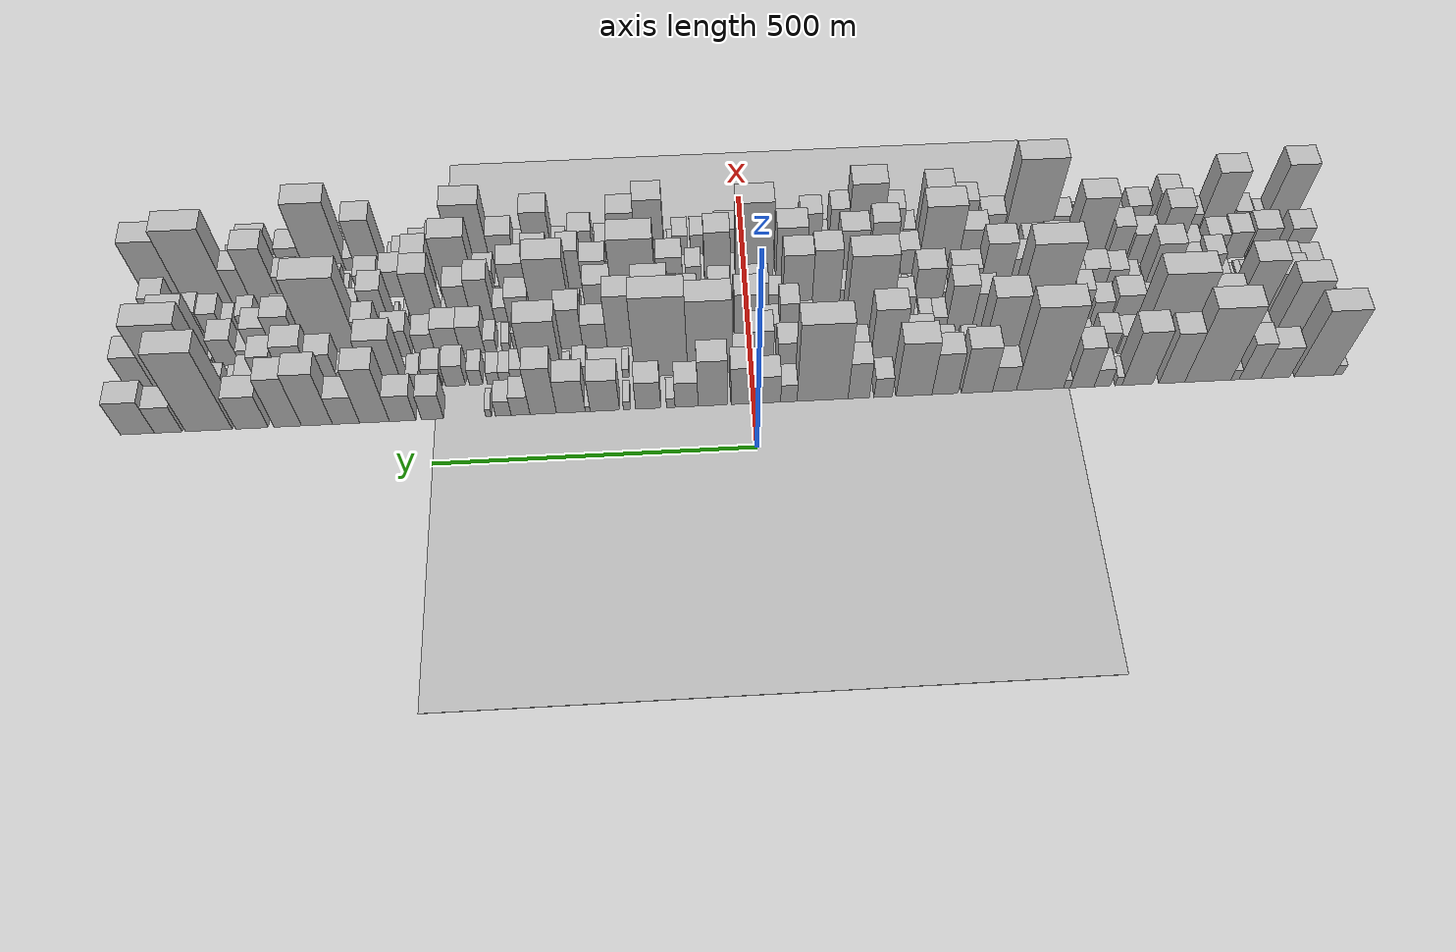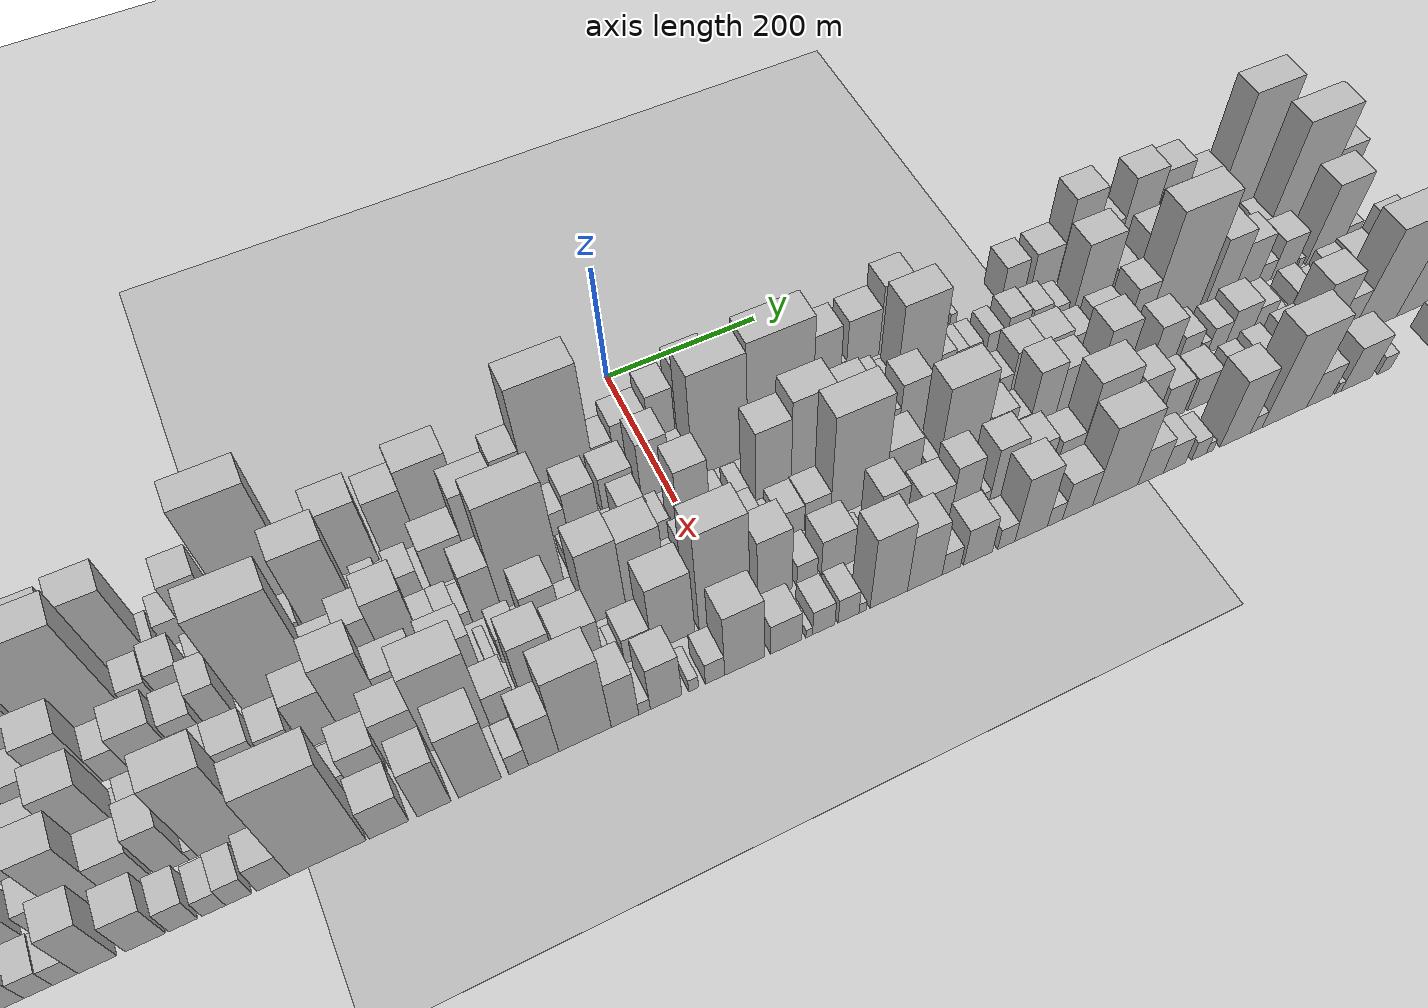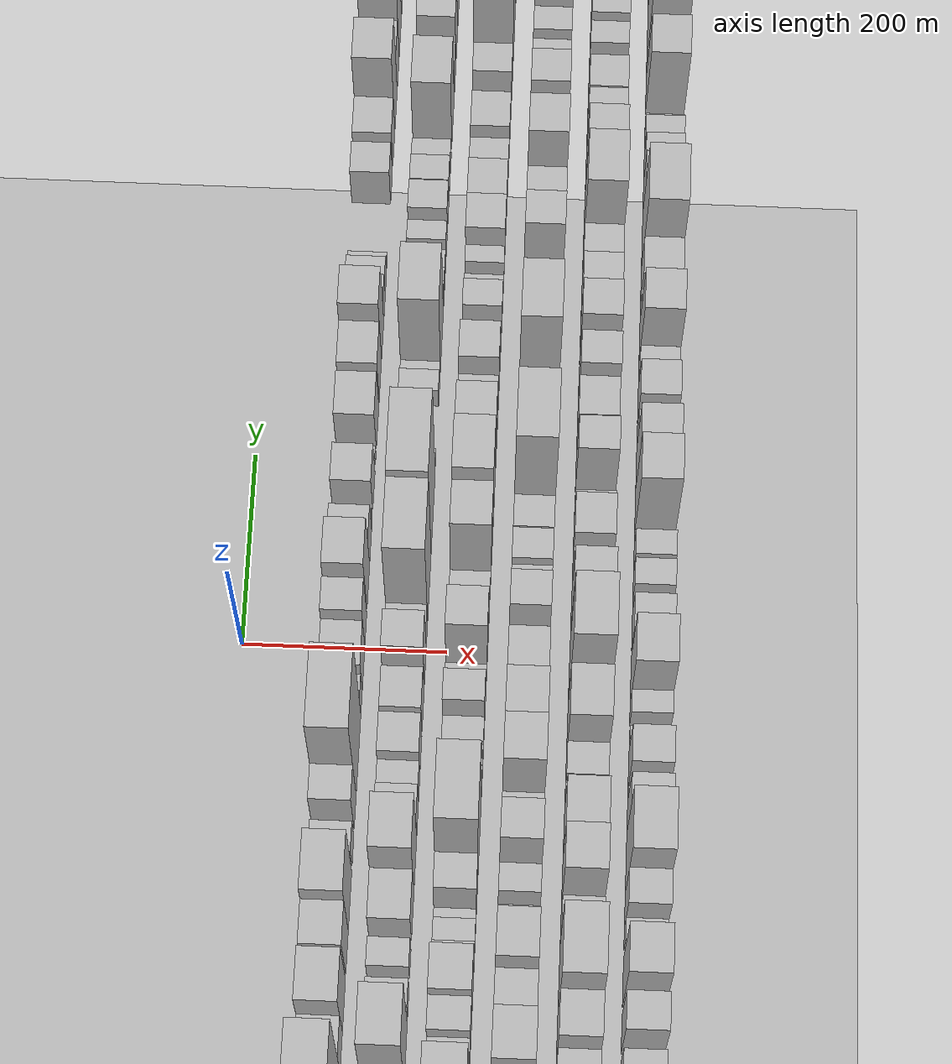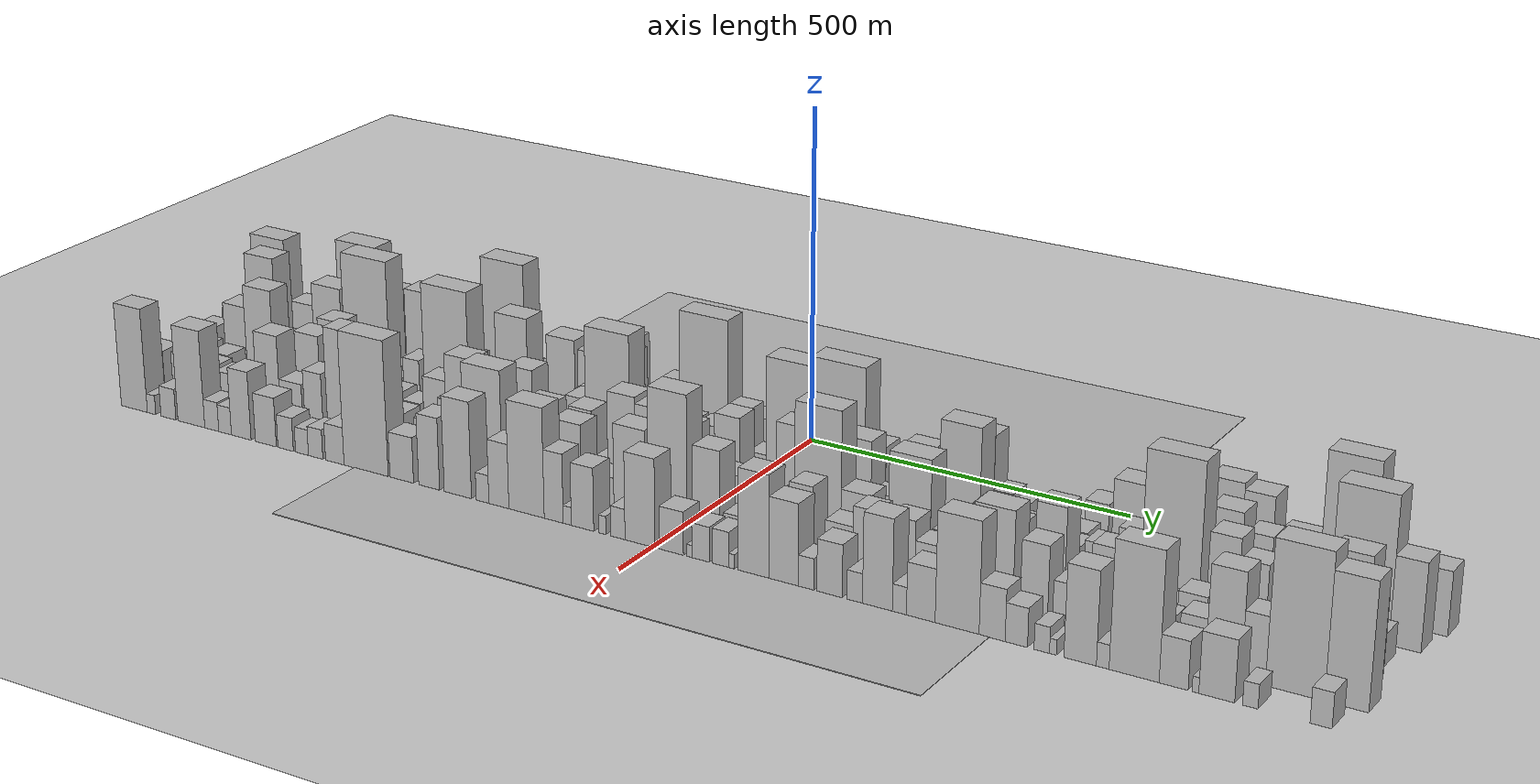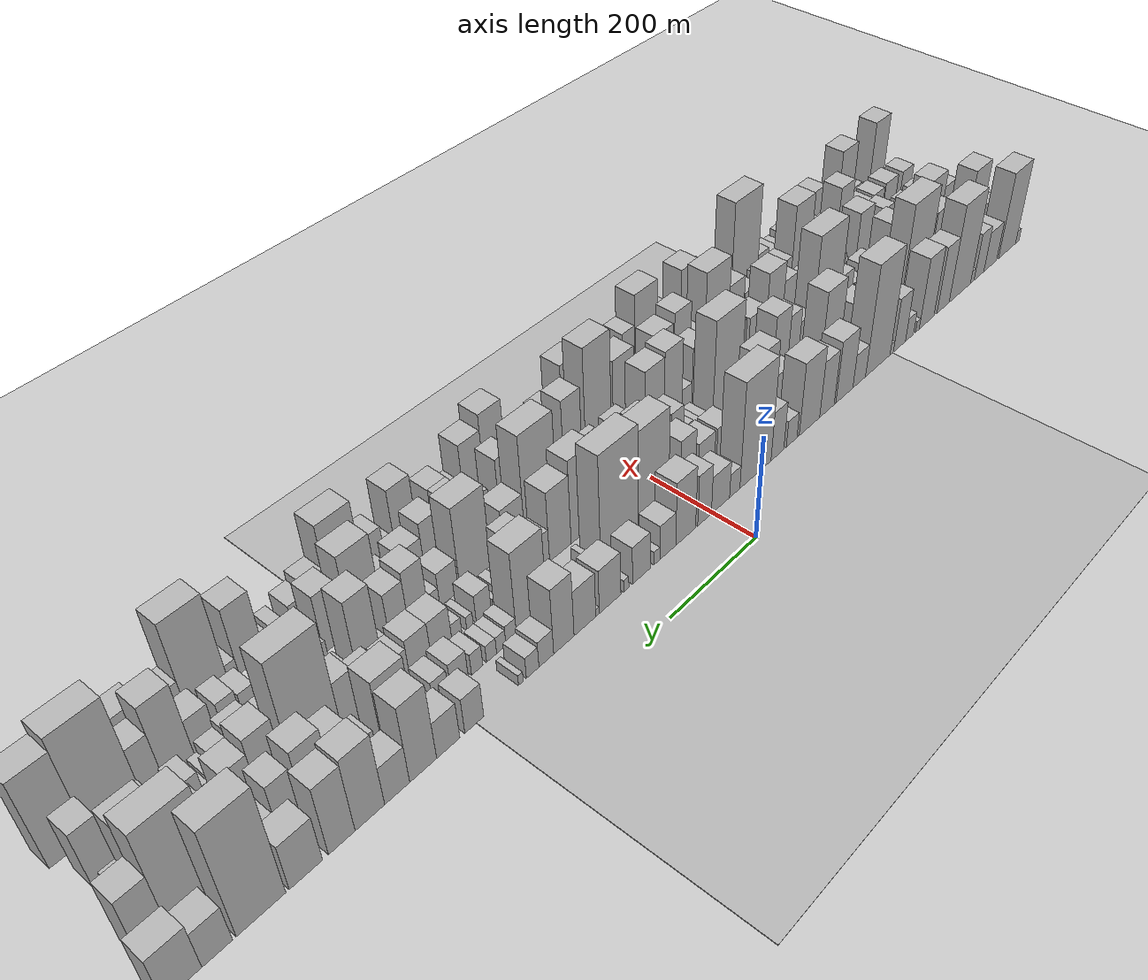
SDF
<?xml version="1.0" encoding="utf-8"?>

<sdf version="1.6">

   <world name="default">

      <gui fullscreen="0">

         <camera name="user_camera">

            <pose>-15 0 4.57585 0 0 0</pose>

            <view_controller>orbit</view_controller>

         </camera>

      </gui>

      <scene>

         <sky>

           <clouds>

             <speed>12</speed>

           </clouds>

         </sky>

         <ambient>0.4 0.4 0.4 1</ambient>

         <background>0.7 0.7 0.7 1</background>

         <shadows>1</shadows>

      </scene>

      <gravity>0 0 -9.8066</gravity>

      <magnetic_field>6e-06 2.3e-05 -4.2e-05</magnetic_field>

      <physics default="0" name="default_physics" type="ode">

         <ode>

            <solver>

               <type>quick</type>

               <iters>10</iters>

               <sor>1.0</sor>

               <use_dynamic_moi_rescaling>0</use_dynamic_moi_rescaling>

            </solver>

            <constraints>

               <cfm>0</cfm>

               <erp>0.2</erp>

               <contact_max_correcting_vel>100</contact_max_correcting_vel>

               <contact_surface_layer>0.001</contact_surface_layer>

            </constraints>

         </ode>

         <max_step_size>0.004</max_step_size>

         <real_time_factor>1</real_time_factor>

         <real_time_update_rate>250</real_time_update_rate>

      </physics>

      <light name="sun" type="directional">

         <cast_shadows>1</cast_shadows>

         <pose>0 0 10 0 0 0</pose>

         <diffuse>0.8 0.8 0.8 1</diffuse>

         <specular>0.2 0.2 0.2 1</specular>

         <attenuation>

            <range>1000</range>

            <constant>0.9</constant>

            <linear>0.01</linear>

            <quadratic>0.001</quadratic>

         </attenuation>

         <direction>-0.5 0.1 -0.9</direction>

      </light>

      <include>

         <name>ground_plane_1</name>

         <uri>model://HANNAS_ground_plane</uri>

         <pose>0 0 0  0 0 0</pose>

      </include>

      <include>

         <name>ground_plane_2</name>

         <uri>model://HANNAS_ground_plane</uri>

         <pose>100 0 0  0 0 0</pose>

      </include>

      <model name="building_1">

         <static>1</static>

         <pose frame="">100.0000 -933.2651 0 0.000000 0.000000 0.000000</pose>

         <link name="link">

            <pose frame="">0 0 13.50 0 0 0</pose>

            <collision name="collision">

               <geometry>

                  <box>

                     <size>40.0000 13.4698 27.0000</size>

                  </box>

               </geometry>

               <max_contacts>10</max_contacts>

               <surface>

                  <contact>

                     <ode/>

                  </contact>

                  <bounce/>

                  <friction>

                     <torsional>

                        <ode/>

                     </torsional>

                     <ode/>

                  </friction>

               </surface>

            </collision>

            <visual name="visual">

               <cast_shadows>0</cast_shadows>

               <geometry>

                  <box>

                     <size>40.0000 13.4698 27.0000</size>

                  </box>

               </geometry>

               <material>

                  <script>

                     <uri>model://HANNAS_wall/materials/scripts</uri>

                     <uri>model://HANNAS_wall/materials/textures</uri>

                     <name>vrc/HANNAS_wall</name>

                  </script>

               </material>

            </visual>

            <self_collide>0</self_collide>

            <enable_wind>0</enable_wind>

            <kinematic>0</kinematic>

         </link>

      </model>

      <model name="building_2">

         <static>1</static>

         <pose frame="">100.0000 -894.2700 0 0.000000 0.000000 0.000000</pose>

         <link name="link">

            <pose frame="">0 0 90.00 0 0 0</pose>

            <collision name="collision">

               <geometry>

                  <box>

                     <size>40.0000 64.5203 180.0000</size>

                  </box>

               </geometry>

               <max_contacts>10</max_contacts>

               <surface>

                  <contact>

                     <ode/>

                  </contact>

                  <bounce/>

                  <friction>

                     <torsional>

                        <ode/>

                     </torsional>

                     <ode/>

                  </friction>

               </surface>

            </collision>

            <visual name="visual">

               <cast_shadows>0</cast_shadows>

               <geometry>

                  <box>

                     <size>40.0000 64.5203 180.0000</size>

                  </box>

               </geometry>

               <material>

                  <script>

                     <uri>model://HANNAS_wall/materials/scripts</uri>

                     <uri>model://HANNAS_wall/materials/textures</uri>

                     <name>vrc/HANNAS_wall</name>

                  </script>

               </material>

            </visual>

            <self_collide>0</self_collide>

            <enable_wind>0</enable_wind>

            <kinematic>0</kinematic>

         </link>

      </model>

      <model name="building_3">

         <static>1</static>

         <pose frame="">100.0000 -831.5772 0 0.000000 0.000000 0.000000</pose>

         <link name="link">

            <pose frame="">0 0 42.00 0 0 0</pose>

            <collision name="collision">

               <geometry>

                  <box>

                     <size>40.0000 46.8655 84.0000</size>

                  </box>

               </geometry>

               <max_contacts>10</max_contacts>

               <surface>

                  <contact>

                     <ode/>

                  </contact>

                  <bounce/>

                  <friction>

                     <torsional>

                        <ode/>

                     </torsional>

                     <ode/>

                  </friction>

               </surface>

            </collision>

            <visual name="visual">

               <cast_shadows>0</cast_shadows>

               <geometry>

                  <box>

                     <size>40.0000 46.8655 84.0000</size>

                  </box>

               </geometry>

               <material>

                  <script>

                     <uri>model://HANNAS_wall/materials/scripts</uri>

                     <uri>model://HANNAS_wall/materials/textures</uri>

                     <name>vrc/HANNAS_wall</name>

                  </script>

               </material>

            </visual>

            <self_collide>0</self_collide>

            <enable_wind>0</enable_wind>

            <kinematic>0</kinematic>

         </link>

      </model>

      <model name="building_4">

         <static>1</static>

         <pose frame="">100.0000 -790.6381 0 0.000000 0.000000 0.000000</pose>

         <link name="link">

            <pose frame="">0 0 49.50 0 0 0</pose>

            <collision name="collision">

               <geometry>

                  <box>

                     <size>40.0000 35.0127 99.0000</size>

                  </box>

               </geometry>

               <max_contacts>10</max_contacts>

               <surface>

                  <contact>

                     <ode/>

                  </contact>

                  <bounce/>

                  <friction>

                     <torsional>

                        <ode/>

                     </torsional>

                     <ode/>

                  </friction>

               </surface>

            </collision>

            <visual name="visual">

               <cast_shadows>0</cast_shadows>

               <geometry>

                  <box>

                     <size>40.0000 35.0127 99.0000</size>

                  </box>

               </geometry>

               <material>

                  <script>

                     <uri>model://HANNAS_wall/materials/scripts</uri>

                     <uri>model://HANNAS_wall/materials/textures</uri>

                     <name>vrc/HANNAS_wall</name>

                  </script>

               </material>

            </visual>

            <self_collide>0</self_collide>

            <enable_wind>0</enable_wind>

            <kinematic>0</kinematic>

         </link>

      </model>

      <model name="building_5">

         <static>1</static>

         <pose frame="">100.0000 -766.5881 0 0.000000 0.000000 0.000000</pose>

         <link name="link">

            <pose frame="">0 0 13.50 0 0 0</pose>

            <collision name="collision">

               <geometry>

                  <box>

                     <size>40.0000 13.0871 27.0000</size>

                  </box>

               </geometry>

               <max_contacts>10</max_contacts>

               <surface>

                  <contact>

                     <ode/>

                  </contact>

                  <bounce/>

                  <friction>

                     <torsional>

                        <ode/>

                     </torsional>

                     <ode/>

                  </friction>

               </surface>

            </collision>

            <visual name="visual">

               <cast_shadows>0</cast_shadows>

               <geometry>

                  <box>

                     <size>40.0000 13.0871 27.0000</size>

                  </box>

               </geometry>

               <material>

                  <script>

                     <uri>model://HANNAS_wall/materials/scripts</uri>

                     <uri>model://HANNAS_wall/materials/textures</uri>

                     <name>vrc/HANNAS_wall</name>

                  </script>

               </material>

            </visual>

            <self_collide>0</self_collide>

            <enable_wind>0</enable_wind>

            <kinematic>0</kinematic>

         </link>

      </model>

      <model name="building_6">

         <static>1</static>

         <pose frame="">100.0000 -722.7656 0 0.000000 0.000000 0.000000</pose>

         <link name="link">

            <pose frame="">0 0 100.50 0 0 0</pose>

            <collision name="collision">

               <geometry>

                  <box>

                     <size>40.0000 74.5580 201.0000</size>

                  </box>

               </geometry>

               <max_contacts>10</max_contacts>

               <surface>

                  <contact>

                     <ode/>

                  </contact>

                  <bounce/>

                  <friction>

                     <torsional>

                        <ode/>

                     </torsional>

                     <ode/>

                  </friction>

               </surface>

            </collision>

            <visual name="visual">

               <cast_shadows>0</cast_shadows>

               <geometry>

                  <box>

                     <size>40.0000 74.5580 201.0000</size>

                  </box>

               </geometry>

               <material>

                  <script>

                     <uri>model://HANNAS_wall/materials/scripts</uri>

                     <uri>model://HANNAS_wall/materials/textures</uri>

                     <name>vrc/HANNAS_wall</name>

                  </script>

               </material>

            </visual>

            <self_collide>0</self_collide>

            <enable_wind>0</enable_wind>

            <kinematic>0</kinematic>

         </link>

      </model>

      <model name="building_7">

         <static>1</static>

         <pose frame="">100.0000 -664.7580 0 0.000000 0.000000 0.000000</pose>

         <link name="link">

            <pose frame="">0 0 69.00 0 0 0</pose>

            <collision name="collision">

               <geometry>

                  <box>

                     <size>40.0000 41.4571 138.0000</size>

                  </box>

               </geometry>

               <max_contacts>10</max_contacts>

               <surface>

                  <contact>

                     <ode/>

                  </contact>

                  <bounce/>

                  <friction>

                     <torsional>

                        <ode/>

                     </torsional>

                     <ode/>

                  </friction>

               </surface>

            </collision>

            <visual name="visual">

               <cast_shadows>0</cast_shadows>

               <geometry>

                  <box>

                     <size>40.0000 41.4571 138.0000</size>

                  </box>

               </geometry>

               <material>

                  <script>

                     <uri>model://HANNAS_wall/materials/scripts</uri>

                     <uri>model://HANNAS_wall/materials/textures</uri>

                     <name>vrc/HANNAS_wall</name>

                  </script>

               </material>

            </visual>

            <self_collide>0</self_collide>

            <enable_wind>0</enable_wind>

            <kinematic>0</kinematic>

         </link>

      </model>

      <model name="building_8">

         <static>1</static>

         <pose frame="">100.0000 -609.5154 0 0.000000 0.000000 0.000000</pose>

         <link name="link">

            <pose frame="">0 0 73.50 0 0 0</pose>

            <collision name="collision">

               <geometry>

                  <box>

                     <size>40.0000 49.0282 147.0000</size>

                  </box>

               </geometry>

               <max_contacts>10</max_contacts>

               <surface>

                  <contact>

                     <ode/>

                  </contact>

                  <bounce/>

                  <friction>

                     <torsional>

                        <ode/>

                     </torsional>

                     <ode/>

                  </friction>

               </surface>

            </collision>

            <visual name="visual">

               <cast_shadows>0</cast_shadows>

               <geometry>

                  <box>

                     <size>40.0000 49.0282 147.0000</size>

                  </box>

               </geometry>

               <material>

                  <script>

                     <uri>model://HANNAS_wall/materials/scripts</uri>

                     <uri>model://HANNAS_wall/materials/textures</uri>

                     <name>vrc/HANNAS_wall</name>

                  </script>

               </material>

            </visual>

            <self_collide>0</self_collide>

            <enable_wind>0</enable_wind>

            <kinematic>0</kinematic>

         </link>

      </model>

      <model name="building_9">

         <static>1</static>

         <pose frame="">100.0000 -579.2453 0 0.000000 0.000000 0.000000</pose>

         <link name="link">

            <pose frame="">0 0 12.00 0 0 0</pose>

            <collision name="collision">

               <geometry>

                  <box>

                     <size>40.0000 11.5120 24.0000</size>

                  </box>

               </geometry>

               <max_contacts>10</max_contacts>

               <surface>

                  <contact>

                     <ode/>

                  </contact>

                  <bounce/>

                  <friction>

                     <torsional>

                        <ode/>

                     </torsional>

                     <ode/>

                  </friction>

               </surface>

            </collision>

            <visual name="visual">

               <cast_shadows>0</cast_shadows>

               <geometry>

                  <box>

                     <size>40.0000 11.5120 24.0000</size>

                  </box>

               </geometry>

               <material>

                  <script>

                     <uri>model://HANNAS_wall/materials/scripts</uri>

                     <uri>model://HANNAS_wall/materials/textures</uri>

                     <name>vrc/HANNAS_wall</name>

                  </script>

               </material>

            </visual>

            <self_collide>0</self_collide>

            <enable_wind>0</enable_wind>

            <kinematic>0</kinematic>

         </link>

      </model>

      <model name="building_10">

         <static>1</static>

         <pose frame="">100.0000 -553.4120 0 0.000000 0.000000 0.000000</pose>

         <link name="link">

            <pose frame="">0 0 24.00 0 0 0</pose>

            <collision name="collision">

               <geometry>

                  <box>

                     <size>40.0000 26.1545 48.0000</size>

                  </box>

               </geometry>

               <max_contacts>10</max_contacts>

               <surface>

                  <contact>

                     <ode/>

                  </contact>

                  <bounce/>

                  <friction>

                     <torsional>

                        <ode/>

                     </torsional>

                     <ode/>

                  </friction>

               </surface>

            </collision>

            <visual name="visual">

               <cast_shadows>0</cast_shadows>

               <geometry>

                  <box>

                     <size>40.0000 26.1545 48.0000</size>

                  </box>

               </geometry>

               <material>

                  <script>

                     <uri>model://HANNAS_wall/materials/scripts</uri>

                     <uri>model://HANNAS_wall/materials/textures</uri>

                     <name>vrc/HANNAS_wall</name>

                  </script>

               </material>

            </visual>

            <self_collide>0</self_collide>

            <enable_wind>0</enable_wind>

            <kinematic>0</kinematic>

         </link>

      </model>

      <model name="building_11">

         <static>1</static>

         <pose frame="">100.0000 -521.2546 0 0.000000 0.000000 0.000000</pose>

         <link name="link">

            <pose frame="">0 0 55.50 0 0 0</pose>

            <collision name="collision">

               <geometry>

                  <box>

                     <size>40.0000 38.1603 111.0000</size>

                  </box>

               </geometry>

               <max_contacts>10</max_contacts>

               <surface>

                  <contact>

                     <ode/>

                  </contact>

                  <bounce/>

                  <friction>

                     <torsional>

                        <ode/>

                     </torsional>

                     <ode/>

                  </friction>

               </surface>

            </collision>

            <visual name="visual">

               <cast_shadows>0</cast_shadows>

               <geometry>

                  <box>

                     <size>40.0000 38.1603 111.0000</size>

                  </box>

               </geometry>

               <material>

                  <script>

                     <uri>model://HANNAS_wall/materials/scripts</uri>

                     <uri>model://HANNAS_wall/materials/textures</uri>

                     <name>vrc/HANNAS_wall</name>

                  </script>

               </material>

            </visual>

            <self_collide>0</self_collide>

            <enable_wind>0</enable_wind>

            <kinematic>0</kinematic>

         </link>

      </model>

      <model name="building_12">

         <static>1</static>

         <pose frame="">100.0000 -496.7735 0 0.000000 0.000000 0.000000</pose>

         <link name="link">

            <pose frame="">0 0 12.00 0 0 0</pose>

            <collision name="collision">

               <geometry>

                  <box>

                     <size>40.0000 10.8020 24.0000</size>

                  </box>

               </geometry>

               <max_contacts>10</max_contacts>

               <surface>

                  <contact>

                     <ode/>

                  </contact>

                  <bounce/>

                  <friction>

                     <torsional>

                        <ode/>

                     </torsional>

                     <ode/>

                  </friction>

               </surface>

            </collision>

            <visual name="visual">

               <cast_shadows>0</cast_shadows>

               <geometry>

                  <box>

                     <size>40.0000 10.8020 24.0000</size>

                  </box>

               </geometry>

               <material>

                  <script>

                     <uri>model://HANNAS_wall/materials/scripts</uri>

                     <uri>model://HANNAS_wall/materials/textures</uri>

                     <name>vrc/HANNAS_wall</name>

                  </script>

               </material>

            </visual>

            <self_collide>0</self_collide>

            <enable_wind>0</enable_wind>

            <kinematic>0</kinematic>

         </link>

      </model>

      <model name="building_13">

         <static>1</static>

         <pose frame="">100.0000 -453.5605 0 0.000000 0.000000 0.000000</pose>

         <link name="link">

            <pose frame="">0 0 112.50 0 0 0</pose>

            <collision name="collision">

               <geometry>

                  <box>

                     <size>40.0000 75.6241 225.0000</size>

                  </box>

               </geometry>

               <max_contacts>10</max_contacts>

               <surface>

                  <contact>

                     <ode/>

                  </contact>

                  <bounce/>

                  <friction>

                     <torsional>

                        <ode/>

                     </torsional>

                     <ode/>

                  </friction>

               </surface>

            </collision>

            <visual name="visual">

               <cast_shadows>0</cast_shadows>

               <geometry>

                  <box>

                     <size>40.0000 75.6241 225.0000</size>

                  </box>

               </geometry>

               <material>

                  <script>

                     <uri>model://HANNAS_wall/materials/scripts</uri>

                     <uri>model://HANNAS_wall/materials/textures</uri>

                     <name>vrc/HANNAS_wall</name>

                  </script>

               </material>

            </visual>

            <self_collide>0</self_collide>

            <enable_wind>0</enable_wind>

            <kinematic>0</kinematic>

         </link>

      </model>

      <model name="building_14">

         <static>1</static>

         <pose frame="">100.0000 -396.7264 0 0.000000 0.000000 0.000000</pose>

         <link name="link">

            <pose frame="">0 0 34.50 0 0 0</pose>

            <collision name="collision">

               <geometry>

                  <box>

                     <size>40.0000 38.0440 69.0000</size>

                  </box>

               </geometry>

               <max_contacts>10</max_contacts>

               <surface>

                  <contact>

                     <ode/>

                  </contact>

                  <bounce/>

                  <friction>

                     <torsional>

                        <ode/>

                     </torsional>

                     <ode/>

                  </friction>

               </surface>

            </collision>

            <visual name="visual">

               <cast_shadows>0</cast_shadows>

               <geometry>

                  <box>

                     <size>40.0000 38.0440 69.0000</size>

                  </box>

               </geometry>

               <material>

                  <script>

                     <uri>model://HANNAS_wall/materials/scripts</uri>

                     <uri>model://HANNAS_wall/materials/textures</uri>

                     <name>vrc/HANNAS_wall</name>

                  </script>

               </material>

            </visual>

            <self_collide>0</self_collide>

            <enable_wind>0</enable_wind>

            <kinematic>0</kinematic>

         </link>

      </model>

      <model name="building_15">

         <static>1</static>

         <pose frame="">100.0000 -352.8798 0 0.000000 0.000000 0.000000</pose>

         <link name="link">

            <pose frame="">0 0 63.00 0 0 0</pose>

            <collision name="collision">

               <geometry>

                  <box>

                     <size>40.0000 49.6493 126.0000</size>

                  </box>

               </geometry>

               <max_contacts>10</max_contacts>

               <surface>

                  <contact>

                     <ode/>

                  </contact>

                  <bounce/>

                  <friction>

                     <torsional>

                        <ode/>

                     </torsional>

                     <ode/>

                  </friction>

               </surface>

            </collision>

            <visual name="visual">

               <cast_shadows>0</cast_shadows>

               <geometry>

                  <box>

                     <size>40.0000 49.6493 126.0000</size>

                  </box>

               </geometry>

               <material>

                  <script>

                     <uri>model://HANNAS_wall/materials/scripts</uri>

                     <uri>model://HANNAS_wall/materials/textures</uri>

                     <name>vrc/HANNAS_wall</name>

                  </script>

               </material>

            </visual>

            <self_collide>0</self_collide>

            <enable_wind>0</enable_wind>

            <kinematic>0</kinematic>

         </link>

      </model>

      <model name="building_16">

         <static>1</static>

         <pose frame="">100.0000 -302.2776 0 0.000000 0.000000 0.000000</pose>

         <link name="link">

            <pose frame="">0 0 57.00 0 0 0</pose>

            <collision name="collision">

               <geometry>

                  <box>

                     <size>40.0000 41.5552 114.0000</size>

                  </box>

               </geometry>

               <max_contacts>10</max_contacts>

               <surface>

                  <contact>

                     <ode/>

                  </contact>

                  <bounce/>

                  <friction>

                     <torsional>

                        <ode/>

                     </torsional>

                     <ode/>

                  </friction>

               </surface>

            </collision>

            <visual name="visual">

               <cast_shadows>0</cast_shadows>

               <geometry>

                  <box>

                     <size>40.0000 41.5552 114.0000</size>

                  </box>

               </geometry>

               <material>

                  <script>

                     <uri>model://HANNAS_wall/materials/scripts</uri>

                     <uri>model://HANNAS_wall/materials/textures</uri>

                     <name>vrc/HANNAS_wall</name>

                  </script>

               </material>

            </visual>

            <self_collide>0</self_collide>

            <enable_wind>0</enable_wind>

            <kinematic>0</kinematic>

         </link>

      </model>

      <model name="building_17">

         <static>1</static>

         <pose frame="">100.0000 -252.9097 0 0.000000 0.000000 0.000000</pose>

         <link name="link">

            <pose frame="">0 0 73.50 0 0 0</pose>

            <collision name="collision">

               <geometry>

                  <box>

                     <size>40.0000 57.1807 147.0000</size>

                  </box>

               </geometry>

               <max_contacts>10</max_contacts>

               <surface>

                  <contact>

                     <ode/>

                  </contact>

                  <bounce/>

                  <friction>

                     <torsional>

                        <ode/>

                     </torsional>

                     <ode/>

                  </friction>

               </surface>

            </collision>

            <visual name="visual">

               <cast_shadows>0</cast_shadows>

               <geometry>

                  <box>

                     <size>40.0000 57.1807 147.0000</size>

                  </box>

               </geometry>

               <material>

                  <script>

                     <uri>model://HANNAS_wall/materials/scripts</uri>

                     <uri>model://HANNAS_wall/materials/textures</uri>

                     <name>vrc/HANNAS_wall</name>

                  </script>

               </material>

            </visual>

            <self_collide>0</self_collide>

            <enable_wind>0</enable_wind>

            <kinematic>0</kinematic>

         </link>

      </model>

      <model name="building_18">

         <static>1</static>

         <pose frame="">100.0000 -203.7958 0 0.000000 0.000000 0.000000</pose>

         <link name="link">

            <pose frame="">0 0 27.00 0 0 0</pose>

            <collision name="collision">

               <geometry>

                  <box>

                     <size>40.0000 29.0470 54.0000</size>

                  </box>

               </geometry>

               <max_contacts>10</max_contacts>

               <surface>

                  <contact>

                     <ode/>

                  </contact>

                  <bounce/>

                  <friction>

                     <torsional>

                        <ode/>

                     </torsional>

                     <ode/>

                  </friction>

               </surface>

            </collision>

            <visual name="visual">

               <cast_shadows>0</cast_shadows>

               <geometry>

                  <box>

                     <size>40.0000 29.0470 54.0000</size>

                  </box>

               </geometry>

               <material>

                  <script>

                     <uri>model://HANNAS_wall/materials/scripts</uri>

                     <uri>model://HANNAS_wall/materials/textures</uri>

                     <name>vrc/HANNAS_wall</name>

                  </script>

               </material>

            </visual>

            <self_collide>0</self_collide>

            <enable_wind>0</enable_wind>

            <kinematic>0</kinematic>

         </link>

      </model>

      <model name="building_19">

         <static>1</static>

         <pose frame="">100.0000 -165.2593 0 0.000000 0.000000 0.000000</pose>

         <link name="link">

            <pose frame="">0 0 49.50 0 0 0</pose>

            <collision name="collision">

               <geometry>

                  <box>

                     <size>40.0000 34.0261 99.0000</size>

                  </box>

               </geometry>

               <max_contacts>10</max_contacts>

               <surface>

                  <contact>

                     <ode/>

                  </contact>

                  <bounce/>

                  <friction>

                     <torsional>

                        <ode/>

                     </torsional>

                     <ode/>

                  </friction>

               </surface>

            </collision>

            <visual name="visual">

               <cast_shadows>0</cast_shadows>

               <geometry>

                  <box>

                     <size>40.0000 34.0261 99.0000</size>

                  </box>

               </geometry>

               <material>

                  <script>

                     <uri>model://HANNAS_wall/materials/scripts</uri>

                     <uri>model://HANNAS_wall/materials/textures</uri>

                     <name>vrc/HANNAS_wall</name>

                  </script>

               </material>

            </visual>

            <self_collide>0</self_collide>

            <enable_wind>0</enable_wind>

            <kinematic>0</kinematic>

         </link>

      </model>

      <model name="building_20">

         <static>1</static>

         <pose frame="">100.0000 -107.9340 0 0.000000 0.000000 0.000000</pose>

         <link name="link">

            <pose frame="">0 0 105.00 0 0 0</pose>

            <collision name="collision">

               <geometry>

                  <box>

                     <size>40.0000 80.6244 210.0000</size>

                  </box>

               </geometry>

               <max_contacts>10</max_contacts>

               <surface>

                  <contact>

                     <ode/>

                  </contact>

                  <bounce/>

                  <friction>

                     <torsional>

                        <ode/>

                     </torsional>

                     <ode/>

                  </friction>

               </surface>

            </collision>

            <visual name="visual">

               <cast_shadows>0</cast_shadows>

               <geometry>

                  <box>

                     <size>40.0000 80.6244 210.0000</size>

                  </box>

               </geometry>

               <material>

                  <script>

                     <uri>model://HANNAS_wall/materials/scripts</uri>

                     <uri>model://HANNAS_wall/materials/textures</uri>

                     <name>vrc/HANNAS_wall</name>

                  </script>

               </material>

            </visual>

            <self_collide>0</self_collide>

            <enable_wind>0</enable_wind>

            <kinematic>0</kinematic>

         </link>

      </model>

      <model name="building_21">

         <static>1</static>

         <pose frame="">100.0000 -54.6295 0 0.000000 0.000000 0.000000</pose>

         <link name="link">

            <pose frame="">0 0 24.00 0 0 0</pose>

            <collision name="collision">

               <geometry>

                  <box>

                     <size>40.0000 25.9846 48.0000</size>

                  </box>

               </geometry>

               <max_contacts>10</max_contacts>

               <surface>

                  <contact>

                     <ode/>

                  </contact>

                  <bounce/>

                  <friction>

                     <torsional>

                        <ode/>

                     </torsional>

                     <ode/>

                  </friction>

               </surface>

            </collision>

            <visual name="visual">

               <cast_shadows>0</cast_shadows>

               <geometry>

                  <box>

                     <size>40.0000 25.9846 48.0000</size>

                  </box>

               </geometry>

               <material>

                  <script>

                     <uri>model://HANNAS_wall/materials/scripts</uri>

                     <uri>model://HANNAS_wall/materials/textures</uri>

                     <name>vrc/HANNAS_wall</name>

                  </script>

               </material>

            </visual>

            <self_collide>0</self_collide>

            <enable_wind>0</enable_wind>

            <kinematic>0</kinematic>

         </link>

      </model>

      <model name="building_22">

         <static>1</static>

         <pose frame="">100.0000 -19.1521 0 0.000000 0.000000 0.000000</pose>

         <link name="link">

            <pose frame="">0 0 37.50 0 0 0</pose>

            <collision name="collision">

               <geometry>

                  <box>

                     <size>40.0000 44.9702 75.0000</size>

                  </box>

               </geometry>

               <max_contacts>10</max_contacts>

               <surface>

                  <contact>

                     <ode/>

                  </contact>

                  <bounce/>

                  <friction>

                     <torsional>

                        <ode/>

                     </torsional>

                     <ode/>

                  </friction>

               </surface>

            </collision>

            <visual name="visual">

               <cast_shadows>0</cast_shadows>

               <geometry>

                  <box>

                     <size>40.0000 44.9702 75.0000</size>

                  </box>

               </geometry>

               <material>

                  <script>

                     <uri>model://HANNAS_wall/materials/scripts</uri>

                     <uri>model://HANNAS_wall/materials/textures</uri>

                     <name>vrc/HANNAS_wall</name>

                  </script>

               </material>

            </visual>

            <self_collide>0</self_collide>

            <enable_wind>0</enable_wind>

            <kinematic>0</kinematic>

         </link>

      </model>

      <model name="building_23">

         <static>1</static>

         <pose frame="">100.0000 19.9262 0 0.000000 0.000000 0.000000</pose>

         <link name="link">

            <pose frame="">0 0 51.00 0 0 0</pose>

            <collision name="collision">

               <geometry>

                  <box>

                     <size>40.0000 33.1864 102.0000</size>

                  </box>

               </geometry>

               <max_contacts>10</max_contacts>

               <surface>

                  <contact>

                     <ode/>

                  </contact>

                  <bounce/>

                  <friction>

                     <torsional>

                        <ode/>

                     </torsional>

                     <ode/>

                  </friction>

               </surface>

            </collision>

            <visual name="visual">

               <cast_shadows>0</cast_shadows>

               <geometry>

                  <box>

                     <size>40.0000 33.1864 102.0000</size>

                  </box>

               </geometry>

               <material>

                  <script>

                     <uri>model://HANNAS_wall/materials/scripts</uri>

                     <uri>model://HANNAS_wall/materials/textures</uri>

                     <name>vrc/HANNAS_wall</name>

                  </script>

               </material>

            </visual>

            <self_collide>0</self_collide>

            <enable_wind>0</enable_wind>

            <kinematic>0</kinematic>

         </link>

      </model>

      <model name="building_24">

         <static>1</static>

         <pose frame="">100.0000 64.9533 0 0.000000 0.000000 0.000000</pose>

         <link name="link">

            <pose frame="">0 0 63.00 0 0 0</pose>

            <collision name="collision">

               <geometry>

                  <box>

                     <size>40.0000 46.8679 126.0000</size>

                  </box>

               </geometry>

               <max_contacts>10</max_contacts>

               <surface>

                  <contact>

                     <ode/>

                  </contact>

                  <bounce/>

                  <friction>

                     <torsional>

                        <ode/>

                     </torsional>

                     <ode/>

                  </friction>

               </surface>

            </collision>

            <visual name="visual">

               <cast_shadows>0</cast_shadows>

               <geometry>

                  <box>

                     <size>40.0000 46.8679 126.0000</size>

                  </box>

               </geometry>

               <material>

                  <script>

                     <uri>model://HANNAS_wall/materials/scripts</uri>

                     <uri>model://HANNAS_wall/materials/textures</uri>

                     <name>vrc/HANNAS_wall</name>

                  </script>

               </material>

            </visual>

            <self_collide>0</self_collide>

            <enable_wind>0</enable_wind>

            <kinematic>0</kinematic>

         </link>

      </model>

      <model name="building_25">

         <static>1</static>

         <pose frame="">100.0000 106.5144 0 0.000000 0.000000 0.000000</pose>

         <link name="link">

            <pose frame="">0 0 34.50 0 0 0</pose>

            <collision name="collision">

               <geometry>

                  <box>

                     <size>40.0000 36.2544 69.0000</size>

                  </box>

               </geometry>

               <max_contacts>10</max_contacts>

               <surface>

                  <contact>

                     <ode/>

                  </contact>

                  <bounce/>

                  <friction>

                     <torsional>

                        <ode/>

                     </torsional>

                     <ode/>

                  </friction>

               </surface>

            </collision>

            <visual name="visual">

               <cast_shadows>0</cast_shadows>

               <geometry>

                  <box>

                     <size>40.0000 36.2544 69.0000</size>

                  </box>

               </geometry>

               <material>

                  <script>

                     <uri>model://HANNAS_wall/materials/scripts</uri>

                     <uri>model://HANNAS_wall/materials/textures</uri>

                     <name>vrc/HANNAS_wall</name>

                  </script>

               </material>

            </visual>

            <self_collide>0</self_collide>

            <enable_wind>0</enable_wind>

            <kinematic>0</kinematic>

         </link>

      </model>

      <model name="building_26">

         <static>1</static>

         <pose frame="">100.0000 131.3429 0 0.000000 0.000000 0.000000</pose>

         <link name="link">

            <pose frame="">0 0 13.50 0 0 0</pose>

            <collision name="collision">

               <geometry>

                  <box>

                     <size>40.0000 13.4026 27.0000</size>

                  </box>

               </geometry>

               <max_contacts>10</max_contacts>

               <surface>

                  <contact>

                     <ode/>

                  </contact>

                  <bounce/>

                  <friction>

                     <torsional>

                        <ode/>

                     </torsional>

                     <ode/>

                  </friction>

               </surface>

            </collision>

            <visual name="visual">

               <cast_shadows>0</cast_shadows>

               <geometry>

                  <box>

                     <size>40.0000 13.4026 27.0000</size>

                  </box>

               </geometry>

               <material>

                  <script>

                     <uri>model://HANNAS_wall/materials/scripts</uri>

                     <uri>model://HANNAS_wall/materials/textures</uri>

                     <name>vrc/HANNAS_wall</name>

                  </script>

               </material>

            </visual>

            <self_collide>0</self_collide>

            <enable_wind>0</enable_wind>

            <kinematic>0</kinematic>

         </link>

      </model>

      <model name="building_27">

         <static>1</static>

         <pose frame="">100.0000 166.7465 0 0.000000 0.000000 0.000000</pose>

         <link name="link">

            <pose frame="">0 0 37.50 0 0 0</pose>

            <collision name="collision">

               <geometry>

                  <box>

                     <size>40.0000 39.4046 75.0000</size>

                  </box>

               </geometry>

               <max_contacts>10</max_contacts>

               <surface>

                  <contact>

                     <ode/>

                  </contact>

                  <bounce/>

                  <friction>

                     <torsional>

                        <ode/>

                     </torsional>

                     <ode/>

                  </friction>

               </surface>

            </collision>

            <visual name="visual">

               <cast_shadows>0</cast_shadows>

               <geometry>

                  <box>

                     <size>40.0000 39.4046 75.0000</size>

                  </box>

               </geometry>

               <material>

                  <script>

                     <uri>model://HANNAS_wall/materials/scripts</uri>

                     <uri>model://HANNAS_wall/materials/textures</uri>

                     <name>vrc/HANNAS_wall</name>

                  </script>

               </material>

            </visual>

            <self_collide>0</self_collide>

            <enable_wind>0</enable_wind>

            <kinematic>0</kinematic>

         </link>

      </model>

      <model name="building_28">

         <static>1</static>

         <pose frame="">100.0000 200.1653 0 0.000000 0.000000 0.000000</pose>

         <link name="link">

            <pose frame="">0 0 12.00 0 0 0</pose>

            <collision name="collision">

               <geometry>

                  <box>

                     <size>40.0000 11.4329 24.0000</size>

                  </box>

               </geometry>

               <max_contacts>10</max_contacts>

               <surface>

                  <contact>

                     <ode/>

                  </contact>

                  <bounce/>

                  <friction>

                     <torsional>

                        <ode/>

                     </torsional>

                     <ode/>

                  </friction>

               </surface>

            </collision>

            <visual name="visual">

               <cast_shadows>0</cast_shadows>

               <geometry>

                  <box>

                     <size>40.0000 11.4329 24.0000</size>

                  </box>

               </geometry>

               <material>

                  <script>

                     <uri>model://HANNAS_wall/materials/scripts</uri>

                     <uri>model://HANNAS_wall/materials/textures</uri>

                     <name>vrc/HANNAS_wall</name>

                  </script>

               </material>

            </visual>

            <self_collide>0</self_collide>

            <enable_wind>0</enable_wind>

            <kinematic>0</kinematic>

         </link>

      </model>

      <model name="building_29">

         <static>1</static>

         <pose frame="">100.0000 234.9728 0 0.000000 0.000000 0.000000</pose>

         <link name="link">

            <pose frame="">0 0 43.50 0 0 0</pose>

            <collision name="collision">

               <geometry>

                  <box>

                     <size>40.0000 46.1821 87.0000</size>

                  </box>

               </geometry>

               <max_contacts>10</max_contacts>

               <surface>

                  <contact>

                     <ode/>

                  </contact>

                  <bounce/>

                  <friction>

                     <torsional>

                        <ode/>

                     </torsional>

                     <ode/>

                  </friction>

               </surface>

            </collision>

            <visual name="visual">

               <cast_shadows>0</cast_shadows>

               <geometry>

                  <box>

                     <size>40.0000 46.1821 87.0000</size>

                  </box>

               </geometry>

               <material>

                  <script>

                     <uri>model://HANNAS_wall/materials/scripts</uri>

                     <uri>model://HANNAS_wall/materials/textures</uri>

                     <name>vrc/HANNAS_wall</name>

                  </script>

               </material>

            </visual>

            <self_collide>0</self_collide>

            <enable_wind>0</enable_wind>

            <kinematic>0</kinematic>

         </link>

      </model>

      <model name="building_30">

         <static>1</static>

         <pose frame="">100.0000 261.7786 0 0.000000 0.000000 0.000000</pose>

         <link name="link">

            <pose frame="">0 0 7.50 0 0 0</pose>

            <collision name="collision">

               <geometry>

                  <box>

                     <size>40.0000 7.4294 15.0000</size>

                  </box>

               </geometry>

               <max_contacts>10</max_contacts>

               <surface>

                  <contact>

                     <ode/>

                  </contact>

                  <bounce/>

                  <friction>

                     <torsional>

                        <ode/>

                     </torsional>

                     <ode/>

                  </friction>

               </surface>

            </collision>

            <visual name="visual">

               <cast_shadows>0</cast_shadows>

               <geometry>

                  <box>

                     <size>40.0000 7.4294 15.0000</size>

                  </box>

               </geometry>

               <material>

                  <script>

                     <uri>model://HANNAS_wall/materials/scripts</uri>

                     <uri>model://HANNAS_wall/materials/textures</uri>

                     <name>vrc/HANNAS_wall</name>

                  </script>

               </material>

            </visual>

            <self_collide>0</self_collide>

            <enable_wind>0</enable_wind>

            <kinematic>0</kinematic>

         </link>

      </model>

      <model name="building_31">

         <static>1</static>

         <pose frame="">100.0000 288.1224 0 0.000000 0.000000 0.000000</pose>

         <link name="link">

            <pose frame="">0 0 45.00 0 0 0</pose>

            <collision name="collision">

               <geometry>

                  <box>

                     <size>40.0000 45.2583 90.0000</size>

                  </box>

               </geometry>

               <max_contacts>10</max_contacts>

               <surface>

                  <contact>

                     <ode/>

                  </contact>

                  <bounce/>

                  <friction>

                     <torsional>

                        <ode/>

                     </torsional>

                     <ode/>

                  </friction>

               </surface>

            </collision>

            <visual name="visual">

               <cast_shadows>0</cast_shadows>

               <geometry>

                  <box>

                     <size>40.0000 45.2583 90.0000</size>

                  </box>

               </geometry>

               <material>

                  <script>

                     <uri>model://HANNAS_wall/materials/scripts</uri>

                     <uri>model://HANNAS_wall/materials/textures</uri>

                     <name>vrc/HANNAS_wall</name>

                  </script>

               </material>

            </visual>

            <self_collide>0</self_collide>

            <enable_wind>0</enable_wind>

            <kinematic>0</kinematic>

         </link>

      </model>

      <model name="building_32">

         <static>1</static>

         <pose frame="">100.0000 331.3956 0 0.000000 0.000000 0.000000</pose>

         <link name="link">

            <pose frame="">0 0 64.50 0 0 0</pose>

            <collision name="collision">

               <geometry>

                  <box>

                     <size>40.0000 41.2880 129.0000</size>

                  </box>

               </geometry>

               <max_contacts>10</max_contacts>

               <surface>

                  <contact>

                     <ode/>

                  </contact>

                  <bounce/>

                  <friction>

                     <torsional>

                        <ode/>

                     </torsional>

                     <ode/>

                  </friction>

               </surface>

            </collision>

            <visual name="visual">

               <cast_shadows>0</cast_shadows>

               <geometry>

                  <box>

                     <size>40.0000 41.2880 129.0000</size>

                  </box>

               </geometry>

               <material>

                  <script>

                     <uri>model://HANNAS_wall/materials/scripts</uri>

                     <uri>model://HANNAS_wall/materials/textures</uri>

                     <name>vrc/HANNAS_wall</name>

                  </script>

               </material>

            </visual>

            <self_collide>0</self_collide>

            <enable_wind>0</enable_wind>

            <kinematic>0</kinematic>

         </link>

      </model>

      <model name="building_33">

         <static>1</static>

         <pose frame="">100.0000 366.7102 0 0.000000 0.000000 0.000000</pose>

         <link name="link">

            <pose frame="">0 0 25.50 0 0 0</pose>

            <collision name="collision">

               <geometry>

                  <box>

                     <size>40.0000 29.3411 51.0000</size>

                  </box>

               </geometry>

               <max_contacts>10</max_contacts>

               <surface>

                  <contact>

                     <ode/>

                  </contact>

                  <bounce/>

                  <friction>

                     <torsional>

                        <ode/>

                     </torsional>

                     <ode/>

                  </friction>

               </surface>

            </collision>

            <visual name="visual">

               <cast_shadows>0</cast_shadows>

               <geometry>

                  <box>

                     <size>40.0000 29.3411 51.0000</size>

                  </box>

               </geometry>

               <material>

                  <script>

                     <uri>model://HANNAS_wall/materials/scripts</uri>

                     <uri>model://HANNAS_wall/materials/textures</uri>

                     <name>vrc/HANNAS_wall</name>

                  </script>

               </material>

            </visual>

            <self_collide>0</self_collide>

            <enable_wind>0</enable_wind>

            <kinematic>0</kinematic>

         </link>

      </model>

      <model name="building_34">

         <static>1</static>

         <pose frame="">100.0000 393.6811 0 0.000000 0.000000 0.000000</pose>

         <link name="link">

            <pose frame="">0 0 21.00 0 0 0</pose>

            <collision name="collision">

               <geometry>

                  <box>

                     <size>40.0000 24.6008 42.0000</size>

                  </box>

               </geometry>

               <max_contacts>10</max_contacts>

               <surface>

                  <contact>

                     <ode/>

                  </contact>

                  <bounce/>

                  <friction>

                     <torsional>

                        <ode/>

                     </torsional>

                     <ode/>

                  </friction>

               </surface>

            </collision>

            <visual name="visual">

               <cast_shadows>0</cast_shadows>

               <geometry>

                  <box>

                     <size>40.0000 24.6008 42.0000</size>

                  </box>

               </geometry>

               <material>

                  <script>

                     <uri>model://HANNAS_wall/materials/scripts</uri>

                     <uri>model://HANNAS_wall/materials/textures</uri>

                     <name>vrc/HANNAS_wall</name>

                  </script>

               </material>

            </visual>

            <self_collide>0</self_collide>

            <enable_wind>0</enable_wind>

            <kinematic>0</kinematic>

         </link>

      </model>

      <model name="building_35">

         <static>1</static>

         <pose frame="">100.0000 416.5657 0 0.000000 0.000000 0.000000</pose>

         <link name="link">

            <pose frame="">0 0 10.50 0 0 0</pose>

            <collision name="collision">

               <geometry>

                  <box>

                     <size>40.0000 9.1682 21.0000</size>

                  </box>

               </geometry>

               <max_contacts>10</max_contacts>

               <surface>

                  <contact>

                     <ode/>

                  </contact>

                  <bounce/>

                  <friction>

                     <torsional>

                        <ode/>

                     </torsional>

                     <ode/>

                  </friction>

               </surface>

            </collision>

            <visual name="visual">

               <cast_shadows>0</cast_shadows>

               <geometry>

                  <box>

                     <size>40.0000 9.1682 21.0000</size>

                  </box>

               </geometry>

               <material>

                  <script>

                     <uri>model://HANNAS_wall/materials/scripts</uri>

                     <uri>model://HANNAS_wall/materials/textures</uri>

                     <name>vrc/HANNAS_wall</name>

                  </script>

               </material>

            </visual>

            <self_collide>0</self_collide>

            <enable_wind>0</enable_wind>

            <kinematic>0</kinematic>

         </link>

      </model>

      <model name="building_36">

         <static>1</static>

         <pose frame="">100.0000 503.9159 0 0.000000 0.000000 0.000000</pose>

         <link name="link">

            <pose frame="">0 0 34.50 0 0 0</pose>

            <collision name="collision">

               <geometry>

                  <box>

                     <size>40.0000 34.5107 69.0000</size>

                  </box>

               </geometry>

               <max_contacts>10</max_contacts>

               <surface>

                  <contact>

                     <ode/>

                  </contact>

                  <bounce/>

                  <friction>

                     <torsional>

                        <ode/>

                     </torsional>

                     <ode/>

                  </friction>

               </surface>

            </collision>

            <visual name="visual">

               <cast_shadows>0</cast_shadows>

               <geometry>

                  <box>

                     <size>40.0000 34.5107 69.0000</size>

                  </box>

               </geometry>

               <material>

                  <script>

                     <uri>model://HANNAS_wall/materials/scripts</uri>

                     <uri>model://HANNAS_wall/materials/textures</uri>

                     <name>vrc/HANNAS_wall</name>

                  </script>

               </material>

            </visual>

            <self_collide>0</self_collide>

            <enable_wind>0</enable_wind>

            <kinematic>0</kinematic>

         </link>

      </model>

      <model name="building_37">

         <static>1</static>

         <pose frame="">100.0000 550.7534 0 0.000000 0.000000 0.000000</pose>

         <link name="link">

            <pose frame="">0 0 36.00 0 0 0</pose>

            <collision name="collision">

               <geometry>

                  <box>

                     <size>40.0000 41.1644 72.0000</size>

                  </box>

               </geometry>

               <max_contacts>10</max_contacts>

               <surface>

                  <contact>

                     <ode/>

                  </contact>

                  <bounce/>

                  <friction>

                     <torsional>

                        <ode/>

                     </torsional>

                     <ode/>

                  </friction>

               </surface>

            </collision>

            <visual name="visual">

               <cast_shadows>0</cast_shadows>

               <geometry>

                  <box>

                     <size>40.0000 41.1644 72.0000</size>

                  </box>

               </geometry>

               <material>

                  <script>

                     <uri>model://HANNAS_wall/materials/scripts</uri>

                     <uri>model://HANNAS_wall/materials/textures</uri>

                     <name>vrc/HANNAS_wall</name>

                  </script>

               </material>

            </visual>

            <self_collide>0</self_collide>

            <enable_wind>0</enable_wind>

            <kinematic>0</kinematic>

         </link>

      </model>

      <model name="building_38">

         <static>1</static>

         <pose frame="">100.0000 594.4794 0 0.000000 0.000000 0.000000</pose>

         <link name="link">

            <pose frame="">0 0 75.00 0 0 0</pose>

            <collision name="collision">

               <geometry>

                  <box>

                     <size>40.0000 46.2876 150.0000</size>

                  </box>

               </geometry>

               <max_contacts>10</max_contacts>

               <surface>

                  <contact>

                     <ode/>

                  </contact>

                  <bounce/>

                  <friction>

                     <torsional>

                        <ode/>

                     </torsional>

                     <ode/>

                  </friction>

               </surface>

            </collision>

            <visual name="visual">

               <cast_shadows>0</cast_shadows>

               <geometry>

                  <box>

                     <size>40.0000 46.2876 150.0000</size>

                  </box>

               </geometry>

               <material>

                  <script>

                     <uri>model://HANNAS_wall/materials/scripts</uri>

                     <uri>model://HANNAS_wall/materials/textures</uri>

                     <name>vrc/HANNAS_wall</name>

                  </script>

               </material>

            </visual>

            <self_collide>0</self_collide>

            <enable_wind>0</enable_wind>

            <kinematic>0</kinematic>

         </link>

      </model>

      <model name="building_39">

         <static>1</static>

         <pose frame="">100.0000 638.6480 0 0.000000 0.000000 0.000000</pose>

         <link name="link">

            <pose frame="">0 0 37.50 0 0 0</pose>

            <collision name="collision">

               <geometry>

                  <box>

                     <size>40.0000 42.0495 75.0000</size>

                  </box>

               </geometry>

               <max_contacts>10</max_contacts>

               <surface>

                  <contact>

                     <ode/>

                  </contact>

                  <bounce/>

                  <friction>

                     <torsional>

                        <ode/>

                     </torsional>

                     <ode/>

                  </friction>

               </surface>

            </collision>

            <visual name="visual">

               <cast_shadows>0</cast_shadows>

               <geometry>

                  <box>

                     <size>40.0000 42.0495 75.0000</size>

                  </box>

               </geometry>

               <material>

                  <script>

                     <uri>model://HANNAS_wall/materials/scripts</uri>

                     <uri>model://HANNAS_wall/materials/textures</uri>

                     <name>vrc/HANNAS_wall</name>

                  </script>

               </material>

            </visual>

            <self_collide>0</self_collide>

            <enable_wind>0</enable_wind>

            <kinematic>0</kinematic>

         </link>

      </model>

      <model name="building_40">

         <static>1</static>

         <pose frame="">100.0000 683.7418 0 0.000000 0.000000 0.000000</pose>

         <link name="link">

            <pose frame="">0 0 72.00 0 0 0</pose>

            <collision name="collision">

               <geometry>

                  <box>

                     <size>40.0000 48.1381 144.0000</size>

                  </box>

               </geometry>

               <max_contacts>10</max_contacts>

               <surface>

                  <contact>

                     <ode/>

                  </contact>

                  <bounce/>

                  <friction>

                     <torsional>

                        <ode/>

                     </torsional>

                     <ode/>

                  </friction>

               </surface>

            </collision>

            <visual name="visual">

               <cast_shadows>0</cast_shadows>

               <geometry>

                  <box>

                     <size>40.0000 48.1381 144.0000</size>

                  </box>

               </geometry>

               <material>

                  <script>

                     <uri>model://HANNAS_wall/materials/scripts</uri>

                     <uri>model://HANNAS_wall/materials/textures</uri>

                     <name>vrc/HANNAS_wall</name>

                  </script>

               </material>

            </visual>

            <self_collide>0</self_collide>

            <enable_wind>0</enable_wind>

            <kinematic>0</kinematic>

         </link>

      </model>

      <model name="building_41">

         <static>1</static>

         <pose frame="">100.0000 728.9118 0 0.000000 0.000000 0.000000</pose>

         <link name="link">

            <pose frame="">0 0 67.50 0 0 0</pose>

            <collision name="collision">

               <geometry>

                  <box>

                     <size>40.0000 42.2020 135.0000</size>

                  </box>

               </geometry>

               <max_contacts>10</max_contacts>

               <surface>

                  <contact>

                     <ode/>

                  </contact>

                  <bounce/>

                  <friction>

                     <torsional>

                        <ode/>

                     </torsional>

                     <ode/>

                  </friction>

               </surface>

            </collision>

            <visual name="visual">

               <cast_shadows>0</cast_shadows>

               <geometry>

                  <box>

                     <size>40.0000 42.2020 135.0000</size>

                  </box>

               </geometry>

               <material>

                  <script>

                     <uri>model://HANNAS_wall/materials/scripts</uri>

                     <uri>model://HANNAS_wall/materials/textures</uri>

                     <name>vrc/HANNAS_wall</name>

                  </script>

               </material>

            </visual>

            <self_collide>0</self_collide>

            <enable_wind>0</enable_wind>

            <kinematic>0</kinematic>

         </link>

      </model>

      <model name="building_42">

         <static>1</static>

         <pose frame="">100.0000 784.3996 0 0.000000 0.000000 0.000000</pose>

         <link name="link">

            <pose frame="">0 0 45.00 0 0 0</pose>

            <collision name="collision">

               <geometry>

                  <box>

                     <size>40.0000 50.7735 90.0000</size>

                  </box>

               </geometry>

               <max_contacts>10</max_contacts>

               <surface>

                  <contact>

                     <ode/>

                  </contact>

                  <bounce/>

                  <friction>

                     <torsional>

                        <ode/>

                     </torsional>

                     <ode/>

                  </friction>

               </surface>

            </collision>

            <visual name="visual">

               <cast_shadows>0</cast_shadows>

               <geometry>

                  <box>

                     <size>40.0000 50.7735 90.0000</size>

                  </box>

               </geometry>

               <material>

                  <script>

                     <uri>model://HANNAS_wall/materials/scripts</uri>

                     <uri>model://HANNAS_wall/materials/textures</uri>

                     <name>vrc/HANNAS_wall</name>

                  </script>

               </material>

            </visual>

            <self_collide>0</self_collide>

            <enable_wind>0</enable_wind>

            <kinematic>0</kinematic>

         </link>

      </model>

      <model name="building_43">

         <static>1</static>

         <pose frame="">100.0000 850.8839 0 0.000000 0.000000 0.000000</pose>

         <link name="link">

            <pose frame="">0 0 108.00 0 0 0</pose>

            <collision name="collision">

               <geometry>

                  <box>

                     <size>40.0000 72.1952 216.0000</size>

                  </box>

               </geometry>

               <max_contacts>10</max_contacts>

               <surface>

                  <contact>

                     <ode/>

                  </contact>

                  <bounce/>

                  <friction>

                     <torsional>

                        <ode/>

                     </torsional>

                     <ode/>

                  </friction>

               </surface>

            </collision>

            <visual name="visual">

               <cast_shadows>0</cast_shadows>

               <geometry>

                  <box>

                     <size>40.0000 72.1952 216.0000</size>

                  </box>

               </geometry>

               <material>

                  <script>

                     <uri>model://HANNAS_wall/materials/scripts</uri>

                     <uri>model://HANNAS_wall/materials/textures</uri>

                     <name>vrc/HANNAS_wall</name>

                  </script>

               </material>

            </visual>

            <self_collide>0</self_collide>

            <enable_wind>0</enable_wind>

            <kinematic>0</kinematic>

         </link>

      </model>

      <model name="building_44">

         <static>1</static>

         <pose frame="">100.0000 913.4026 0 0.000000 0.000000 0.000000</pose>

         <link name="link">

            <pose frame="">0 0 36.00 0 0 0</pose>

            <collision name="collision">

               <geometry>

                  <box>

                     <size>40.0000 42.8422 72.0000</size>

                  </box>

               </geometry>

               <max_contacts>10</max_contacts>

               <surface>

                  <contact>

                     <ode/>

                  </contact>

                  <bounce/>

                  <friction>

                     <torsional>

                        <ode/>

                     </torsional>

                     <ode/>

                  </friction>

               </surface>

            </collision>

            <visual name="visual">

               <cast_shadows>0</cast_shadows>

               <geometry>

                  <box>

                     <size>40.0000 42.8422 72.0000</size>

                  </box>

               </geometry>

               <material>

                  <script>

                     <uri>model://HANNAS_wall/materials/scripts</uri>

                     <uri>model://HANNAS_wall/materials/textures</uri>

                     <name>vrc/HANNAS_wall</name>

                  </script>

               </material>

            </visual>

            <self_collide>0</self_collide>

            <enable_wind>0</enable_wind>

            <kinematic>0</kinematic>

         </link>

      </model>

      <model name="building_45">

         <static>1</static>

         <pose frame="">100.0000 961.0812 0 0.000000 0.000000 0.000000</pose>

         <link name="link">

            <pose frame="">0 0 45.00 0 0 0</pose>

            <collision name="collision">

               <geometry>

                  <box>

                     <size>40.0000 52.5149 90.0000</size>

                  </box>

               </geometry>

               <max_contacts>10</max_contacts>

               <surface>

                  <contact>

                     <ode/>

                  </contact>

                  <bounce/>

                  <friction>

                     <torsional>

                        <ode/>

                     </torsional>

                     <ode/>

                  </friction>

               </surface>

            </collision>

            <visual name="visual">

               <cast_shadows>0</cast_shadows>

               <geometry>

                  <box>

                     <size>40.0000 52.5149 90.0000</size>

                  </box>

               </geometry>

               <material>

                  <script>

                     <uri>model://HANNAS_wall/materials/scripts</uri>

                     <uri>model://HANNAS_wall/materials/textures</uri>

                     <name>vrc/HANNAS_wall</name>

                  </script>

               </material>

            </visual>

            <self_collide>0</self_collide>

            <enable_wind>0</enable_wind>

            <kinematic>0</kinematic>

         </link>

      </model>

      <model name="building_46">

         <static>1</static>

         <pose frame="">160.0000 -917.8969 0 0.000000 0.000000 0.000000</pose>

         <link name="link">

            <pose frame="">0 0 37.50 0 0 0</pose>

            <collision name="collision">

               <geometry>

                  <box>

                     <size>40.0000 44.2061 75.0000</size>

                  </box>

               </geometry>

               <max_contacts>10</max_contacts>

               <surface>

                  <contact>

                     <ode/>

                  </contact>

                  <bounce/>

                  <friction>

                     <torsional>

                        <ode/>

                     </torsional>

                     <ode/>

                  </friction>

               </surface>

            </collision>

            <visual name="visual">

               <cast_shadows>0</cast_shadows>

               <geometry>

                  <box>

                     <size>40.0000 44.2061 75.0000</size>

                  </box>

               </geometry>

               <material>

                  <script>

                     <uri>model://HANNAS_wall/materials/scripts</uri>

                     <uri>model://HANNAS_wall/materials/textures</uri>

                     <name>vrc/HANNAS_wall</name>

                  </script>

               </material>

            </visual>

            <self_collide>0</self_collide>

            <enable_wind>0</enable_wind>

            <kinematic>0</kinematic>

         </link>

      </model>

      <model name="building_47">

         <static>1</static>

         <pose frame="">160.0000 -892.5548 0 0.000000 0.000000 0.000000</pose>

         <link name="link">

            <pose frame="">0 0 7.50 0 0 0</pose>

            <collision name="collision">

               <geometry>

                  <box>

                     <size>40.0000 6.4782 15.0000</size>

                  </box>

               </geometry>

               <max_contacts>10</max_contacts>

               <surface>

                  <contact>

                     <ode/>

                  </contact>

                  <bounce/>

                  <friction>

                     <torsional>

                        <ode/>

                     </torsional>

                     <ode/>

                  </friction>

               </surface>

            </collision>

            <visual name="visual">

               <cast_shadows>0</cast_shadows>

               <geometry>

                  <box>

                     <size>40.0000 6.4782 15.0000</size>

                  </box>

               </geometry>

               <material>

                  <script>

                     <uri>model://HANNAS_wall/materials/scripts</uri>

                     <uri>model://HANNAS_wall/materials/textures</uri>

                     <name>vrc/HANNAS_wall</name>

                  </script>

               </material>

            </visual>

            <self_collide>0</self_collide>

            <enable_wind>0</enable_wind>

            <kinematic>0</kinematic>

         </link>

      </model>

      <model name="building_48">

         <static>1</static>

         <pose frame="">160.0000 -861.9992 0 0.000000 0.000000 0.000000</pose>

         <link name="link">

            <pose frame="">0 0 87.00 0 0 0</pose>

            <collision name="collision">

               <geometry>

                  <box>

                     <size>40.0000 54.6330 174.0000</size>

                  </box>

               </geometry>

               <max_contacts>10</max_contacts>

               <surface>

                  <contact>

                     <ode/>

                  </contact>

                  <bounce/>

                  <friction>

                     <torsional>

                        <ode/>

                     </torsional>

                     <ode/>

                  </friction>

               </surface>

            </collision>

            <visual name="visual">

               <cast_shadows>0</cast_shadows>

               <geometry>

                  <box>

                     <size>40.0000 54.6330 174.0000</size>

                  </box>

               </geometry>

               <material>

                  <script>

                     <uri>model://HANNAS_wall/materials/scripts</uri>

                     <uri>model://HANNAS_wall/materials/textures</uri>

                     <name>vrc/HANNAS_wall</name>

                  </script>

               </material>

            </visual>

            <self_collide>0</self_collide>

            <enable_wind>0</enable_wind>

            <kinematic>0</kinematic>

         </link>

      </model>

      <model name="building_49">

         <static>1</static>

         <pose frame="">160.0000 -815.1292 0 0.000000 0.000000 0.000000</pose>

         <link name="link">

            <pose frame="">0 0 25.50 0 0 0</pose>

            <collision name="collision">

               <geometry>

                  <box>

                     <size>40.0000 27.1071 51.0000</size>

                  </box>

               </geometry>

               <max_contacts>10</max_contacts>

               <surface>

                  <contact>

                     <ode/>

                  </contact>

                  <bounce/>

                  <friction>

                     <torsional>

                        <ode/>

                     </torsional>

                     <ode/>

                  </friction>

               </surface>

            </collision>

            <visual name="visual">

               <cast_shadows>0</cast_shadows>

               <geometry>

                  <box>

                     <size>40.0000 27.1071 51.0000</size>

                  </box>

               </geometry>

               <material>

                  <script>

                     <uri>model://HANNAS_wall/materials/scripts</uri>

                     <uri>model://HANNAS_wall/materials/textures</uri>

                     <name>vrc/HANNAS_wall</name>

                  </script>

               </material>

            </visual>

            <self_collide>0</self_collide>

            <enable_wind>0</enable_wind>

            <kinematic>0</kinematic>

         </link>

      </model>

      <model name="building_50">

         <static>1</static>

         <pose frame="">160.0000 -779.0476 0 0.000000 0.000000 0.000000</pose>

         <link name="link">

            <pose frame="">0 0 33.00 0 0 0</pose>

            <collision name="collision">

               <geometry>

                  <box>

                     <size>40.0000 35.0561 66.0000</size>

                  </box>

               </geometry>

               <max_contacts>10</max_contacts>

               <surface>

                  <contact>

                     <ode/>

                  </contact>

                  <bounce/>

                  <friction>

                     <torsional>

                        <ode/>

                     </torsional>

                     <ode/>

                  </friction>

               </surface>

            </collision>

            <visual name="visual">

               <cast_shadows>0</cast_shadows>

               <geometry>

                  <box>

                     <size>40.0000 35.0561 66.0000</size>

                  </box>

               </geometry>

               <material>

                  <script>

                     <uri>model://HANNAS_wall/materials/scripts</uri>

                     <uri>model://HANNAS_wall/materials/textures</uri>

                     <name>vrc/HANNAS_wall</name>

                  </script>

               </material>

            </visual>

            <self_collide>0</self_collide>

            <enable_wind>0</enable_wind>

            <kinematic>0</kinematic>

         </link>

      </model>

      <model name="building_51">

         <static>1</static>

         <pose frame="">160.0000 -734.7653 0 0.000000 0.000000 0.000000</pose>

         <link name="link">

            <pose frame="">0 0 75.00 0 0 0</pose>

            <collision name="collision">

               <geometry>

                  <box>

                     <size>40.0000 53.5085 150.0000</size>

                  </box>

               </geometry>

               <max_contacts>10</max_contacts>

               <surface>

                  <contact>

                     <ode/>

                  </contact>

                  <bounce/>

                  <friction>

                     <torsional>

                        <ode/>

                     </torsional>

                     <ode/>

                  </friction>

               </surface>

            </collision>

            <visual name="visual">

               <cast_shadows>0</cast_shadows>

               <geometry>

                  <box>

                     <size>40.0000 53.5085 150.0000</size>

                  </box>

               </geometry>

               <material>

                  <script>

                     <uri>model://HANNAS_wall/materials/scripts</uri>

                     <uri>model://HANNAS_wall/materials/textures</uri>

                     <name>vrc/HANNAS_wall</name>

                  </script>

               </material>

            </visual>

            <self_collide>0</self_collide>

            <enable_wind>0</enable_wind>

            <kinematic>0</kinematic>

         </link>

      </model>

      <model name="building_52">

         <static>1</static>

         <pose frame="">160.0000 -661.3594 0 0.000000 0.000000 0.000000</pose>

         <link name="link">

            <pose frame="">0 0 105.00 0 0 0</pose>

            <collision name="collision">

               <geometry>

                  <box>

                     <size>40.0000 83.3034 210.0000</size>

                  </box>

               </geometry>

               <max_contacts>10</max_contacts>

               <surface>

                  <contact>

                     <ode/>

                  </contact>

                  <bounce/>

                  <friction>

                     <torsional>

                        <ode/>

                     </torsional>

                     <ode/>

                  </friction>

               </surface>

            </collision>

            <visual name="visual">

               <cast_shadows>0</cast_shadows>

               <geometry>

                  <box>

                     <size>40.0000 83.3034 210.0000</size>

                  </box>

               </geometry>

               <material>

                  <script>

                     <uri>model://HANNAS_wall/materials/scripts</uri>

                     <uri>model://HANNAS_wall/materials/textures</uri>

                     <name>vrc/HANNAS_wall</name>

                  </script>

               </material>

            </visual>

            <self_collide>0</self_collide>

            <enable_wind>0</enable_wind>

            <kinematic>0</kinematic>

         </link>

      </model>

      <model name="building_53">

         <static>1</static>

         <pose frame="">160.0000 -602.5499 0 0.000000 0.000000 0.000000</pose>

         <link name="link">

            <pose frame="">0 0 25.50 0 0 0</pose>

            <collision name="collision">

               <geometry>

                  <box>

                     <size>40.0000 28.3155 51.0000</size>

                  </box>

               </geometry>

               <max_contacts>10</max_contacts>

               <surface>

                  <contact>

                     <ode/>

                  </contact>

                  <bounce/>

                  <friction>

                     <torsional>

                        <ode/>

                     </torsional>

                     <ode/>

                  </friction>

               </surface>

            </collision>

            <visual name="visual">

               <cast_shadows>0</cast_shadows>

               <geometry>

                  <box>

                     <size>40.0000 28.3155 51.0000</size>

                  </box>

               </geometry>

               <material>

                  <script>

                     <uri>model://HANNAS_wall/materials/scripts</uri>

                     <uri>model://HANNAS_wall/materials/textures</uri>

                     <name>vrc/HANNAS_wall</name>

                  </script>

               </material>

            </visual>

            <self_collide>0</self_collide>

            <enable_wind>0</enable_wind>

            <kinematic>0</kinematic>

         </link>

      </model>

      <model name="building_54">

         <static>1</static>

         <pose frame="">160.0000 -569.0382 0 0.000000 0.000000 0.000000</pose>

         <link name="link">

            <pose frame="">0 0 30.00 0 0 0</pose>

            <collision name="collision">

               <geometry>

                  <box>

                     <size>40.0000 32.7079 60.0000</size>

                  </box>

               </geometry>

               <max_contacts>10</max_contacts>

               <surface>

                  <contact>

                     <ode/>

                  </contact>

                  <bounce/>

                  <friction>

                     <torsional>

                        <ode/>

                     </torsional>

                     <ode/>

                  </friction>

               </surface>

            </collision>

            <visual name="visual">

               <cast_shadows>0</cast_shadows>

               <geometry>

                  <box>

                     <size>40.0000 32.7079 60.0000</size>

                  </box>

               </geometry>

               <material>

                  <script>

                     <uri>model://HANNAS_wall/materials/scripts</uri>

                     <uri>model://HANNAS_wall/materials/textures</uri>

                     <name>vrc/HANNAS_wall</name>

                  </script>

               </material>

            </visual>

            <self_collide>0</self_collide>

            <enable_wind>0</enable_wind>

            <kinematic>0</kinematic>

         </link>

      </model>

      <model name="building_55">

         <static>1</static>

         <pose frame="">160.0000 -531.1714 0 0.000000 0.000000 0.000000</pose>

         <link name="link">

            <pose frame="">0 0 22.50 0 0 0</pose>

            <collision name="collision">

               <geometry>

                  <box>

                     <size>40.0000 25.0259 45.0000</size>

                  </box>

               </geometry>

               <max_contacts>10</max_contacts>

               <surface>

                  <contact>

                     <ode/>

                  </contact>

                  <bounce/>

                  <friction>

                     <torsional>

                        <ode/>

                     </torsional>

                     <ode/>

                  </friction>

               </surface>

            </collision>

            <visual name="visual">

               <cast_shadows>0</cast_shadows>

               <geometry>

                  <box>

                     <size>40.0000 25.0259 45.0000</size>

                  </box>

               </geometry>

               <material>

                  <script>

                     <uri>model://HANNAS_wall/materials/scripts</uri>

                     <uri>model://HANNAS_wall/materials/textures</uri>

                     <name>vrc/HANNAS_wall</name>

                  </script>

               </material>

            </visual>

            <self_collide>0</self_collide>

            <enable_wind>0</enable_wind>

            <kinematic>0</kinematic>

         </link>

      </model>

      <model name="building_56">

         <static>1</static>

         <pose frame="">160.0000 -488.9662 0 0.000000 0.000000 0.000000</pose>

         <link name="link">

            <pose frame="">0 0 45.00 0 0 0</pose>

            <collision name="collision">

               <geometry>

                  <box>

                     <size>40.0000 47.3844 90.0000</size>

                  </box>

               </geometry>

               <max_contacts>10</max_contacts>

               <surface>

                  <contact>

                     <ode/>

                  </contact>

                  <bounce/>

                  <friction>

                     <torsional>

                        <ode/>

                     </torsional>

                     <ode/>

                  </friction>

               </surface>

            </collision>

            <visual name="visual">

               <cast_shadows>0</cast_shadows>

               <geometry>

                  <box>

                     <size>40.0000 47.3844 90.0000</size>

                  </box>

               </geometry>

               <material>

                  <script>

                     <uri>model://HANNAS_wall/materials/scripts</uri>

                     <uri>model://HANNAS_wall/materials/textures</uri>

                     <name>vrc/HANNAS_wall</name>

                  </script>

               </material>

            </visual>

            <self_collide>0</self_collide>

            <enable_wind>0</enable_wind>

            <kinematic>0</kinematic>

         </link>

      </model>

      <model name="building_57">

         <static>1</static>

         <pose frame="">160.0000 -442.0590 0 0.000000 0.000000 0.000000</pose>

         <link name="link">

            <pose frame="">0 0 22.50 0 0 0</pose>

            <collision name="collision">

               <geometry>

                  <box>

                     <size>40.0000 26.4300 45.0000</size>

                  </box>

               </geometry>

               <max_contacts>10</max_contacts>

               <surface>

                  <contact>

                     <ode/>

                  </contact>

                  <bounce/>

                  <friction>

                     <torsional>

                        <ode/>

                     </torsional>

                     <ode/>

                  </friction>

               </surface>

            </collision>

            <visual name="visual">

               <cast_shadows>0</cast_shadows>

               <geometry>

                  <box>

                     <size>40.0000 26.4300 45.0000</size>

                  </box>

               </geometry>

               <material>

                  <script>

                     <uri>model://HANNAS_wall/materials/scripts</uri>

                     <uri>model://HANNAS_wall/materials/textures</uri>

                     <name>vrc/HANNAS_wall</name>

                  </script>

               </material>

            </visual>

            <self_collide>0</self_collide>

            <enable_wind>0</enable_wind>

            <kinematic>0</kinematic>

         </link>

      </model>

      <model name="building_58">

         <static>1</static>

         <pose frame="">160.0000 -396.9744 0 0.000000 0.000000 0.000000</pose>

         <link name="link">

            <pose frame="">0 0 85.50 0 0 0</pose>

            <collision name="collision">

               <geometry>

                  <box>

                     <size>40.0000 55.7393 171.0000</size>

                  </box>

               </geometry>

               <max_contacts>10</max_contacts>

               <surface>

                  <contact>

                     <ode/>

                  </contact>

                  <bounce/>

                  <friction>

                     <torsional>

                        <ode/>

                     </torsional>

                     <ode/>

                  </friction>

               </surface>

            </collision>

            <visual name="visual">

               <cast_shadows>0</cast_shadows>

               <geometry>

                  <box>

                     <size>40.0000 55.7393 171.0000</size>

                  </box>

               </geometry>

               <material>

                  <script>

                     <uri>model://HANNAS_wall/materials/scripts</uri>

                     <uri>model://HANNAS_wall/materials/textures</uri>

                     <name>vrc/HANNAS_wall</name>

                  </script>

               </material>

            </visual>

            <self_collide>0</self_collide>

            <enable_wind>0</enable_wind>

            <kinematic>0</kinematic>

         </link>

      </model>

      <model name="building_59">

         <static>1</static>

         <pose frame="">160.0000 -365.0878 0 0.000000 0.000000 0.000000</pose>

         <link name="link">

            <pose frame="">0 0 9.00 0 0 0</pose>

            <collision name="collision">

               <geometry>

                  <box>

                     <size>40.0000 8.0339 18.0000</size>

                  </box>

               </geometry>

               <max_contacts>10</max_contacts>

               <surface>

                  <contact>

                     <ode/>

                  </contact>

                  <bounce/>

                  <friction>

                     <torsional>

                        <ode/>

                     </torsional>

                     <ode/>

                  </friction>

               </surface>

            </collision>

            <visual name="visual">

               <cast_shadows>0</cast_shadows>

               <geometry>

                  <box>

                     <size>40.0000 8.0339 18.0000</size>

                  </box>

               </geometry>

               <material>

                  <script>

                     <uri>model://HANNAS_wall/materials/scripts</uri>

                     <uri>model://HANNAS_wall/materials/textures</uri>

                     <name>vrc/HANNAS_wall</name>

                  </script>

               </material>

            </visual>

            <self_collide>0</self_collide>

            <enable_wind>0</enable_wind>

            <kinematic>0</kinematic>

         </link>

      </model>

      <model name="building_60">

         <static>1</static>

         <pose frame="">160.0000 -347.8792 0 0.000000 0.000000 0.000000</pose>

         <link name="link">

            <pose frame="">0 0 22.50 0 0 0</pose>

            <collision name="collision">

               <geometry>

                  <box>

                     <size>40.0000 26.3833 45.0000</size>

                  </box>

               </geometry>

               <max_contacts>10</max_contacts>

               <surface>

                  <contact>

                     <ode/>

                  </contact>

                  <bounce/>

                  <friction>

                     <torsional>

                        <ode/>

                     </torsional>

                     <ode/>

                  </friction>

               </surface>

            </collision>

            <visual name="visual">

               <cast_shadows>0</cast_shadows>

               <geometry>

                  <box>

                     <size>40.0000 26.3833 45.0000</size>

                  </box>

               </geometry>

               <material>

                  <script>

                     <uri>model://HANNAS_wall/materials/scripts</uri>

                     <uri>model://HANNAS_wall/materials/textures</uri>

                     <name>vrc/HANNAS_wall</name>

                  </script>

               </material>

            </visual>

            <self_collide>0</self_collide>

            <enable_wind>0</enable_wind>

            <kinematic>0</kinematic>

         </link>

      </model>

      <model name="building_61">

         <static>1</static>

         <pose frame="">160.0000 -310.9171 0 0.000000 0.000000 0.000000</pose>

         <link name="link">

            <pose frame="">0 0 24.00 0 0 0</pose>

            <collision name="collision">

               <geometry>

                  <box>

                     <size>40.0000 27.5410 48.0000</size>

                  </box>

               </geometry>

               <max_contacts>10</max_contacts>

               <surface>

                  <contact>

                     <ode/>

                  </contact>

                  <bounce/>

                  <friction>

                     <torsional>

                        <ode/>

                     </torsional>

                     <ode/>

                  </friction>

               </surface>

            </collision>

            <visual name="visual">

               <cast_shadows>0</cast_shadows>

               <geometry>

                  <box>

                     <size>40.0000 27.5410 48.0000</size>

                  </box>

               </geometry>

               <material>

                  <script>

                     <uri>model://HANNAS_wall/materials/scripts</uri>

                     <uri>model://HANNAS_wall/materials/textures</uri>

                     <name>vrc/HANNAS_wall</name>

                  </script>

               </material>

            </visual>

            <self_collide>0</self_collide>

            <enable_wind>0</enable_wind>

            <kinematic>0</kinematic>

         </link>

      </model>

      <model name="building_62">

         <static>1</static>

         <pose frame="">160.0000 -264.4019 0 0.000000 0.000000 0.000000</pose>

         <link name="link">

            <pose frame="">0 0 40.50 0 0 0</pose>

            <collision name="collision">

               <geometry>

                  <box>

                     <size>40.0000 47.4893 81.0000</size>

                  </box>

               </geometry>

               <max_contacts>10</max_contacts>

               <surface>

                  <contact>

                     <ode/>

                  </contact>

                  <bounce/>

                  <friction>

                     <torsional>

                        <ode/>

                     </torsional>

                     <ode/>

                  </friction>

               </surface>

            </collision>

            <visual name="visual">

               <cast_shadows>0</cast_shadows>

               <geometry>

                  <box>

                     <size>40.0000 47.4893 81.0000</size>

                  </box>

               </geometry>

               <material>

                  <script>

                     <uri>model://HANNAS_wall/materials/scripts</uri>

                     <uri>model://HANNAS_wall/materials/textures</uri>

                     <name>vrc/HANNAS_wall</name>

                  </script>

               </material>

            </visual>

            <self_collide>0</self_collide>

            <enable_wind>0</enable_wind>

            <kinematic>0</kinematic>

         </link>

      </model>

      <model name="building_63">

         <static>1</static>

         <pose frame="">160.0000 -214.7615 0 0.000000 0.000000 0.000000</pose>

         <link name="link">

            <pose frame="">0 0 76.50 0 0 0</pose>

            <collision name="collision">

               <geometry>

                  <box>

                     <size>40.0000 51.7914 153.0000</size>

                  </box>

               </geometry>

               <max_contacts>10</max_contacts>

               <surface>

                  <contact>

                     <ode/>

                  </contact>

                  <bounce/>

                  <friction>

                     <torsional>

                        <ode/>

                     </torsional>

                     <ode/>

                  </friction>

               </surface>

            </collision>

            <visual name="visual">

               <cast_shadows>0</cast_shadows>

               <geometry>

                  <box>

                     <size>40.0000 51.7914 153.0000</size>

                  </box>

               </geometry>

               <material>

                  <script>

                     <uri>model://HANNAS_wall/materials/scripts</uri>

                     <uri>model://HANNAS_wall/materials/textures</uri>

                     <name>vrc/HANNAS_wall</name>

                  </script>

               </material>

            </visual>

            <self_collide>0</self_collide>

            <enable_wind>0</enable_wind>

            <kinematic>0</kinematic>

         </link>

      </model>

      <model name="building_64">

         <static>1</static>

         <pose frame="">160.0000 -169.0267 0 0.000000 0.000000 0.000000</pose>

         <link name="link">

            <pose frame="">0 0 30.00 0 0 0</pose>

            <collision name="collision">

               <geometry>

                  <box>

                     <size>40.0000 33.6783 60.0000</size>

                  </box>

               </geometry>

               <max_contacts>10</max_contacts>

               <surface>

                  <contact>

                     <ode/>

                  </contact>

                  <bounce/>

                  <friction>

                     <torsional>

                        <ode/>

                     </torsional>

                     <ode/>

                  </friction>

               </surface>

            </collision>

            <visual name="visual">

               <cast_shadows>0</cast_shadows>

               <geometry>

                  <box>

                     <size>40.0000 33.6783 60.0000</size>

                  </box>

               </geometry>

               <material>

                  <script>

                     <uri>model://HANNAS_wall/materials/scripts</uri>

                     <uri>model://HANNAS_wall/materials/textures</uri>

                     <name>vrc/HANNAS_wall</name>

                  </script>

               </material>

            </visual>

            <self_collide>0</self_collide>

            <enable_wind>0</enable_wind>

            <kinematic>0</kinematic>

         </link>

      </model>

      <model name="building_65">

         <static>1</static>

         <pose frame="">160.0000 -138.9059 0 0.000000 0.000000 0.000000</pose>

         <link name="link">

            <pose frame="">0 0 24.00 0 0 0</pose>

            <collision name="collision">

               <geometry>

                  <box>

                     <size>40.0000 26.5632 48.0000</size>

                  </box>

               </geometry>

               <max_contacts>10</max_contacts>

               <surface>

                  <contact>

                     <ode/>

                  </contact>

                  <bounce/>

                  <friction>

                     <torsional>

                        <ode/>

                     </torsional>

                     <ode/>

                  </friction>

               </surface>

            </collision>

            <visual name="visual">

               <cast_shadows>0</cast_shadows>

               <geometry>

                  <box>

                     <size>40.0000 26.5632 48.0000</size>

                  </box>

               </geometry>

               <material>

                  <script>

                     <uri>model://HANNAS_wall/materials/scripts</uri>

                     <uri>model://HANNAS_wall/materials/textures</uri>

                     <name>vrc/HANNAS_wall</name>

                  </script>

               </material>

            </visual>

            <self_collide>0</self_collide>

            <enable_wind>0</enable_wind>

            <kinematic>0</kinematic>

         </link>

      </model>

      <model name="building_66">

         <static>1</static>

         <pose frame="">160.0000 -106.1104 0 0.000000 0.000000 0.000000</pose>

         <link name="link">

            <pose frame="">0 0 37.50 0 0 0</pose>

            <collision name="collision">

               <geometry>

                  <box>

                     <size>40.0000 39.0278 75.0000</size>

                  </box>

               </geometry>

               <max_contacts>10</max_contacts>

               <surface>

                  <contact>

                     <ode/>

                  </contact>

                  <bounce/>

                  <friction>

                     <torsional>

                        <ode/>

                     </torsional>

                     <ode/>

                  </friction>

               </surface>

            </collision>

            <visual name="visual">

               <cast_shadows>0</cast_shadows>

               <geometry>

                  <box>

                     <size>40.0000 39.0278 75.0000</size>

                  </box>

               </geometry>

               <material>

                  <script>

                     <uri>model://HANNAS_wall/materials/scripts</uri>

                     <uri>model://HANNAS_wall/materials/textures</uri>

                     <name>vrc/HANNAS_wall</name>

                  </script>

               </material>

            </visual>

            <self_collide>0</self_collide>

            <enable_wind>0</enable_wind>

            <kinematic>0</kinematic>

         </link>

      </model>

      <model name="building_67">

         <static>1</static>

         <pose frame="">160.0000 -61.2741 0 0.000000 0.000000 0.000000</pose>

         <link name="link">

            <pose frame="">0 0 37.50 0 0 0</pose>

            <collision name="collision">

               <geometry>

                  <box>

                     <size>40.0000 40.6450 75.0000</size>

                  </box>

               </geometry>

               <max_contacts>10</max_contacts>

               <surface>

                  <contact>

                     <ode/>

                  </contact>

                  <bounce/>

                  <friction>

                     <torsional>

                        <ode/>

                     </torsional>

                     <ode/>

                  </friction>

               </surface>

            </collision>

            <visual name="visual">

               <cast_shadows>0</cast_shadows>

               <geometry>

                  <box>

                     <size>40.0000 40.6450 75.0000</size>

                  </box>

               </geometry>

               <material>

                  <script>

                     <uri>model://HANNAS_wall/materials/scripts</uri>

                     <uri>model://HANNAS_wall/materials/textures</uri>

                     <name>vrc/HANNAS_wall</name>

                  </script>

               </material>

            </visual>

            <self_collide>0</self_collide>

            <enable_wind>0</enable_wind>

            <kinematic>0</kinematic>

         </link>

      </model>

      <model name="building_68">

         <static>1</static>

         <pose frame="">160.0000 -15.4466 0 0.000000 0.000000 0.000000</pose>

         <link name="link">

            <pose frame="">0 0 55.50 0 0 0</pose>

            <collision name="collision">

               <geometry>

                  <box>

                     <size>40.0000 37.0099 111.0000</size>

                  </box>

               </geometry>

               <max_contacts>10</max_contacts>

               <surface>

                  <contact>

                     <ode/>

                  </contact>

                  <bounce/>

                  <friction>

                     <torsional>

                        <ode/>

                     </torsional>

                     <ode/>

                  </friction>

               </surface>

            </collision>

            <visual name="visual">

               <cast_shadows>0</cast_shadows>

               <geometry>

                  <box>

                     <size>40.0000 37.0099 111.0000</size>

                  </box>

               </geometry>

               <material>

                  <script>

                     <uri>model://HANNAS_wall/materials/scripts</uri>

                     <uri>model://HANNAS_wall/materials/textures</uri>

                     <name>vrc/HANNAS_wall</name>

                  </script>

               </material>

            </visual>

            <self_collide>0</self_collide>

            <enable_wind>0</enable_wind>

            <kinematic>0</kinematic>

         </link>

      </model>

      <model name="building_69">

         <static>1</static>

         <pose frame="">160.0000 17.0440 0 0.000000 0.000000 0.000000</pose>

         <link name="link">

            <pose frame="">0 0 25.50 0 0 0</pose>

            <collision name="collision">

               <geometry>

                  <box>

                     <size>40.0000 27.9713 51.0000</size>

                  </box>

               </geometry>

               <max_contacts>10</max_contacts>

               <surface>

                  <contact>

                     <ode/>

                  </contact>

                  <bounce/>

                  <friction>

                     <torsional>

                        <ode/>

                     </torsional>

                     <ode/>

                  </friction>

               </surface>

            </collision>

            <visual name="visual">

               <cast_shadows>0</cast_shadows>

               <geometry>

                  <box>

                     <size>40.0000 27.9713 51.0000</size>

                  </box>

               </geometry>

               <material>

                  <script>

                     <uri>model://HANNAS_wall/materials/scripts</uri>

                     <uri>model://HANNAS_wall/materials/textures</uri>

                     <name>vrc/HANNAS_wall</name>

                  </script>

               </material>

            </visual>

            <self_collide>0</self_collide>

            <enable_wind>0</enable_wind>

            <kinematic>0</kinematic>

         </link>

      </model>

      <model name="building_70">

         <static>1</static>

         <pose frame="">160.0000 66.5818 0 0.000000 0.000000 0.000000</pose>

         <link name="link">

            <pose frame="">0 0 99.00 0 0 0</pose>

            <collision name="collision">

               <geometry>

                  <box>

                     <size>40.0000 71.1043 198.0000</size>

                  </box>

               </geometry>

               <max_contacts>10</max_contacts>

               <surface>

                  <contact>

                     <ode/>

                  </contact>

                  <bounce/>

                  <friction>

                     <torsional>

                        <ode/>

                     </torsional>

                     <ode/>

                  </friction>

               </surface>

            </collision>

            <visual name="visual">

               <cast_shadows>0</cast_shadows>

               <geometry>

                  <box>

                     <size>40.0000 71.1043 198.0000</size>

                  </box>

               </geometry>

               <material>

                  <script>

                     <uri>model://HANNAS_wall/materials/scripts</uri>

                     <uri>model://HANNAS_wall/materials/textures</uri>

                     <name>vrc/HANNAS_wall</name>

                  </script>

               </material>

            </visual>

            <self_collide>0</self_collide>

            <enable_wind>0</enable_wind>

            <kinematic>0</kinematic>

         </link>

      </model>

      <model name="building_71">

         <static>1</static>

         <pose frame="">160.0000 144.2404 0 0.000000 0.000000 0.000000</pose>

         <link name="link">

            <pose frame="">0 0 106.50 0 0 0</pose>

            <collision name="collision">

               <geometry>

                  <box>

                     <size>40.0000 84.2129 213.0000</size>

                  </box>

               </geometry>

               <max_contacts>10</max_contacts>

               <surface>

                  <contact>

                     <ode/>

                  </contact>

                  <bounce/>

                  <friction>

                     <torsional>

                        <ode/>

                     </torsional>

                     <ode/>

                  </friction>

               </surface>

            </collision>

            <visual name="visual">

               <cast_shadows>0</cast_shadows>

               <geometry>

                  <box>

                     <size>40.0000 84.2129 213.0000</size>

                  </box>

               </geometry>

               <material>

                  <script>

                     <uri>model://HANNAS_wall/materials/scripts</uri>

                     <uri>model://HANNAS_wall/materials/textures</uri>

                     <name>vrc/HANNAS_wall</name>

                  </script>

               </material>

            </visual>

            <self_collide>0</self_collide>

            <enable_wind>0</enable_wind>

            <kinematic>0</kinematic>

         </link>

      </model>

      <model name="building_72">

         <static>1</static>

         <pose frame="">160.0000 200.5456 0 0.000000 0.000000 0.000000</pose>

         <link name="link">

            <pose frame="">0 0 12.00 0 0 0</pose>

            <collision name="collision">

               <geometry>

                  <box>

                     <size>40.0000 10.3974 24.0000</size>

                  </box>

               </geometry>

               <max_contacts>10</max_contacts>

               <surface>

                  <contact>

                     <ode/>

                  </contact>

                  <bounce/>

                  <friction>

                     <torsional>

                        <ode/>

                     </torsional>

                     <ode/>

                  </friction>

               </surface>

            </collision>

            <visual name="visual">

               <cast_shadows>0</cast_shadows>

               <geometry>

                  <box>

                     <size>40.0000 10.3974 24.0000</size>

                  </box>

               </geometry>

               <material>

                  <script>

                     <uri>model://HANNAS_wall/materials/scripts</uri>

                     <uri>model://HANNAS_wall/materials/textures</uri>

                     <name>vrc/HANNAS_wall</name>

                  </script>

               </material>

            </visual>

            <self_collide>0</self_collide>

            <enable_wind>0</enable_wind>

            <kinematic>0</kinematic>

         </link>

      </model>

      <model name="building_73">

         <static>1</static>

         <pose frame="">160.0000 273.0921 0 0.000000 0.000000 0.000000</pose>

         <link name="link">

            <pose frame="">0 0 19.50 0 0 0</pose>

            <collision name="collision">

               <geometry>

                  <box>

                     <size>40.0000 22.8986 39.0000</size>

                  </box>

               </geometry>

               <max_contacts>10</max_contacts>

               <surface>

                  <contact>

                     <ode/>

                  </contact>

                  <bounce/>

                  <friction>

                     <torsional>

                        <ode/>

                     </torsional>

                     <ode/>

                  </friction>

               </surface>

            </collision>

            <visual name="visual">

               <cast_shadows>0</cast_shadows>

               <geometry>

                  <box>

                     <size>40.0000 22.8986 39.0000</size>

                  </box>

               </geometry>

               <material>

                  <script>

                     <uri>model://HANNAS_wall/materials/scripts</uri>

                     <uri>model://HANNAS_wall/materials/textures</uri>

                     <name>vrc/HANNAS_wall</name>

                  </script>

               </material>

            </visual>

            <self_collide>0</self_collide>

            <enable_wind>0</enable_wind>

            <kinematic>0</kinematic>

         </link>

      </model>

      <model name="building_74">

         <static>1</static>

         <pose frame="">160.0000 294.5092 0 0.000000 0.000000 0.000000</pose>

         <link name="link">

            <pose frame="">0 0 12.00 0 0 0</pose>

            <collision name="collision">

               <geometry>

                  <box>

                     <size>40.0000 11.9355 24.0000</size>

                  </box>

               </geometry>

               <max_contacts>10</max_contacts>

               <surface>

                  <contact>

                     <ode/>

                  </contact>

                  <bounce/>

                  <friction>

                     <torsional>

                        <ode/>

                     </torsional>

                     <ode/>

                  </friction>

               </surface>

            </collision>

            <visual name="visual">

               <cast_shadows>0</cast_shadows>

               <geometry>

                  <box>

                     <size>40.0000 11.9355 24.0000</size>

                  </box>

               </geometry>

               <material>

                  <script>

                     <uri>model://HANNAS_wall/materials/scripts</uri>

                     <uri>model://HANNAS_wall/materials/textures</uri>

                     <name>vrc/HANNAS_wall</name>

                  </script>

               </material>

            </visual>

            <self_collide>0</self_collide>

            <enable_wind>0</enable_wind>

            <kinematic>0</kinematic>

         </link>

      </model>

      <model name="building_75">

         <static>1</static>

         <pose frame="">160.0000 331.0993 0 0.000000 0.000000 0.000000</pose>

         <link name="link">

            <pose frame="">0 0 82.50 0 0 0</pose>

            <collision name="collision">

               <geometry>

                  <box>

                     <size>40.0000 61.2446 165.0000</size>

                  </box>

               </geometry>

               <max_contacts>10</max_contacts>

               <surface>

                  <contact>

                     <ode/>

                  </contact>

                  <bounce/>

                  <friction>

                     <torsional>

                        <ode/>

                     </torsional>

                     <ode/>

                  </friction>

               </surface>

            </collision>

            <visual name="visual">

               <cast_shadows>0</cast_shadows>

               <geometry>

                  <box>

                     <size>40.0000 61.2446 165.0000</size>

                  </box>

               </geometry>

               <material>

                  <script>

                     <uri>model://HANNAS_wall/materials/scripts</uri>

                     <uri>model://HANNAS_wall/materials/textures</uri>

                     <name>vrc/HANNAS_wall</name>

                  </script>

               </material>

            </visual>

            <self_collide>0</self_collide>

            <enable_wind>0</enable_wind>

            <kinematic>0</kinematic>

         </link>

      </model>

      <model name="building_76">

         <static>1</static>

         <pose frame="">160.0000 372.1858 0 0.000000 0.000000 0.000000</pose>

         <link name="link">

            <pose frame="">0 0 19.50 0 0 0</pose>

            <collision name="collision">

               <geometry>

                  <box>

                     <size>40.0000 20.9284 39.0000</size>

                  </box>

               </geometry>

               <max_contacts>10</max_contacts>

               <surface>

                  <contact>

                     <ode/>

                  </contact>

                  <bounce/>

                  <friction>

                     <torsional>

                        <ode/>

                     </torsional>

                     <ode/>

                  </friction>

               </surface>

            </collision>

            <visual name="visual">

               <cast_shadows>0</cast_shadows>

               <geometry>

                  <box>

                     <size>40.0000 20.9284 39.0000</size>

                  </box>

               </geometry>

               <material>

                  <script>

                     <uri>model://HANNAS_wall/materials/scripts</uri>

                     <uri>model://HANNAS_wall/materials/textures</uri>

                     <name>vrc/HANNAS_wall</name>

                  </script>

               </material>

            </visual>

            <self_collide>0</self_collide>

            <enable_wind>0</enable_wind>

            <kinematic>0</kinematic>

         </link>

      </model>

      <model name="building_77">

         <static>1</static>

         <pose frame="">160.0000 391.7372 0 0.000000 0.000000 0.000000</pose>

         <link name="link">

            <pose frame="">0 0 16.50 0 0 0</pose>

            <collision name="collision">

               <geometry>

                  <box>

                     <size>40.0000 18.1744 33.0000</size>

                  </box>

               </geometry>

               <max_contacts>10</max_contacts>

               <surface>

                  <contact>

                     <ode/>

                  </contact>

                  <bounce/>

                  <friction>

                     <torsional>

                        <ode/>

                     </torsional>

                     <ode/>

                  </friction>

               </surface>

            </collision>

            <visual name="visual">

               <cast_shadows>0</cast_shadows>

               <geometry>

                  <box>

                     <size>40.0000 18.1744 33.0000</size>

                  </box>

               </geometry>

               <material>

                  <script>

                     <uri>model://HANNAS_wall/materials/scripts</uri>

                     <uri>model://HANNAS_wall/materials/textures</uri>

                     <name>vrc/HANNAS_wall</name>

                  </script>

               </material>

            </visual>

            <self_collide>0</self_collide>

            <enable_wind>0</enable_wind>

            <kinematic>0</kinematic>

         </link>

      </model>

      <model name="building_78">

         <static>1</static>

         <pose frame="">160.0000 410.5744 0 0.000000 0.000000 0.000000</pose>

         <link name="link">

            <pose frame="">0 0 16.50 0 0 0</pose>

            <collision name="collision">

               <geometry>

                  <box>

                     <size>40.0000 19.5000 33.0000</size>

                  </box>

               </geometry>

               <max_contacts>10</max_contacts>

               <surface>

                  <contact>

                     <ode/>

                  </contact>

                  <bounce/>

                  <friction>

                     <torsional>

                        <ode/>

                     </torsional>

                     <ode/>

                  </friction>

               </surface>

            </collision>

            <visual name="visual">

               <cast_shadows>0</cast_shadows>

               <geometry>

                  <box>

                     <size>40.0000 19.5000 33.0000</size>

                  </box>

               </geometry>

               <material>

                  <script>

                     <uri>model://HANNAS_wall/materials/scripts</uri>

                     <uri>model://HANNAS_wall/materials/textures</uri>

                     <name>vrc/HANNAS_wall</name>

                  </script>

               </material>

            </visual>

            <self_collide>0</self_collide>

            <enable_wind>0</enable_wind>

            <kinematic>0</kinematic>

         </link>

      </model>

      <model name="building_79">

         <static>1</static>

         <pose frame="">160.0000 438.0609 0 0.000000 0.000000 0.000000</pose>

         <link name="link">

            <pose frame="">0 0 21.00 0 0 0</pose>

            <collision name="collision">

               <geometry>

                  <box>

                     <size>40.0000 21.4730 42.0000</size>

                  </box>

               </geometry>

               <max_contacts>10</max_contacts>

               <surface>

                  <contact>

                     <ode/>

                  </contact>

                  <bounce/>

                  <friction>

                     <torsional>

                        <ode/>

                     </torsional>

                     <ode/>

                  </friction>

               </surface>

            </collision>

            <visual name="visual">

               <cast_shadows>0</cast_shadows>

               <geometry>

                  <box>

                     <size>40.0000 21.4730 42.0000</size>

                  </box>

               </geometry>

               <material>

                  <script>

                     <uri>model://HANNAS_wall/materials/scripts</uri>

                     <uri>model://HANNAS_wall/materials/textures</uri>

                     <name>vrc/HANNAS_wall</name>

                  </script>

               </material>

            </visual>

            <self_collide>0</self_collide>

            <enable_wind>0</enable_wind>

            <kinematic>0</kinematic>

         </link>

      </model>

      <model name="building_80">

         <static>1</static>

         <pose frame="">160.0000 470.7768 0 0.000000 0.000000 0.000000</pose>

         <link name="link">

            <pose frame="">0 0 28.50 0 0 0</pose>

            <collision name="collision">

               <geometry>

                  <box>

                     <size>40.0000 31.9588 57.0000</size>

                  </box>

               </geometry>

               <max_contacts>10</max_contacts>

               <surface>

                  <contact>

                     <ode/>

                  </contact>

                  <bounce/>

                  <friction>

                     <torsional>

                        <ode/>

                     </torsional>

                     <ode/>

                  </friction>

               </surface>

            </collision>

            <visual name="visual">

               <cast_shadows>0</cast_shadows>

               <geometry>

                  <box>

                     <size>40.0000 31.9588 57.0000</size>

                  </box>

               </geometry>

               <material>

                  <script>

                     <uri>model://HANNAS_wall/materials/scripts</uri>

                     <uri>model://HANNAS_wall/materials/textures</uri>

                     <name>vrc/HANNAS_wall</name>

                  </script>

               </material>

            </visual>

            <self_collide>0</self_collide>

            <enable_wind>0</enable_wind>

            <kinematic>0</kinematic>

         </link>

      </model>

      <model name="building_81">

         <static>1</static>

         <pose frame="">160.0000 504.7751 0 0.000000 0.000000 0.000000</pose>

         <link name="link">

            <pose frame="">0 0 25.50 0 0 0</pose>

            <collision name="collision">

               <geometry>

                  <box>

                     <size>40.0000 28.0379 51.0000</size>

                  </box>

               </geometry>

               <max_contacts>10</max_contacts>

               <surface>

                  <contact>

                     <ode/>

                  </contact>

                  <bounce/>

                  <friction>

                     <torsional>

                        <ode/>

                     </torsional>

                     <ode/>

                  </friction>

               </surface>

            </collision>

            <visual name="visual">

               <cast_shadows>0</cast_shadows>

               <geometry>

                  <box>

                     <size>40.0000 28.0379 51.0000</size>

                  </box>

               </geometry>

               <material>

                  <script>

                     <uri>model://HANNAS_wall/materials/scripts</uri>

                     <uri>model://HANNAS_wall/materials/textures</uri>

                     <name>vrc/HANNAS_wall</name>

                  </script>

               </material>

            </visual>

            <self_collide>0</self_collide>

            <enable_wind>0</enable_wind>

            <kinematic>0</kinematic>

         </link>

      </model>

      <model name="building_82">

         <static>1</static>

         <pose frame="">160.0000 533.8484 0 0.000000 0.000000 0.000000</pose>

         <link name="link">

            <pose frame="">0 0 19.50 0 0 0</pose>

            <collision name="collision">

               <geometry>

                  <box>

                     <size>40.0000 20.1086 39.0000</size>

                  </box>

               </geometry>

               <max_contacts>10</max_contacts>

               <surface>

                  <contact>

                     <ode/>

                  </contact>

                  <bounce/>

                  <friction>

                     <torsional>

                        <ode/>

                     </torsional>

                     <ode/>

                  </friction>

               </surface>

            </collision>

            <visual name="visual">

               <cast_shadows>0</cast_shadows>

               <geometry>

                  <box>

                     <size>40.0000 20.1086 39.0000</size>

                  </box>

               </geometry>

               <material>

                  <script>

                     <uri>model://HANNAS_wall/materials/scripts</uri>

                     <uri>model://HANNAS_wall/materials/textures</uri>

                     <name>vrc/HANNAS_wall</name>

                  </script>

               </material>

            </visual>

            <self_collide>0</self_collide>

            <enable_wind>0</enable_wind>

            <kinematic>0</kinematic>

         </link>

      </model>

      <model name="building_83">

         <static>1</static>

         <pose frame="">160.0000 579.6545 0 0.000000 0.000000 0.000000</pose>

         <link name="link">

            <pose frame="">0 0 69.00 0 0 0</pose>

            <collision name="collision">

               <geometry>

                  <box>

                     <size>40.0000 53.5036 138.0000</size>

                  </box>

               </geometry>

               <max_contacts>10</max_contacts>

               <surface>

                  <contact>

                     <ode/>

                  </contact>

                  <bounce/>

                  <friction>

                     <torsional>

                        <ode/>

                     </torsional>

                     <ode/>

                  </friction>

               </surface>

            </collision>

            <visual name="visual">

               <cast_shadows>0</cast_shadows>

               <geometry>

                  <box>

                     <size>40.0000 53.5036 138.0000</size>

                  </box>

               </geometry>

               <material>

                  <script>

                     <uri>model://HANNAS_wall/materials/scripts</uri>

                     <uri>model://HANNAS_wall/materials/textures</uri>

                     <name>vrc/HANNAS_wall</name>

                  </script>

               </material>

            </visual>

            <self_collide>0</self_collide>

            <enable_wind>0</enable_wind>

            <kinematic>0</kinematic>

         </link>

      </model>

      <model name="building_84">

         <static>1</static>

         <pose frame="">160.0000 632.4635 0 0.000000 0.000000 0.000000</pose>

         <link name="link">

            <pose frame="">0 0 27.00 0 0 0</pose>

            <collision name="collision">

               <geometry>

                  <box>

                     <size>40.0000 32.1143 54.0000</size>

                  </box>

               </geometry>

               <max_contacts>10</max_contacts>

               <surface>

                  <contact>

                     <ode/>

                  </contact>

                  <bounce/>

                  <friction>

                     <torsional>

                        <ode/>

                     </torsional>

                     <ode/>

                  </friction>

               </surface>

            </collision>

            <visual name="visual">

               <cast_shadows>0</cast_shadows>

               <geometry>

                  <box>

                     <size>40.0000 32.1143 54.0000</size>

                  </box>

               </geometry>

               <material>

                  <script>

                     <uri>model://HANNAS_wall/materials/scripts</uri>

                     <uri>model://HANNAS_wall/materials/textures</uri>

                     <name>vrc/HANNAS_wall</name>

                  </script>

               </material>

            </visual>

            <self_collide>0</self_collide>

            <enable_wind>0</enable_wind>

            <kinematic>0</kinematic>

         </link>

      </model>

      <model name="building_85">

         <static>1</static>

         <pose frame="">160.0000 668.0092 0 0.000000 0.000000 0.000000</pose>

         <link name="link">

            <pose frame="">0 0 52.50 0 0 0</pose>

            <collision name="collision">

               <geometry>

                  <box>

                     <size>40.0000 38.9771 105.0000</size>

                  </box>

               </geometry>

               <max_contacts>10</max_contacts>

               <surface>

                  <contact>

                     <ode/>

                  </contact>

                  <bounce/>

                  <friction>

                     <torsional>

                        <ode/>

                     </torsional>

                     <ode/>

                  </friction>

               </surface>

            </collision>

            <visual name="visual">

               <cast_shadows>0</cast_shadows>

               <geometry>

                  <box>

                     <size>40.0000 38.9771 105.0000</size>

                  </box>

               </geometry>

               <material>

                  <script>

                     <uri>model://HANNAS_wall/materials/scripts</uri>

                     <uri>model://HANNAS_wall/materials/textures</uri>

                     <name>vrc/HANNAS_wall</name>

                  </script>

               </material>

            </visual>

            <self_collide>0</self_collide>

            <enable_wind>0</enable_wind>

            <kinematic>0</kinematic>

         </link>

      </model>

      <model name="building_86">

         <static>1</static>

         <pose frame="">160.0000 710.0963 0 0.000000 0.000000 0.000000</pose>

         <link name="link">

            <pose frame="">0 0 66.00 0 0 0</pose>

            <collision name="collision">

               <geometry>

                  <box>

                     <size>40.0000 45.1971 132.0000</size>

                  </box>

               </geometry>

               <max_contacts>10</max_contacts>

               <surface>

                  <contact>

                     <ode/>

                  </contact>

                  <bounce/>

                  <friction>

                     <torsional>

                        <ode/>

                     </torsional>

                     <ode/>

                  </friction>

               </surface>

            </collision>

            <visual name="visual">

               <cast_shadows>0</cast_shadows>

               <geometry>

                  <box>

                     <size>40.0000 45.1971 132.0000</size>

                  </box>

               </geometry>

               <material>

                  <script>

                     <uri>model://HANNAS_wall/materials/scripts</uri>

                     <uri>model://HANNAS_wall/materials/textures</uri>

                     <name>vrc/HANNAS_wall</name>

                  </script>

               </material>

            </visual>

            <self_collide>0</self_collide>

            <enable_wind>0</enable_wind>

            <kinematic>0</kinematic>

         </link>

      </model>

      <model name="building_87">

         <static>1</static>

         <pose frame="">160.0000 756.0813 0 0.000000 0.000000 0.000000</pose>

         <link name="link">

            <pose frame="">0 0 54.00 0 0 0</pose>

            <collision name="collision">

               <geometry>

                  <box>

                     <size>40.0000 34.7728 108.0000</size>

                  </box>

               </geometry>

               <max_contacts>10</max_contacts>

               <surface>

                  <contact>

                     <ode/>

                  </contact>

                  <bounce/>

                  <friction>

                     <torsional>

                        <ode/>

                     </torsional>

                     <ode/>

                  </friction>

               </surface>

            </collision>

            <visual name="visual">

               <cast_shadows>0</cast_shadows>

               <geometry>

                  <box>

                     <size>40.0000 34.7728 108.0000</size>

                  </box>

               </geometry>

               <material>

                  <script>

                     <uri>model://HANNAS_wall/materials/scripts</uri>

                     <uri>model://HANNAS_wall/materials/textures</uri>

                     <name>vrc/HANNAS_wall</name>

                  </script>

               </material>

            </visual>

            <self_collide>0</self_collide>

            <enable_wind>0</enable_wind>

            <kinematic>0</kinematic>

         </link>

      </model>

      <model name="building_88">

         <static>1</static>

         <pose frame="">160.0000 789.5304 0 0.000000 0.000000 0.000000</pose>

         <link name="link">

            <pose frame="">0 0 28.50 0 0 0</pose>

            <collision name="collision">

               <geometry>

                  <box>

                     <size>40.0000 32.1255 57.0000</size>

                  </box>

               </geometry>

               <max_contacts>10</max_contacts>

               <surface>

                  <contact>

                     <ode/>

                  </contact>

                  <bounce/>

                  <friction>

                     <torsional>

                        <ode/>

                     </torsional>

                     <ode/>

                  </friction>

               </surface>

            </collision>

            <visual name="visual">

               <cast_shadows>0</cast_shadows>

               <geometry>

                  <box>

                     <size>40.0000 32.1255 57.0000</size>

                  </box>

               </geometry>

               <material>

                  <script>

                     <uri>model://HANNAS_wall/materials/scripts</uri>

                     <uri>model://HANNAS_wall/materials/textures</uri>

                     <name>vrc/HANNAS_wall</name>

                  </script>

               </material>

            </visual>

            <self_collide>0</self_collide>

            <enable_wind>0</enable_wind>

            <kinematic>0</kinematic>

         </link>

      </model>

      <model name="building_89">

         <static>1</static>

         <pose frame="">160.0000 814.9199 0 0.000000 0.000000 0.000000</pose>

         <link name="link">

            <pose frame="">0 0 16.50 0 0 0</pose>

            <collision name="collision">

               <geometry>

                  <box>

                     <size>40.0000 18.6533 33.0000</size>

                  </box>

               </geometry>

               <max_contacts>10</max_contacts>

               <surface>

                  <contact>

                     <ode/>

                  </contact>

                  <bounce/>

                  <friction>

                     <torsional>

                        <ode/>

                     </torsional>

                     <ode/>

                  </friction>

               </surface>

            </collision>

            <visual name="visual">

               <cast_shadows>0</cast_shadows>

               <geometry>

                  <box>

                     <size>40.0000 18.6533 33.0000</size>

                  </box>

               </geometry>

               <material>

                  <script>

                     <uri>model://HANNAS_wall/materials/scripts</uri>

                     <uri>model://HANNAS_wall/materials/textures</uri>

                     <name>vrc/HANNAS_wall</name>

                  </script>

               </material>

            </visual>

            <self_collide>0</self_collide>

            <enable_wind>0</enable_wind>

            <kinematic>0</kinematic>

         </link>

      </model>

      <model name="building_90">

         <static>1</static>

         <pose frame="">160.0000 841.7469 0 0.000000 0.000000 0.000000</pose>

         <link name="link">

            <pose frame="">0 0 19.50 0 0 0</pose>

            <collision name="collision">

               <geometry>

                  <box>

                     <size>40.0000 21.0008 39.0000</size>

                  </box>

               </geometry>

               <max_contacts>10</max_contacts>

               <surface>

                  <contact>

                     <ode/>

                  </contact>

                  <bounce/>

                  <friction>

                     <torsional>

                        <ode/>

                     </torsional>

                     <ode/>

                  </friction>

               </surface>

            </collision>

            <visual name="visual">

               <cast_shadows>0</cast_shadows>

               <geometry>

                  <box>

                     <size>40.0000 21.0008 39.0000</size>

                  </box>

               </geometry>

               <material>

                  <script>

                     <uri>model://HANNAS_wall/materials/scripts</uri>

                     <uri>model://HANNAS_wall/materials/textures</uri>

                     <name>vrc/HANNAS_wall</name>

                  </script>

               </material>

            </visual>

            <self_collide>0</self_collide>

            <enable_wind>0</enable_wind>

            <kinematic>0</kinematic>

         </link>

      </model>

      <model name="building_91">

         <static>1</static>

         <pose frame="">160.0000 892.2612 0 0.000000 0.000000 0.000000</pose>

         <link name="link">

            <pose frame="">0 0 102.00 0 0 0</pose>

            <collision name="collision">

               <geometry>

                  <box>

                     <size>40.0000 80.0278 204.0000</size>

                  </box>

               </geometry>

               <max_contacts>10</max_contacts>

               <surface>

                  <contact>

                     <ode/>

                  </contact>

                  <bounce/>

                  <friction>

                     <torsional>

                        <ode/>

                     </torsional>

                     <ode/>

                  </friction>

               </surface>

            </collision>

            <visual name="visual">

               <cast_shadows>0</cast_shadows>

               <geometry>

                  <box>

                     <size>40.0000 80.0278 204.0000</size>

                  </box>

               </geometry>

               <material>

                  <script>

                     <uri>model://HANNAS_wall/materials/scripts</uri>

                     <uri>model://HANNAS_wall/materials/textures</uri>

                     <name>vrc/HANNAS_wall</name>

                  </script>

               </material>

            </visual>

            <self_collide>0</self_collide>

            <enable_wind>0</enable_wind>

            <kinematic>0</kinematic>

         </link>

      </model>

      <model name="building_92">

         <static>1</static>

         <pose frame="">160.0000 953.1589 0 0.000000 0.000000 0.000000</pose>

         <link name="link">

            <pose frame="">0 0 61.50 0 0 0</pose>

            <collision name="collision">

               <geometry>

                  <box>

                     <size>40.0000 41.7677 123.0000</size>

                  </box>

               </geometry>

               <max_contacts>10</max_contacts>

               <surface>

                  <contact>

                     <ode/>

                  </contact>

                  <bounce/>

                  <friction>

                     <torsional>

                        <ode/>

                     </torsional>

                     <ode/>

                  </friction>

               </surface>

            </collision>

            <visual name="visual">

               <cast_shadows>0</cast_shadows>

               <geometry>

                  <box>

                     <size>40.0000 41.7677 123.0000</size>

                  </box>

               </geometry>

               <material>

                  <script>

                     <uri>model://HANNAS_wall/materials/scripts</uri>

                     <uri>model://HANNAS_wall/materials/textures</uri>

                     <name>vrc/HANNAS_wall</name>

                  </script>

               </material>

            </visual>

            <self_collide>0</self_collide>

            <enable_wind>0</enable_wind>

            <kinematic>0</kinematic>

         </link>

      </model>

      <model name="building_93">

         <static>1</static>

         <pose frame="">220.0000 -922.2115 0 0.000000 0.000000 0.000000</pose>

         <link name="link">

            <pose frame="">0 0 34.50 0 0 0</pose>

            <collision name="collision">

               <geometry>

                  <box>

                     <size>40.0000 35.5771 69.0000</size>

                  </box>

               </geometry>

               <max_contacts>10</max_contacts>

               <surface>

                  <contact>

                     <ode/>

                  </contact>

                  <bounce/>

                  <friction>

                     <torsional>

                        <ode/>

                     </torsional>

                     <ode/>

                  </friction>

               </surface>

            </collision>

            <visual name="visual">

               <cast_shadows>0</cast_shadows>

               <geometry>

                  <box>

                     <size>40.0000 35.5771 69.0000</size>

                  </box>

               </geometry>

               <material>

                  <script>

                     <uri>model://HANNAS_wall/materials/scripts</uri>

                     <uri>model://HANNAS_wall/materials/textures</uri>

                     <name>vrc/HANNAS_wall</name>

                  </script>

               </material>

            </visual>

            <self_collide>0</self_collide>

            <enable_wind>0</enable_wind>

            <kinematic>0</kinematic>

         </link>

      </model>

      <model name="building_94">

         <static>1</static>

         <pose frame="">220.0000 -889.5481 0 0.000000 0.000000 0.000000</pose>

         <link name="link">

            <pose frame="">0 0 12.00 0 0 0</pose>

            <collision name="collision">

               <geometry>

                  <box>

                     <size>40.0000 9.7497 24.0000</size>

                  </box>

               </geometry>

               <max_contacts>10</max_contacts>

               <surface>

                  <contact>

                     <ode/>

                  </contact>

                  <bounce/>

                  <friction>

                     <torsional>

                        <ode/>

                     </torsional>

                     <ode/>

                  </friction>

               </surface>

            </collision>

            <visual name="visual">

               <cast_shadows>0</cast_shadows>

               <geometry>

                  <box>

                     <size>40.0000 9.7497 24.0000</size>

                  </box>

               </geometry>

               <material>

                  <script>

                     <uri>model://HANNAS_wall/materials/scripts</uri>

                     <uri>model://HANNAS_wall/materials/textures</uri>

                     <name>vrc/HANNAS_wall</name>

                  </script>

               </material>

            </visual>

            <self_collide>0</self_collide>

            <enable_wind>0</enable_wind>

            <kinematic>0</kinematic>

         </link>

      </model>

      <model name="building_95">

         <static>1</static>

         <pose frame="">220.0000 -864.0778 0 0.000000 0.000000 0.000000</pose>

         <link name="link">

            <pose frame="">0 0 57.00 0 0 0</pose>

            <collision name="collision">

               <geometry>

                  <box>

                     <size>40.0000 41.1908 114.0000</size>

                  </box>

               </geometry>

               <max_contacts>10</max_contacts>

               <surface>

                  <contact>

                     <ode/>

                  </contact>

                  <bounce/>

                  <friction>

                     <torsional>

                        <ode/>

                     </torsional>

                     <ode/>

                  </friction>

               </surface>

            </collision>

            <visual name="visual">

               <cast_shadows>0</cast_shadows>

               <geometry>

                  <box>

                     <size>40.0000 41.1908 114.0000</size>

                  </box>

               </geometry>

               <material>

                  <script>

                     <uri>model://HANNAS_wall/materials/scripts</uri>

                     <uri>model://HANNAS_wall/materials/textures</uri>

                     <name>vrc/HANNAS_wall</name>

                  </script>

               </material>

            </visual>

            <self_collide>0</self_collide>

            <enable_wind>0</enable_wind>

            <kinematic>0</kinematic>

         </link>

      </model>

      <model name="building_96">

         <static>1</static>

         <pose frame="">220.0000 -817.5192 0 0.000000 0.000000 0.000000</pose>

         <link name="link">

            <pose frame="">0 0 75.00 0 0 0</pose>

            <collision name="collision">

               <geometry>

                  <box>

                     <size>40.0000 51.9264 150.0000</size>

                  </box>

               </geometry>

               <max_contacts>10</max_contacts>

               <surface>

                  <contact>

                     <ode/>

                  </contact>

                  <bounce/>

                  <friction>

                     <torsional>

                        <ode/>

                     </torsional>

                     <ode/>

                  </friction>

               </surface>

            </collision>

            <visual name="visual">

               <cast_shadows>0</cast_shadows>

               <geometry>

                  <box>

                     <size>40.0000 51.9264 150.0000</size>

                  </box>

               </geometry>

               <material>

                  <script>

                     <uri>model://HANNAS_wall/materials/scripts</uri>

                     <uri>model://HANNAS_wall/materials/textures</uri>

                     <name>vrc/HANNAS_wall</name>

                  </script>

               </material>

            </visual>

            <self_collide>0</self_collide>

            <enable_wind>0</enable_wind>

            <kinematic>0</kinematic>

         </link>

      </model>

      <model name="building_97">

         <static>1</static>

         <pose frame="">220.0000 -778.0664 0 0.000000 0.000000 0.000000</pose>

         <link name="link">

            <pose frame="">0 0 10.50 0 0 0</pose>

            <collision name="collision">

               <geometry>

                  <box>

                     <size>40.0000 8.9793 21.0000</size>

                  </box>

               </geometry>

               <max_contacts>10</max_contacts>

               <surface>

                  <contact>

                     <ode/>

                  </contact>

                  <bounce/>

                  <friction>

                     <torsional>

                        <ode/>

                     </torsional>

                     <ode/>

                  </friction>

               </surface>

            </collision>

            <visual name="visual">

               <cast_shadows>0</cast_shadows>

               <geometry>

                  <box>

                     <size>40.0000 8.9793 21.0000</size>

                  </box>

               </geometry>

               <material>

                  <script>

                     <uri>model://HANNAS_wall/materials/scripts</uri>

                     <uri>model://HANNAS_wall/materials/textures</uri>

                     <name>vrc/HANNAS_wall</name>

                  </script>

               </material>

            </visual>

            <self_collide>0</self_collide>

            <enable_wind>0</enable_wind>

            <kinematic>0</kinematic>

         </link>

      </model>

      <model name="building_98">

         <static>1</static>

         <pose frame="">220.0000 -760.6428 0 0.000000 0.000000 0.000000</pose>

         <link name="link">

            <pose frame="">0 0 24.00 0 0 0</pose>

            <collision name="collision">

               <geometry>

                  <box>

                     <size>40.0000 25.8678 48.0000</size>

                  </box>

               </geometry>

               <max_contacts>10</max_contacts>

               <surface>

                  <contact>

                     <ode/>

                  </contact>

                  <bounce/>

                  <friction>

                     <torsional>

                        <ode/>

                     </torsional>

                     <ode/>

                  </friction>

               </surface>

            </collision>

            <visual name="visual">

               <cast_shadows>0</cast_shadows>

               <geometry>

                  <box>

                     <size>40.0000 25.8678 48.0000</size>

                  </box>

               </geometry>

               <material>

                  <script>

                     <uri>model://HANNAS_wall/materials/scripts</uri>

                     <uri>model://HANNAS_wall/materials/textures</uri>

                     <name>vrc/HANNAS_wall</name>

                  </script>

               </material>

            </visual>

            <self_collide>0</self_collide>

            <enable_wind>0</enable_wind>

            <kinematic>0</kinematic>

         </link>

      </model>

      <model name="building_99">

         <static>1</static>

         <pose frame="">220.0000 -724.1850 0 0.000000 0.000000 0.000000</pose>

         <link name="link">

            <pose frame="">0 0 34.50 0 0 0</pose>

            <collision name="collision">

               <geometry>

                  <box>

                     <size>40.0000 41.0480 69.0000</size>

                  </box>

               </geometry>

               <max_contacts>10</max_contacts>

               <surface>

                  <contact>

                     <ode/>

                  </contact>

                  <bounce/>

                  <friction>

                     <torsional>

                        <ode/>

                     </torsional>

                     <ode/>

                  </friction>

               </surface>

            </collision>

            <visual name="visual">

               <cast_shadows>0</cast_shadows>

               <geometry>

                  <box>

                     <size>40.0000 41.0480 69.0000</size>

                  </box>

               </geometry>

               <material>

                  <script>

                     <uri>model://HANNAS_wall/materials/scripts</uri>

                     <uri>model://HANNAS_wall/materials/textures</uri>

                     <name>vrc/HANNAS_wall</name>

                  </script>

               </material>

            </visual>

            <self_collide>0</self_collide>

            <enable_wind>0</enable_wind>

            <kinematic>0</kinematic>

         </link>

      </model>

      <model name="building_100">

         <static>1</static>

         <pose frame="">220.0000 -682.2053 0 0.000000 0.000000 0.000000</pose>

         <link name="link">

            <pose frame="">0 0 63.00 0 0 0</pose>

            <collision name="collision">

               <geometry>

                  <box>

                     <size>40.0000 42.9113 126.0000</size>

                  </box>

               </geometry>

               <max_contacts>10</max_contacts>

               <surface>

                  <contact>

                     <ode/>

                  </contact>

                  <bounce/>

                  <friction>

                     <torsional>

                        <ode/>

                     </torsional>

                     <ode/>

                  </friction>

               </surface>

            </collision>

            <visual name="visual">

               <cast_shadows>0</cast_shadows>

               <geometry>

                  <box>

                     <size>40.0000 42.9113 126.0000</size>

                  </box>

               </geometry>

               <material>

                  <script>

                     <uri>model://HANNAS_wall/materials/scripts</uri>

                     <uri>model://HANNAS_wall/materials/textures</uri>

                     <name>vrc/HANNAS_wall</name>

                  </script>

               </material>

            </visual>

            <self_collide>0</self_collide>

            <enable_wind>0</enable_wind>

            <kinematic>0</kinematic>

         </link>

      </model>

      <model name="building_101">

         <static>1</static>

         <pose frame="">220.0000 -647.1093 0 0.000000 0.000000 0.000000</pose>

         <link name="link">

            <pose frame="">0 0 27.00 0 0 0</pose>

            <collision name="collision">

               <geometry>

                  <box>

                     <size>40.0000 27.2807 54.0000</size>

                  </box>

               </geometry>

               <max_contacts>10</max_contacts>

               <surface>

                  <contact>

                     <ode/>

                  </contact>

                  <bounce/>

                  <friction>

                     <torsional>

                        <ode/>

                     </torsional>

                     <ode/>

                  </friction>

               </surface>

            </collision>

            <visual name="visual">

               <cast_shadows>0</cast_shadows>

               <geometry>

                  <box>

                     <size>40.0000 27.2807 54.0000</size>

                  </box>

               </geometry>

               <material>

                  <script>

                     <uri>model://HANNAS_wall/materials/scripts</uri>

                     <uri>model://HANNAS_wall/materials/textures</uri>

                     <name>vrc/HANNAS_wall</name>

                  </script>

               </material>

            </visual>

            <self_collide>0</self_collide>

            <enable_wind>0</enable_wind>

            <kinematic>0</kinematic>

         </link>

      </model>

      <model name="building_102">

         <static>1</static>

         <pose frame="">220.0000 -611.4339 0 0.000000 0.000000 0.000000</pose>

         <link name="link">

            <pose frame="">0 0 37.50 0 0 0</pose>

            <collision name="collision">

               <geometry>

                  <box>

                     <size>40.0000 44.0702 75.0000</size>

                  </box>

               </geometry>

               <max_contacts>10</max_contacts>

               <surface>

                  <contact>

                     <ode/>

                  </contact>

                  <bounce/>

                  <friction>

                     <torsional>

                        <ode/>

                     </torsional>

                     <ode/>

                  </friction>

               </surface>

            </collision>

            <visual name="visual">

               <cast_shadows>0</cast_shadows>

               <geometry>

                  <box>

                     <size>40.0000 44.0702 75.0000</size>

                  </box>

               </geometry>

               <material>

                  <script>

                     <uri>model://HANNAS_wall/materials/scripts</uri>

                     <uri>model://HANNAS_wall/materials/textures</uri>

                     <name>vrc/HANNAS_wall</name>

                  </script>

               </material>

            </visual>

            <self_collide>0</self_collide>

            <enable_wind>0</enable_wind>

            <kinematic>0</kinematic>

         </link>

      </model>

      <model name="building_103">

         <static>1</static>

         <pose frame="">220.0000 -570.0541 0 0.000000 0.000000 0.000000</pose>

         <link name="link">

            <pose frame="">0 0 30.00 0 0 0</pose>

            <collision name="collision">

               <geometry>

                  <box>

                     <size>40.0000 32.6894 60.0000</size>

                  </box>

               </geometry>

               <max_contacts>10</max_contacts>

               <surface>

                  <contact>

                     <ode/>

                  </contact>

                  <bounce/>

                  <friction>

                     <torsional>

                        <ode/>

                     </torsional>

                     <ode/>

                  </friction>

               </surface>

            </collision>

            <visual name="visual">

               <cast_shadows>0</cast_shadows>

               <geometry>

                  <box>

                     <size>40.0000 32.6894 60.0000</size>

                  </box>

               </geometry>

               <material>

                  <script>

                     <uri>model://HANNAS_wall/materials/scripts</uri>

                     <uri>model://HANNAS_wall/materials/textures</uri>

                     <name>vrc/HANNAS_wall</name>

                  </script>

               </material>

            </visual>

            <self_collide>0</self_collide>

            <enable_wind>0</enable_wind>

            <kinematic>0</kinematic>

         </link>

      </model>

      <model name="building_104">

         <static>1</static>

         <pose frame="">220.0000 -533.1978 0 0.000000 0.000000 0.000000</pose>

         <link name="link">

            <pose frame="">0 0 48.00 0 0 0</pose>

            <collision name="collision">

               <geometry>

                  <box>

                     <size>40.0000 29.0231 96.0000</size>

                  </box>

               </geometry>

               <max_contacts>10</max_contacts>

               <surface>

                  <contact>

                     <ode/>

                  </contact>

                  <bounce/>

                  <friction>

                     <torsional>

                        <ode/>

                     </torsional>

                     <ode/>

                  </friction>

               </surface>

            </collision>

            <visual name="visual">

               <cast_shadows>0</cast_shadows>

               <geometry>

                  <box>

                     <size>40.0000 29.0231 96.0000</size>

                  </box>

               </geometry>

               <material>

                  <script>

                     <uri>model://HANNAS_wall/materials/scripts</uri>

                     <uri>model://HANNAS_wall/materials/textures</uri>

                     <name>vrc/HANNAS_wall</name>

                  </script>

               </material>

            </visual>

            <self_collide>0</self_collide>

            <enable_wind>0</enable_wind>

            <kinematic>0</kinematic>

         </link>

      </model>

      <model name="building_105">

         <static>1</static>

         <pose frame="">220.0000 -469.8214 0 0.000000 0.000000 0.000000</pose>

         <link name="link">

            <pose frame="">0 0 109.50 0 0 0</pose>

            <collision name="collision">

               <geometry>

                  <box>

                     <size>40.0000 79.7295 219.0000</size>

                  </box>

               </geometry>

               <max_contacts>10</max_contacts>

               <surface>

                  <contact>

                     <ode/>

                  </contact>

                  <bounce/>

                  <friction>

                     <torsional>

                        <ode/>

                     </torsional>

                     <ode/>

                  </friction>

               </surface>

            </collision>

            <visual name="visual">

               <cast_shadows>0</cast_shadows>

               <geometry>

                  <box>

                     <size>40.0000 79.7295 219.0000</size>

                  </box>

               </geometry>

               <material>

                  <script>

                     <uri>model://HANNAS_wall/materials/scripts</uri>

                     <uri>model://HANNAS_wall/materials/textures</uri>

                     <name>vrc/HANNAS_wall</name>

                  </script>

               </material>

            </visual>

            <self_collide>0</self_collide>

            <enable_wind>0</enable_wind>

            <kinematic>0</kinematic>

         </link>

      </model>

      <model name="building_106">

         <static>1</static>

         <pose frame="">220.0000 -411.6136 0 0.000000 0.000000 0.000000</pose>

         <link name="link">

            <pose frame="">0 0 34.50 0 0 0</pose>

            <collision name="collision">

               <geometry>

                  <box>

                     <size>40.0000 36.6861 69.0000</size>

                  </box>

               </geometry>

               <max_contacts>10</max_contacts>

               <surface>

                  <contact>

                     <ode/>

                  </contact>

                  <bounce/>

                  <friction>

                     <torsional>

                        <ode/>

                     </torsional>

                     <ode/>

                  </friction>

               </surface>

            </collision>

            <visual name="visual">

               <cast_shadows>0</cast_shadows>

               <geometry>

                  <box>

                     <size>40.0000 36.6861 69.0000</size>

                  </box>

               </geometry>

               <material>

                  <script>

                     <uri>model://HANNAS_wall/materials/scripts</uri>

                     <uri>model://HANNAS_wall/materials/textures</uri>

                     <name>vrc/HANNAS_wall</name>

                  </script>

               </material>

            </visual>

            <self_collide>0</self_collide>

            <enable_wind>0</enable_wind>

            <kinematic>0</kinematic>

         </link>

      </model>

      <model name="building_107">

         <static>1</static>

         <pose frame="">220.0000 -377.3338 0 0.000000 0.000000 0.000000</pose>

         <link name="link">

            <pose frame="">0 0 49.50 0 0 0</pose>

            <collision name="collision">

               <geometry>

                  <box>

                     <size>40.0000 31.8736 99.0000</size>

                  </box>

               </geometry>

               <max_contacts>10</max_contacts>

               <surface>

                  <contact>

                     <ode/>

                  </contact>

                  <bounce/>

                  <friction>

                     <torsional>

                        <ode/>

                     </torsional>

                     <ode/>

                  </friction>

               </surface>

            </collision>

            <visual name="visual">

               <cast_shadows>0</cast_shadows>

               <geometry>

                  <box>

                     <size>40.0000 31.8736 99.0000</size>

                  </box>

               </geometry>

               <material>

                  <script>

                     <uri>model://HANNAS_wall/materials/scripts</uri>

                     <uri>model://HANNAS_wall/materials/textures</uri>

                     <name>vrc/HANNAS_wall</name>

                  </script>

               </material>

            </visual>

            <self_collide>0</self_collide>

            <enable_wind>0</enable_wind>

            <kinematic>0</kinematic>

         </link>

      </model>

      <model name="building_108">

         <static>1</static>

         <pose frame="">220.0000 -340.1120 0 0.000000 0.000000 0.000000</pose>

         <link name="link">

            <pose frame="">0 0 61.50 0 0 0</pose>

            <collision name="collision">

               <geometry>

                  <box>

                     <size>40.0000 42.5701 123.0000</size>

                  </box>

               </geometry>

               <max_contacts>10</max_contacts>

               <surface>

                  <contact>

                     <ode/>

                  </contact>

                  <bounce/>

                  <friction>

                     <torsional>

                        <ode/>

                     </torsional>

                     <ode/>

                  </friction>

               </surface>

            </collision>

            <visual name="visual">

               <cast_shadows>0</cast_shadows>

               <geometry>

                  <box>

                     <size>40.0000 42.5701 123.0000</size>

                  </box>

               </geometry>

               <material>

                  <script>

                     <uri>model://HANNAS_wall/materials/scripts</uri>

                     <uri>model://HANNAS_wall/materials/textures</uri>

                     <name>vrc/HANNAS_wall</name>

                  </script>

               </material>

            </visual>

            <self_collide>0</self_collide>

            <enable_wind>0</enable_wind>

            <kinematic>0</kinematic>

         </link>

      </model>

      <model name="building_109">

         <static>1</static>

         <pose frame="">220.0000 -307.3643 0 0.000000 0.000000 0.000000</pose>

         <link name="link">

            <pose frame="">0 0 19.50 0 0 0</pose>

            <collision name="collision">

               <geometry>

                  <box>

                     <size>40.0000 22.9253 39.0000</size>

                  </box>

               </geometry>

               <max_contacts>10</max_contacts>

               <surface>

                  <contact>

                     <ode/>

                  </contact>

                  <bounce/>

                  <friction>

                     <torsional>

                        <ode/>

                     </torsional>

                     <ode/>

                  </friction>

               </surface>

            </collision>

            <visual name="visual">

               <cast_shadows>0</cast_shadows>

               <geometry>

                  <box>

                     <size>40.0000 22.9253 39.0000</size>

                  </box>

               </geometry>

               <material>

                  <script>

                     <uri>model://HANNAS_wall/materials/scripts</uri>

                     <uri>model://HANNAS_wall/materials/textures</uri>

                     <name>vrc/HANNAS_wall</name>

                  </script>

               </material>

            </visual>

            <self_collide>0</self_collide>

            <enable_wind>0</enable_wind>

            <kinematic>0</kinematic>

         </link>

      </model>

      <model name="building_110">

         <static>1</static>

         <pose frame="">220.0000 -284.9849 0 0.000000 0.000000 0.000000</pose>

         <link name="link">

            <pose frame="">0 0 19.50 0 0 0</pose>

            <collision name="collision">

               <geometry>

                  <box>

                     <size>40.0000 21.8335 39.0000</size>

                  </box>

               </geometry>

               <max_contacts>10</max_contacts>

               <surface>

                  <contact>

                     <ode/>

                  </contact>

                  <bounce/>

                  <friction>

                     <torsional>

                        <ode/>

                     </torsional>

                     <ode/>

                  </friction>

               </surface>

            </collision>

            <visual name="visual">

               <cast_shadows>0</cast_shadows>

               <geometry>

                  <box>

                     <size>40.0000 21.8335 39.0000</size>

                  </box>

               </geometry>

               <material>

                  <script>

                     <uri>model://HANNAS_wall/materials/scripts</uri>

                     <uri>model://HANNAS_wall/materials/textures</uri>

                     <name>vrc/HANNAS_wall</name>

                  </script>

               </material>

            </visual>

            <self_collide>0</self_collide>

            <enable_wind>0</enable_wind>

            <kinematic>0</kinematic>

         </link>

      </model>

      <model name="building_111">

         <static>1</static>

         <pose frame="">220.0000 -267.8997 0 0.000000 0.000000 0.000000</pose>

         <link name="link">

            <pose frame="">0 0 13.50 0 0 0</pose>

            <collision name="collision">

               <geometry>

                  <box>

                     <size>40.0000 12.3370 27.0000</size>

                  </box>

               </geometry>

               <max_contacts>10</max_contacts>

               <surface>

                  <contact>

                     <ode/>

                  </contact>

                  <bounce/>

                  <friction>

                     <torsional>

                        <ode/>

                     </torsional>

                     <ode/>

                  </friction>

               </surface>

            </collision>

            <visual name="visual">

               <cast_shadows>0</cast_shadows>

               <geometry>

                  <box>

                     <size>40.0000 12.3370 27.0000</size>

                  </box>

               </geometry>

               <material>

                  <script>

                     <uri>model://HANNAS_wall/materials/scripts</uri>

                     <uri>model://HANNAS_wall/materials/textures</uri>

                     <name>vrc/HANNAS_wall</name>

                  </script>

               </material>

            </visual>

            <self_collide>0</self_collide>

            <enable_wind>0</enable_wind>

            <kinematic>0</kinematic>

         </link>

      </model>

      <model name="building_112">

         <static>1</static>

         <pose frame="">220.0000 -244.8196 0 0.000000 0.000000 0.000000</pose>

         <link name="link">

            <pose frame="">0 0 49.50 0 0 0</pose>

            <collision name="collision">

               <geometry>

                  <box>

                     <size>40.0000 33.8231 99.0000</size>

                  </box>

               </geometry>

               <max_contacts>10</max_contacts>

               <surface>

                  <contact>

                     <ode/>

                  </contact>

                  <bounce/>

                  <friction>

                     <torsional>

                        <ode/>

                     </torsional>

                     <ode/>

                  </friction>

               </surface>

            </collision>

            <visual name="visual">

               <cast_shadows>0</cast_shadows>

               <geometry>

                  <box>

                     <size>40.0000 33.8231 99.0000</size>

                  </box>

               </geometry>

               <material>

                  <script>

                     <uri>model://HANNAS_wall/materials/scripts</uri>

                     <uri>model://HANNAS_wall/materials/textures</uri>

                     <name>vrc/HANNAS_wall</name>

                  </script>

               </material>

            </visual>

            <self_collide>0</self_collide>

            <enable_wind>0</enable_wind>

            <kinematic>0</kinematic>

         </link>

      </model>

      <model name="building_113">

         <static>1</static>

         <pose frame="">220.0000 -191.0599 0 0.000000 0.000000 0.000000</pose>

         <link name="link">

            <pose frame="">0 0 105.00 0 0 0</pose>

            <collision name="collision">

               <geometry>

                  <box>

                     <size>40.0000 73.6963 210.0000</size>

                  </box>

               </geometry>

               <max_contacts>10</max_contacts>

               <surface>

                  <contact>

                     <ode/>

                  </contact>

                  <bounce/>

                  <friction>

                     <torsional>

                        <ode/>

                     </torsional>

                     <ode/>

                  </friction>

               </surface>

            </collision>

            <visual name="visual">

               <cast_shadows>0</cast_shadows>

               <geometry>

                  <box>

                     <size>40.0000 73.6963 210.0000</size>

                  </box>

               </geometry>

               <material>

                  <script>

                     <uri>model://HANNAS_wall/materials/scripts</uri>

                     <uri>model://HANNAS_wall/materials/textures</uri>

                     <name>vrc/HANNAS_wall</name>

                  </script>

               </material>

            </visual>

            <self_collide>0</self_collide>

            <enable_wind>0</enable_wind>

            <kinematic>0</kinematic>

         </link>

      </model>

      <model name="building_114">

         <static>1</static>

         <pose frame="">220.0000 -134.9008 0 0.000000 0.000000 0.000000</pose>

         <link name="link">

            <pose frame="">0 0 18.00 0 0 0</pose>

            <collision name="collision">

               <geometry>

                  <box>

                     <size>40.0000 20.6220 36.0000</size>

                  </box>

               </geometry>

               <max_contacts>10</max_contacts>

               <surface>

                  <contact>

                     <ode/>

                  </contact>

                  <bounce/>

                  <friction>

                     <torsional>

                        <ode/>

                     </torsional>

                     <ode/>

                  </friction>

               </surface>

            </collision>

            <visual name="visual">

               <cast_shadows>0</cast_shadows>

               <geometry>

                  <box>

                     <size>40.0000 20.6220 36.0000</size>

                  </box>

               </geometry>

               <material>

                  <script>

                     <uri>model://HANNAS_wall/materials/scripts</uri>

                     <uri>model://HANNAS_wall/materials/textures</uri>

                     <name>vrc/HANNAS_wall</name>

                  </script>

               </material>

            </visual>

            <self_collide>0</self_collide>

            <enable_wind>0</enable_wind>

            <kinematic>0</kinematic>

         </link>

      </model>

      <model name="building_115">

         <static>1</static>

         <pose frame="">220.0000 -114.3025 0 0.000000 0.000000 0.000000</pose>

         <link name="link">

            <pose frame="">0 0 19.50 0 0 0</pose>

            <collision name="collision">

               <geometry>

                  <box>

                     <size>40.0000 20.5746 39.0000</size>

                  </box>

               </geometry>

               <max_contacts>10</max_contacts>

               <surface>

                  <contact>

                     <ode/>

                  </contact>

                  <bounce/>

                  <friction>

                     <torsional>

                        <ode/>

                     </torsional>

                     <ode/>

                  </friction>

               </surface>

            </collision>

            <visual name="visual">

               <cast_shadows>0</cast_shadows>

               <geometry>

                  <box>

                     <size>40.0000 20.5746 39.0000</size>

                  </box>

               </geometry>

               <material>

                  <script>

                     <uri>model://HANNAS_wall/materials/scripts</uri>

                     <uri>model://HANNAS_wall/materials/textures</uri>

                     <name>vrc/HANNAS_wall</name>

                  </script>

               </material>

            </visual>

            <self_collide>0</self_collide>

            <enable_wind>0</enable_wind>

            <kinematic>0</kinematic>

         </link>

      </model>

      <model name="building_116">

         <static>1</static>

         <pose frame="">220.0000 -91.6254 0 0.000000 0.000000 0.000000</pose>

         <link name="link">

            <pose frame="">0 0 24.00 0 0 0</pose>

            <collision name="collision">

               <geometry>

                  <box>

                     <size>40.0000 24.7795 48.0000</size>

                  </box>

               </geometry>

               <max_contacts>10</max_contacts>

               <surface>

                  <contact>

                     <ode/>

                  </contact>

                  <bounce/>

                  <friction>

                     <torsional>

                        <ode/>

                     </torsional>

                     <ode/>

                  </friction>

               </surface>

            </collision>

            <visual name="visual">

               <cast_shadows>0</cast_shadows>

               <geometry>

                  <box>

                     <size>40.0000 24.7795 48.0000</size>

                  </box>

               </geometry>

               <material>

                  <script>

                     <uri>model://HANNAS_wall/materials/scripts</uri>

                     <uri>model://HANNAS_wall/materials/textures</uri>

                     <name>vrc/HANNAS_wall</name>

                  </script>

               </material>

            </visual>

            <self_collide>0</self_collide>

            <enable_wind>0</enable_wind>

            <kinematic>0</kinematic>

         </link>

      </model>

      <model name="building_117">

         <static>1</static>

         <pose frame="">220.0000 -63.7316 0 0.000000 0.000000 0.000000</pose>

         <link name="link">

            <pose frame="">0 0 48.00 0 0 0</pose>

            <collision name="collision">

               <geometry>

                  <box>

                     <size>40.0000 31.0081 96.0000</size>

                  </box>

               </geometry>

               <max_contacts>10</max_contacts>

               <surface>

                  <contact>

                     <ode/>

                  </contact>

                  <bounce/>

                  <friction>

                     <torsional>

                        <ode/>

                     </torsional>

                     <ode/>

                  </friction>

               </surface>

            </collision>

            <visual name="visual">

               <cast_shadows>0</cast_shadows>

               <geometry>

                  <box>

                     <size>40.0000 31.0081 96.0000</size>

                  </box>

               </geometry>

               <material>

                  <script>

                     <uri>model://HANNAS_wall/materials/scripts</uri>

                     <uri>model://HANNAS_wall/materials/textures</uri>

                     <name>vrc/HANNAS_wall</name>

                  </script>

               </material>

            </visual>

            <self_collide>0</self_collide>

            <enable_wind>0</enable_wind>

            <kinematic>0</kinematic>

         </link>

      </model>

      <model name="building_118">

         <static>1</static>

         <pose frame="">220.0000 -36.2282 0 0.000000 0.000000 0.000000</pose>

         <link name="link">

            <pose frame="">0 0 21.00 0 0 0</pose>

            <collision name="collision">

               <geometry>

                  <box>

                     <size>40.0000 23.9987 42.0000</size>

                  </box>

               </geometry>

               <max_contacts>10</max_contacts>

               <surface>

                  <contact>

                     <ode/>

                  </contact>

                  <bounce/>

                  <friction>

                     <torsional>

                        <ode/>

                     </torsional>

                     <ode/>

                  </friction>

               </surface>

            </collision>

            <visual name="visual">

               <cast_shadows>0</cast_shadows>

               <geometry>

                  <box>

                     <size>40.0000 23.9987 42.0000</size>

                  </box>

               </geometry>

               <material>

                  <script>

                     <uri>model://HANNAS_wall/materials/scripts</uri>

                     <uri>model://HANNAS_wall/materials/textures</uri>

                     <name>vrc/HANNAS_wall</name>

                  </script>

               </material>

            </visual>

            <self_collide>0</self_collide>

            <enable_wind>0</enable_wind>

            <kinematic>0</kinematic>

         </link>

      </model>

      <model name="building_119">

         <static>1</static>

         <pose frame="">220.0000 4.6042 0 0.000000 0.000000 0.000000</pose>

         <link name="link">

            <pose frame="">0 0 63.00 0 0 0</pose>

            <collision name="collision">

               <geometry>

                  <box>

                     <size>40.0000 39.6660 126.0000</size>

                  </box>

               </geometry>

               <max_contacts>10</max_contacts>

               <surface>

                  <contact>

                     <ode/>

                  </contact>

                  <bounce/>

                  <friction>

                     <torsional>

                        <ode/>

                     </torsional>

                     <ode/>

                  </friction>

               </surface>

            </collision>

            <visual name="visual">

               <cast_shadows>0</cast_shadows>

               <geometry>

                  <box>

                     <size>40.0000 39.6660 126.0000</size>

                  </box>

               </geometry>

               <material>

                  <script>

                     <uri>model://HANNAS_wall/materials/scripts</uri>

                     <uri>model://HANNAS_wall/materials/textures</uri>

                     <name>vrc/HANNAS_wall</name>

                  </script>

               </material>

            </visual>

            <self_collide>0</self_collide>

            <enable_wind>0</enable_wind>

            <kinematic>0</kinematic>

         </link>

      </model>

      <model name="building_120">

         <static>1</static>

         <pose frame="">220.0000 38.9909 0 0.000000 0.000000 0.000000</pose>

         <link name="link">

            <pose frame="">0 0 18.00 0 0 0</pose>

            <collision name="collision">

               <geometry>

                  <box>

                     <size>40.0000 19.1076 36.0000</size>

                  </box>

               </geometry>

               <max_contacts>10</max_contacts>

               <surface>

                  <contact>

                     <ode/>

                  </contact>

                  <bounce/>

                  <friction>

                     <torsional>

                        <ode/>

                     </torsional>

                     <ode/>

                  </friction>

               </surface>

            </collision>

            <visual name="visual">

               <cast_shadows>0</cast_shadows>

               <geometry>

                  <box>

                     <size>40.0000 19.1076 36.0000</size>

                  </box>

               </geometry>

               <material>

                  <script>

                     <uri>model://HANNAS_wall/materials/scripts</uri>

                     <uri>model://HANNAS_wall/materials/textures</uri>

                     <name>vrc/HANNAS_wall</name>

                  </script>

               </material>

            </visual>

            <self_collide>0</self_collide>

            <enable_wind>0</enable_wind>

            <kinematic>0</kinematic>

         </link>

      </model>

      <model name="building_121">

         <static>1</static>

         <pose frame="">220.0000 65.4959 0 0.000000 0.000000 0.000000</pose>

         <link name="link">

            <pose frame="">0 0 16.50 0 0 0</pose>

            <collision name="collision">

               <geometry>

                  <box>

                     <size>40.0000 17.9024 33.0000</size>

                  </box>

               </geometry>

               <max_contacts>10</max_contacts>

               <surface>

                  <contact>

                     <ode/>

                  </contact>

                  <bounce/>

                  <friction>

                     <torsional>

                        <ode/>

                     </torsional>

                     <ode/>

                  </friction>

               </surface>

            </collision>

            <visual name="visual">

               <cast_shadows>0</cast_shadows>

               <geometry>

                  <box>

                     <size>40.0000 17.9024 33.0000</size>

                  </box>

               </geometry>

               <material>

                  <script>

                     <uri>model://HANNAS_wall/materials/scripts</uri>

                     <uri>model://HANNAS_wall/materials/textures</uri>

                     <name>vrc/HANNAS_wall</name>

                  </script>

               </material>

            </visual>

            <self_collide>0</self_collide>

            <enable_wind>0</enable_wind>

            <kinematic>0</kinematic>

         </link>

      </model>

      <model name="building_122">

         <static>1</static>

         <pose frame="">220.0000 105.1240 0 0.000000 0.000000 0.000000</pose>

         <link name="link">

            <pose frame="">0 0 67.50 0 0 0</pose>

            <collision name="collision">

               <geometry>

                  <box>

                     <size>40.0000 45.3539 135.0000</size>

                  </box>

               </geometry>

               <max_contacts>10</max_contacts>

               <surface>

                  <contact>

                     <ode/>

                  </contact>

                  <bounce/>

                  <friction>

                     <torsional>

                        <ode/>

                     </torsional>

                     <ode/>

                  </friction>

               </surface>

            </collision>

            <visual name="visual">

               <cast_shadows>0</cast_shadows>

               <geometry>

                  <box>

                     <size>40.0000 45.3539 135.0000</size>

                  </box>

               </geometry>

               <material>

                  <script>

                     <uri>model://HANNAS_wall/materials/scripts</uri>

                     <uri>model://HANNAS_wall/materials/textures</uri>

                     <name>vrc/HANNAS_wall</name>

                  </script>

               </material>

            </visual>

            <self_collide>0</self_collide>

            <enable_wind>0</enable_wind>

            <kinematic>0</kinematic>

         </link>

      </model>

      <model name="building_123">

         <static>1</static>

         <pose frame="">220.0000 155.4152 0 0.000000 0.000000 0.000000</pose>

         <link name="link">

            <pose frame="">0 0 82.50 0 0 0</pose>

            <collision name="collision">

               <geometry>

                  <box>

                     <size>40.0000 55.2284 165.0000</size>

                  </box>

               </geometry>

               <max_contacts>10</max_contacts>

               <surface>

                  <contact>

                     <ode/>

                  </contact>

                  <bounce/>

                  <friction>

                     <torsional>

                        <ode/>

                     </torsional>

                     <ode/>

                  </friction>

               </surface>

            </collision>

            <visual name="visual">

               <cast_shadows>0</cast_shadows>

               <geometry>

                  <box>

                     <size>40.0000 55.2284 165.0000</size>

                  </box>

               </geometry>

               <material>

                  <script>

                     <uri>model://HANNAS_wall/materials/scripts</uri>

                     <uri>model://HANNAS_wall/materials/textures</uri>

                     <name>vrc/HANNAS_wall</name>

                  </script>

               </material>

            </visual>

            <self_collide>0</self_collide>

            <enable_wind>0</enable_wind>

            <kinematic>0</kinematic>

         </link>

      </model>

      <model name="building_124">

         <static>1</static>

         <pose frame="">220.0000 206.2853 0 0.000000 0.000000 0.000000</pose>

         <link name="link">

            <pose frame="">0 0 69.00 0 0 0</pose>

            <collision name="collision">

               <geometry>

                  <box>

                     <size>40.0000 46.5118 138.0000</size>

                  </box>

               </geometry>

               <max_contacts>10</max_contacts>

               <surface>

                  <contact>

                     <ode/>

                  </contact>

                  <bounce/>

                  <friction>

                     <torsional>

                        <ode/>

                     </torsional>

                     <ode/>

                  </friction>

               </surface>

            </collision>

            <visual name="visual">

               <cast_shadows>0</cast_shadows>

               <geometry>

                  <box>

                     <size>40.0000 46.5118 138.0000</size>

                  </box>

               </geometry>

               <material>

                  <script>

                     <uri>model://HANNAS_wall/materials/scripts</uri>

                     <uri>model://HANNAS_wall/materials/textures</uri>

                     <name>vrc/HANNAS_wall</name>

                  </script>

               </material>

            </visual>

            <self_collide>0</self_collide>

            <enable_wind>0</enable_wind>

            <kinematic>0</kinematic>

         </link>

      </model>

      <model name="building_125">

         <static>1</static>

         <pose frame="">220.0000 249.1465 0 0.000000 0.000000 0.000000</pose>

         <link name="link">

            <pose frame="">0 0 33.00 0 0 0</pose>

            <collision name="collision">

               <geometry>

                  <box>

                     <size>40.0000 39.2106 66.0000</size>

                  </box>

               </geometry>

               <max_contacts>10</max_contacts>

               <surface>

                  <contact>

                     <ode/>

                  </contact>

                  <bounce/>

                  <friction>

                     <torsional>

                        <ode/>

                     </torsional>

                     <ode/>

                  </friction>

               </surface>

            </collision>

            <visual name="visual">

               <cast_shadows>0</cast_shadows>

               <geometry>

                  <box>

                     <size>40.0000 39.2106 66.0000</size>

                  </box>

               </geometry>

               <material>

                  <script>

                     <uri>model://HANNAS_wall/materials/scripts</uri>

                     <uri>model://HANNAS_wall/materials/textures</uri>

                     <name>vrc/HANNAS_wall</name>

                  </script>

               </material>

            </visual>

            <self_collide>0</self_collide>

            <enable_wind>0</enable_wind>

            <kinematic>0</kinematic>

         </link>

      </model>

      <model name="building_126">

         <static>1</static>

         <pose frame="">220.0000 288.4522 0 0.000000 0.000000 0.000000</pose>

         <link name="link">

            <pose frame="">0 0 54.00 0 0 0</pose>

            <collision name="collision">

               <geometry>

                  <box>

                     <size>40.0000 39.4006 108.0000</size>

                  </box>

               </geometry>

               <max_contacts>10</max_contacts>

               <surface>

                  <contact>

                     <ode/>

                  </contact>

                  <bounce/>

                  <friction>

                     <torsional>

                        <ode/>

                     </torsional>

                     <ode/>

                  </friction>

               </surface>

            </collision>

            <visual name="visual">

               <cast_shadows>0</cast_shadows>

               <geometry>

                  <box>

                     <size>40.0000 39.4006 108.0000</size>

                  </box>

               </geometry>

               <material>

                  <script>

                     <uri>model://HANNAS_wall/materials/scripts</uri>

                     <uri>model://HANNAS_wall/materials/textures</uri>

                     <name>vrc/HANNAS_wall</name>

                  </script>

               </material>

            </visual>

            <self_collide>0</self_collide>

            <enable_wind>0</enable_wind>

            <kinematic>0</kinematic>

         </link>

      </model>

      <model name="building_127">

         <static>1</static>

         <pose frame="">220.0000 324.6620 0 0.000000 0.000000 0.000000</pose>

         <link name="link">

            <pose frame="">0 0 15.00 0 0 0</pose>

            <collision name="collision">

               <geometry>

                  <box>

                     <size>40.0000 17.0190 30.0000</size>

                  </box>

               </geometry>

               <max_contacts>10</max_contacts>

               <surface>

                  <contact>

                     <ode/>

                  </contact>

                  <bounce/>

                  <friction>

                     <torsional>

                        <ode/>

                     </torsional>

                     <ode/>

                  </friction>

               </surface>

            </collision>

            <visual name="visual">

               <cast_shadows>0</cast_shadows>

               <geometry>

                  <box>

                     <size>40.0000 17.0190 30.0000</size>

                  </box>

               </geometry>

               <material>

                  <script>

                     <uri>model://HANNAS_wall/materials/scripts</uri>

                     <uri>model://HANNAS_wall/materials/textures</uri>

                     <name>vrc/HANNAS_wall</name>

                  </script>

               </material>

            </visual>

            <self_collide>0</self_collide>

            <enable_wind>0</enable_wind>

            <kinematic>0</kinematic>

         </link>

      </model>

      <model name="building_128">

         <static>1</static>

         <pose frame="">220.0000 342.0829 0 0.000000 0.000000 0.000000</pose>

         <link name="link">

            <pose frame="">0 0 10.50 0 0 0</pose>

            <collision name="collision">

               <geometry>

                  <box>

                     <size>40.0000 9.8229 21.0000</size>

                  </box>

               </geometry>

               <max_contacts>10</max_contacts>

               <surface>

                  <contact>

                     <ode/>

                  </contact>

                  <bounce/>

                  <friction>

                     <torsional>

                        <ode/>

                     </torsional>

                     <ode/>

                  </friction>

               </surface>

            </collision>

            <visual name="visual">

               <cast_shadows>0</cast_shadows>

               <geometry>

                  <box>

                     <size>40.0000 9.8229 21.0000</size>

                  </box>

               </geometry>

               <material>

                  <script>

                     <uri>model://HANNAS_wall/materials/scripts</uri>

                     <uri>model://HANNAS_wall/materials/textures</uri>

                     <name>vrc/HANNAS_wall</name>

                  </script>

               </material>

            </visual>

            <self_collide>0</self_collide>

            <enable_wind>0</enable_wind>

            <kinematic>0</kinematic>

         </link>

      </model>

      <model name="building_129">

         <static>1</static>

         <pose frame="">220.0000 364.6297 0 0.000000 0.000000 0.000000</pose>

         <link name="link">

            <pose frame="">0 0 27.00 0 0 0</pose>

            <collision name="collision">

               <geometry>

                  <box>

                     <size>40.0000 29.2705 54.0000</size>

                  </box>

               </geometry>

               <max_contacts>10</max_contacts>

               <surface>

                  <contact>

                     <ode/>

                  </contact>

                  <bounce/>

                  <friction>

                     <torsional>

                        <ode/>

                     </torsional>

                     <ode/>

                  </friction>

               </surface>

            </collision>

            <visual name="visual">

               <cast_shadows>0</cast_shadows>

               <geometry>

                  <box>

                     <size>40.0000 29.2705 54.0000</size>

                  </box>

               </geometry>

               <material>

                  <script>

                     <uri>model://HANNAS_wall/materials/scripts</uri>

                     <uri>model://HANNAS_wall/materials/textures</uri>

                     <name>vrc/HANNAS_wall</name>

                  </script>

               </material>

            </visual>

            <self_collide>0</self_collide>

            <enable_wind>0</enable_wind>

            <kinematic>0</kinematic>

         </link>

      </model>

      <model name="building_130">

         <static>1</static>

         <pose frame="">220.0000 391.5597 0 0.000000 0.000000 0.000000</pose>

         <link name="link">

            <pose frame="">0 0 13.50 0 0 0</pose>

            <collision name="collision">

               <geometry>

                  <box>

                     <size>40.0000 12.5895 27.0000</size>

                  </box>

               </geometry>

               <max_contacts>10</max_contacts>

               <surface>

                  <contact>

                     <ode/>

                  </contact>

                  <bounce/>

                  <friction>

                     <torsional>

                        <ode/>

                     </torsional>

                     <ode/>

                  </friction>

               </surface>

            </collision>

            <visual name="visual">

               <cast_shadows>0</cast_shadows>

               <geometry>

                  <box>

                     <size>40.0000 12.5895 27.0000</size>

                  </box>

               </geometry>

               <material>

                  <script>

                     <uri>model://HANNAS_wall/materials/scripts</uri>

                     <uri>model://HANNAS_wall/materials/textures</uri>

                     <name>vrc/HANNAS_wall</name>

                  </script>

               </material>

            </visual>

            <self_collide>0</self_collide>

            <enable_wind>0</enable_wind>

            <kinematic>0</kinematic>

         </link>

      </model>

      <model name="building_131">

         <static>1</static>

         <pose frame="">220.0000 416.3502 0 0.000000 0.000000 0.000000</pose>

         <link name="link">

            <pose frame="">0 0 18.00 0 0 0</pose>

            <collision name="collision">

               <geometry>

                  <box>

                     <size>40.0000 18.9917 36.0000</size>

                  </box>

               </geometry>

               <max_contacts>10</max_contacts>

               <surface>

                  <contact>

                     <ode/>

                  </contact>

                  <bounce/>

                  <friction>

                     <torsional>

                        <ode/>

                     </torsional>

                     <ode/>

                  </friction>

               </surface>

            </collision>

            <visual name="visual">

               <cast_shadows>0</cast_shadows>

               <geometry>

                  <box>

                     <size>40.0000 18.9917 36.0000</size>

                  </box>

               </geometry>

               <material>

                  <script>

                     <uri>model://HANNAS_wall/materials/scripts</uri>

                     <uri>model://HANNAS_wall/materials/textures</uri>

                     <name>vrc/HANNAS_wall</name>

                  </script>

               </material>

            </visual>

            <self_collide>0</self_collide>

            <enable_wind>0</enable_wind>

            <kinematic>0</kinematic>

         </link>

      </model>

      <model name="building_132">

         <static>1</static>

         <pose frame="">220.0000 445.2105 0 0.000000 0.000000 0.000000</pose>

         <link name="link">

            <pose frame="">0 0 37.50 0 0 0</pose>

            <collision name="collision">

               <geometry>

                  <box>

                     <size>40.0000 38.7288 75.0000</size>

                  </box>

               </geometry>

               <max_contacts>10</max_contacts>

               <surface>

                  <contact>

                     <ode/>

                  </contact>

                  <bounce/>

                  <friction>

                     <torsional>

                        <ode/>

                     </torsional>

                     <ode/>

                  </friction>

               </surface>

            </collision>

            <visual name="visual">

               <cast_shadows>0</cast_shadows>

               <geometry>

                  <box>

                     <size>40.0000 38.7288 75.0000</size>

                  </box>

               </geometry>

               <material>

                  <script>

                     <uri>model://HANNAS_wall/materials/scripts</uri>

                     <uri>model://HANNAS_wall/materials/textures</uri>

                     <name>vrc/HANNAS_wall</name>

                  </script>

               </material>

            </visual>

            <self_collide>0</self_collide>

            <enable_wind>0</enable_wind>

            <kinematic>0</kinematic>

         </link>

      </model>

      <model name="building_133">

         <static>1</static>

         <pose frame="">220.0000 484.4405 0 0.000000 0.000000 0.000000</pose>

         <link name="link">

            <pose frame="">0 0 37.50 0 0 0</pose>

            <collision name="collision">

               <geometry>

                  <box>

                     <size>40.0000 39.7312 75.0000</size>

                  </box>

               </geometry>

               <max_contacts>10</max_contacts>

               <surface>

                  <contact>

                     <ode/>

                  </contact>

                  <bounce/>

                  <friction>

                     <torsional>

                        <ode/>

                     </torsional>

                     <ode/>

                  </friction>

               </surface>

            </collision>

            <visual name="visual">

               <cast_shadows>0</cast_shadows>

               <geometry>

                  <box>

                     <size>40.0000 39.7312 75.0000</size>

                  </box>

               </geometry>

               <material>

                  <script>

                     <uri>model://HANNAS_wall/materials/scripts</uri>

                     <uri>model://HANNAS_wall/materials/textures</uri>

                     <name>vrc/HANNAS_wall</name>

                  </script>

               </material>

            </visual>

            <self_collide>0</self_collide>

            <enable_wind>0</enable_wind>

            <kinematic>0</kinematic>

         </link>

      </model>

      <model name="building_134">

         <static>1</static>

         <pose frame="">220.0000 520.1458 0 0.000000 0.000000 0.000000</pose>

         <link name="link">

            <pose frame="">0 0 30.00 0 0 0</pose>

            <collision name="collision">

               <geometry>

                  <box>

                     <size>40.0000 31.6795 60.0000</size>

                  </box>

               </geometry>

               <max_contacts>10</max_contacts>

               <surface>

                  <contact>

                     <ode/>

                  </contact>

                  <bounce/>

                  <friction>

                     <torsional>

                        <ode/>

                     </torsional>

                     <ode/>

                  </friction>

               </surface>

            </collision>

            <visual name="visual">

               <cast_shadows>0</cast_shadows>

               <geometry>

                  <box>

                     <size>40.0000 31.6795 60.0000</size>

                  </box>

               </geometry>

               <material>

                  <script>

                     <uri>model://HANNAS_wall/materials/scripts</uri>

                     <uri>model://HANNAS_wall/materials/textures</uri>

                     <name>vrc/HANNAS_wall</name>

                  </script>

               </material>

            </visual>

            <self_collide>0</self_collide>

            <enable_wind>0</enable_wind>

            <kinematic>0</kinematic>

         </link>

      </model>

      <model name="building_135">

         <static>1</static>

         <pose frame="">220.0000 563.0685 0 0.000000 0.000000 0.000000</pose>

         <link name="link">

            <pose frame="">0 0 36.00 0 0 0</pose>

            <collision name="collision">

               <geometry>

                  <box>

                     <size>40.0000 40.1659 72.0000</size>

                  </box>

               </geometry>

               <max_contacts>10</max_contacts>

               <surface>

                  <contact>

                     <ode/>

                  </contact>

                  <bounce/>

                  <friction>

                     <torsional>

                        <ode/>

                     </torsional>

                     <ode/>

                  </friction>

               </surface>

            </collision>

            <visual name="visual">

               <cast_shadows>0</cast_shadows>

               <geometry>

                  <box>

                     <size>40.0000 40.1659 72.0000</size>

                  </box>

               </geometry>

               <material>

                  <script>

                     <uri>model://HANNAS_wall/materials/scripts</uri>

                     <uri>model://HANNAS_wall/materials/textures</uri>

                     <name>vrc/HANNAS_wall</name>

                  </script>

               </material>

            </visual>

            <self_collide>0</self_collide>

            <enable_wind>0</enable_wind>

            <kinematic>0</kinematic>

         </link>

      </model>

      <model name="building_136">

         <static>1</static>

         <pose frame="">220.0000 605.5677 0 0.000000 0.000000 0.000000</pose>

         <link name="link">

            <pose frame="">0 0 51.00 0 0 0</pose>

            <collision name="collision">

               <geometry>

                  <box>

                     <size>40.0000 32.8325 102.0000</size>

                  </box>

               </geometry>

               <max_contacts>10</max_contacts>

               <surface>

                  <contact>

                     <ode/>

                  </contact>

                  <bounce/>

                  <friction>

                     <torsional>

                        <ode/>

                     </torsional>

                     <ode/>

                  </friction>

               </surface>

            </collision>

            <visual name="visual">

               <cast_shadows>0</cast_shadows>

               <geometry>

                  <box>

                     <size>40.0000 32.8325 102.0000</size>

                  </box>

               </geometry>

               <material>

                  <script>

                     <uri>model://HANNAS_wall/materials/scripts</uri>

                     <uri>model://HANNAS_wall/materials/textures</uri>

                     <name>vrc/HANNAS_wall</name>

                  </script>

               </material>

            </visual>

            <self_collide>0</self_collide>

            <enable_wind>0</enable_wind>

            <kinematic>0</kinematic>

         </link>

      </model>

      <model name="building_137">

         <static>1</static>

         <pose frame="">220.0000 662.2606 0 0.000000 0.000000 0.000000</pose>

         <link name="link">

            <pose frame="">0 0 109.50 0 0 0</pose>

            <collision name="collision">

               <geometry>

                  <box>

                     <size>40.0000 80.5534 219.0000</size>

                  </box>

               </geometry>

               <max_contacts>10</max_contacts>

               <surface>

                  <contact>

                     <ode/>

                  </contact>

                  <bounce/>

                  <friction>

                     <torsional>

                        <ode/>

                     </torsional>

                     <ode/>

                  </friction>

               </surface>

            </collision>

            <visual name="visual">

               <cast_shadows>0</cast_shadows>

               <geometry>

                  <box>

                     <size>40.0000 80.5534 219.0000</size>

                  </box>

               </geometry>

               <material>

                  <script>

                     <uri>model://HANNAS_wall/materials/scripts</uri>

                     <uri>model://HANNAS_wall/materials/textures</uri>

                     <name>vrc/HANNAS_wall</name>

                  </script>

               </material>

            </visual>

            <self_collide>0</self_collide>

            <enable_wind>0</enable_wind>

            <kinematic>0</kinematic>

         </link>

      </model>

      <model name="building_138">

         <static>1</static>

         <pose frame="">220.0000 733.6966 0 0.000000 0.000000 0.000000</pose>

         <link name="link">

            <pose frame="">0 0 63.00 0 0 0</pose>

            <collision name="collision">

               <geometry>

                  <box>

                     <size>40.0000 42.3187 126.0000</size>

                  </box>

               </geometry>

               <max_contacts>10</max_contacts>

               <surface>

                  <contact>

                     <ode/>

                  </contact>

                  <bounce/>

                  <friction>

                     <torsional>

                        <ode/>

                     </torsional>

                     <ode/>

                  </friction>

               </surface>

            </collision>

            <visual name="visual">

               <cast_shadows>0</cast_shadows>

               <geometry>

                  <box>

                     <size>40.0000 42.3187 126.0000</size>

                  </box>

               </geometry>

               <material>

                  <script>

                     <uri>model://HANNAS_wall/materials/scripts</uri>

                     <uri>model://HANNAS_wall/materials/textures</uri>

                     <name>vrc/HANNAS_wall</name>

                  </script>

               </material>

            </visual>

            <self_collide>0</self_collide>

            <enable_wind>0</enable_wind>

            <kinematic>0</kinematic>

         </link>

      </model>

      <model name="building_139">

         <static>1</static>

         <pose frame="">220.0000 774.0160 0 0.000000 0.000000 0.000000</pose>

         <link name="link">

            <pose frame="">0 0 49.50 0 0 0</pose>

            <collision name="collision">

               <geometry>

                  <box>

                     <size>40.0000 38.3201 99.0000</size>

                  </box>

               </geometry>

               <max_contacts>10</max_contacts>

               <surface>

                  <contact>

                     <ode/>

                  </contact>

                  <bounce/>

                  <friction>

                     <torsional>

                        <ode/>

                     </torsional>

                     <ode/>

                  </friction>

               </surface>

            </collision>

            <visual name="visual">

               <cast_shadows>0</cast_shadows>

               <geometry>

                  <box>

                     <size>40.0000 38.3201 99.0000</size>

                  </box>

               </geometry>

               <material>

                  <script>

                     <uri>model://HANNAS_wall/materials/scripts</uri>

                     <uri>model://HANNAS_wall/materials/textures</uri>

                     <name>vrc/HANNAS_wall</name>

                  </script>

               </material>

            </visual>

            <self_collide>0</self_collide>

            <enable_wind>0</enable_wind>

            <kinematic>0</kinematic>

         </link>

      </model>

      <model name="building_140">

         <static>1</static>

         <pose frame="">220.0000 804.4506 0 0.000000 0.000000 0.000000</pose>

         <link name="link">

            <pose frame="">0 0 19.50 0 0 0</pose>

            <collision name="collision">

               <geometry>

                  <box>

                     <size>40.0000 22.5490 39.0000</size>

                  </box>

               </geometry>

               <max_contacts>10</max_contacts>

               <surface>

                  <contact>

                     <ode/>

                  </contact>

                  <bounce/>

                  <friction>

                     <torsional>

                        <ode/>

                     </torsional>

                     <ode/>

                  </friction>

               </surface>

            </collision>

            <visual name="visual">

               <cast_shadows>0</cast_shadows>

               <geometry>

                  <box>

                     <size>40.0000 22.5490 39.0000</size>

                  </box>

               </geometry>

               <material>

                  <script>

                     <uri>model://HANNAS_wall/materials/scripts</uri>

                     <uri>model://HANNAS_wall/materials/textures</uri>

                     <name>vrc/HANNAS_wall</name>

                  </script>

               </material>

            </visual>

            <self_collide>0</self_collide>

            <enable_wind>0</enable_wind>

            <kinematic>0</kinematic>

         </link>

      </model>

      <model name="building_141">

         <static>1</static>

         <pose frame="">220.0000 834.5217 0 0.000000 0.000000 0.000000</pose>

         <link name="link">

            <pose frame="">0 0 36.00 0 0 0</pose>

            <collision name="collision">

               <geometry>

                  <box>

                     <size>40.0000 37.5933 72.0000</size>

                  </box>

               </geometry>

               <max_contacts>10</max_contacts>

               <surface>

                  <contact>

                     <ode/>

                  </contact>

                  <bounce/>

                  <friction>

                     <torsional>

                        <ode/>

                     </torsional>

                     <ode/>

                  </friction>

               </surface>

            </collision>

            <visual name="visual">

               <cast_shadows>0</cast_shadows>

               <geometry>

                  <box>

                     <size>40.0000 37.5933 72.0000</size>

                  </box>

               </geometry>

               <material>

                  <script>

                     <uri>model://HANNAS_wall/materials/scripts</uri>

                     <uri>model://HANNAS_wall/materials/textures</uri>

                     <name>vrc/HANNAS_wall</name>

                  </script>

               </material>

            </visual>

            <self_collide>0</self_collide>

            <enable_wind>0</enable_wind>

            <kinematic>0</kinematic>

         </link>

      </model>

      <model name="building_142">

         <static>1</static>

         <pose frame="">220.0000 861.5441 0 0.000000 0.000000 0.000000</pose>

         <link name="link">

            <pose frame="">0 0 9.00 0 0 0</pose>

            <collision name="collision">

               <geometry>

                  <box>

                     <size>40.0000 8.4514 18.0000</size>

                  </box>

               </geometry>

               <max_contacts>10</max_contacts>

               <surface>

                  <contact>

                     <ode/>

                  </contact>

                  <bounce/>

                  <friction>

                     <torsional>

                        <ode/>

                     </torsional>

                     <ode/>

                  </friction>

               </surface>

            </collision>

            <visual name="visual">

               <cast_shadows>0</cast_shadows>

               <geometry>

                  <box>

                     <size>40.0000 8.4514 18.0000</size>

                  </box>

               </geometry>

               <material>

                  <script>

                     <uri>model://HANNAS_wall/materials/scripts</uri>

                     <uri>model://HANNAS_wall/materials/textures</uri>

                     <name>vrc/HANNAS_wall</name>

                  </script>

               </material>

            </visual>

            <self_collide>0</self_collide>

            <enable_wind>0</enable_wind>

            <kinematic>0</kinematic>

         </link>

      </model>

      <model name="building_143">

         <static>1</static>

         <pose frame="">220.0000 898.4843 0 0.000000 0.000000 0.000000</pose>

         <link name="link">

            <pose frame="">0 0 72.00 0 0 0</pose>

            <collision name="collision">

               <geometry>

                  <box>

                     <size>40.0000 53.4292 144.0000</size>

                  </box>

               </geometry>

               <max_contacts>10</max_contacts>

               <surface>

                  <contact>

                     <ode/>

                  </contact>

                  <bounce/>

                  <friction>

                     <torsional>

                        <ode/>

                     </torsional>

                     <ode/>

                  </friction>

               </surface>

            </collision>

            <visual name="visual">

               <cast_shadows>0</cast_shadows>

               <geometry>

                  <box>

                     <size>40.0000 53.4292 144.0000</size>

                  </box>

               </geometry>

               <material>

                  <script>

                     <uri>model://HANNAS_wall/materials/scripts</uri>

                     <uri>model://HANNAS_wall/materials/textures</uri>

                     <name>vrc/HANNAS_wall</name>

                  </script>

               </material>

            </visual>

            <self_collide>0</self_collide>

            <enable_wind>0</enable_wind>

            <kinematic>0</kinematic>

         </link>

      </model>

      <model name="building_144">

         <static>1</static>

         <pose frame="">220.0000 936.8274 0 0.000000 0.000000 0.000000</pose>

         <link name="link">

            <pose frame="">0 0 22.50 0 0 0</pose>

            <collision name="collision">

               <geometry>

                  <box>

                     <size>40.0000 23.2571 45.0000</size>

                  </box>

               </geometry>

               <max_contacts>10</max_contacts>

               <surface>

                  <contact>

                     <ode/>

                  </contact>

                  <bounce/>

                  <friction>

                     <torsional>

                        <ode/>

                     </torsional>

                     <ode/>

                  </friction>

               </surface>

            </collision>

            <visual name="visual">

               <cast_shadows>0</cast_shadows>

               <geometry>

                  <box>

                     <size>40.0000 23.2571 45.0000</size>

                  </box>

               </geometry>

               <material>

                  <script>

                     <uri>model://HANNAS_wall/materials/scripts</uri>

                     <uri>model://HANNAS_wall/materials/textures</uri>

                     <name>vrc/HANNAS_wall</name>

                  </script>

               </material>

            </visual>

            <self_collide>0</self_collide>

            <enable_wind>0</enable_wind>

            <kinematic>0</kinematic>

         </link>

      </model>

      <model name="building_145">

         <static>1</static>

         <pose frame="">280.0000 -922.0316 0 0.000000 0.000000 0.000000</pose>

         <link name="link">

            <pose frame="">0 0 30.00 0 0 0</pose>

            <collision name="collision">

               <geometry>

                  <box>

                     <size>40.0000 35.9369 60.0000</size>

                  </box>

               </geometry>

               <max_contacts>10</max_contacts>

               <surface>

                  <contact>

                     <ode/>

                  </contact>

                  <bounce/>

                  <friction>

                     <torsional>

                        <ode/>

                     </torsional>

                     <ode/>

                  </friction>

               </surface>

            </collision>

            <visual name="visual">

               <cast_shadows>0</cast_shadows>

               <geometry>

                  <box>

                     <size>40.0000 35.9369 60.0000</size>

                  </box>

               </geometry>

               <material>

                  <script>

                     <uri>model://HANNAS_wall/materials/scripts</uri>

                     <uri>model://HANNAS_wall/materials/textures</uri>

                     <name>vrc/HANNAS_wall</name>

                  </script>

               </material>

            </visual>

            <self_collide>0</self_collide>

            <enable_wind>0</enable_wind>

            <kinematic>0</kinematic>

         </link>

      </model>

      <model name="building_146">

         <static>1</static>

         <pose frame="">280.0000 -887.1645 0 0.000000 0.000000 0.000000</pose>

         <link name="link">

            <pose frame="">0 0 33.00 0 0 0</pose>

            <collision name="collision">

               <geometry>

                  <box>

                     <size>40.0000 33.7974 66.0000</size>

                  </box>

               </geometry>

               <max_contacts>10</max_contacts>

               <surface>

                  <contact>

                     <ode/>

                  </contact>

                  <bounce/>

                  <friction>

                     <torsional>

                        <ode/>

                     </torsional>

                     <ode/>

                  </friction>

               </surface>

            </collision>

            <visual name="visual">

               <cast_shadows>0</cast_shadows>

               <geometry>

                  <box>

                     <size>40.0000 33.7974 66.0000</size>

                  </box>

               </geometry>

               <material>

                  <script>

                     <uri>model://HANNAS_wall/materials/scripts</uri>

                     <uri>model://HANNAS_wall/materials/textures</uri>

                     <name>vrc/HANNAS_wall</name>

                  </script>

               </material>

            </visual>

            <self_collide>0</self_collide>

            <enable_wind>0</enable_wind>

            <kinematic>0</kinematic>

         </link>

      </model>

      <model name="building_147">

         <static>1</static>

         <pose frame="">280.0000 -845.7232 0 0.000000 0.000000 0.000000</pose>

         <link name="link">

            <pose frame="">0 0 30.00 0 0 0</pose>

            <collision name="collision">

               <geometry>

                  <box>

                     <size>40.0000 35.0851 60.0000</size>

                  </box>

               </geometry>

               <max_contacts>10</max_contacts>

               <surface>

                  <contact>

                     <ode/>

                  </contact>

                  <bounce/>

                  <friction>

                     <torsional>

                        <ode/>

                     </torsional>

                     <ode/>

                  </friction>

               </surface>

            </collision>

            <visual name="visual">

               <cast_shadows>0</cast_shadows>

               <geometry>

                  <box>

                     <size>40.0000 35.0851 60.0000</size>

                  </box>

               </geometry>

               <material>

                  <script>

                     <uri>model://HANNAS_wall/materials/scripts</uri>

                     <uri>model://HANNAS_wall/materials/textures</uri>

                     <name>vrc/HANNAS_wall</name>

                  </script>

               </material>

            </visual>

            <self_collide>0</self_collide>

            <enable_wind>0</enable_wind>

            <kinematic>0</kinematic>

         </link>

      </model>

      <model name="building_148">

         <static>1</static>

         <pose frame="">280.0000 -823.7832 0 0.000000 0.000000 0.000000</pose>

         <link name="link">

            <pose frame="">0 0 10.50 0 0 0</pose>

            <collision name="collision">

               <geometry>

                  <box>

                     <size>40.0000 8.7948 21.0000</size>

                  </box>

               </geometry>

               <max_contacts>10</max_contacts>

               <surface>

                  <contact>

                     <ode/>

                  </contact>

                  <bounce/>

                  <friction>

                     <torsional>

                        <ode/>

                     </torsional>

                     <ode/>

                  </friction>

               </surface>

            </collision>

            <visual name="visual">

               <cast_shadows>0</cast_shadows>

               <geometry>

                  <box>

                     <size>40.0000 8.7948 21.0000</size>

                  </box>

               </geometry>

               <material>

                  <script>

                     <uri>model://HANNAS_wall/materials/scripts</uri>

                     <uri>model://HANNAS_wall/materials/textures</uri>

                     <name>vrc/HANNAS_wall</name>

                  </script>

               </material>

            </visual>

            <self_collide>0</self_collide>

            <enable_wind>0</enable_wind>

            <kinematic>0</kinematic>

         </link>

      </model>

      <model name="building_149">

         <static>1</static>

         <pose frame="">280.0000 -814.1563 0 0.000000 0.000000 0.000000</pose>

         <link name="link">

            <pose frame="">0 0 10.50 0 0 0</pose>

            <collision name="collision">

               <geometry>

                  <box>

                     <size>40.0000 10.4590 21.0000</size>

                  </box>

               </geometry>

               <max_contacts>10</max_contacts>

               <surface>

                  <contact>

                     <ode/>

                  </contact>

                  <bounce/>

                  <friction>

                     <torsional>

                        <ode/>

                     </torsional>

                     <ode/>

                  </friction>

               </surface>

            </collision>

            <visual name="visual">

               <cast_shadows>0</cast_shadows>

               <geometry>

                  <box>

                     <size>40.0000 10.4590 21.0000</size>

                  </box>

               </geometry>

               <material>

                  <script>

                     <uri>model://HANNAS_wall/materials/scripts</uri>

                     <uri>model://HANNAS_wall/materials/textures</uri>

                     <name>vrc/HANNAS_wall</name>

                  </script>

               </material>

            </visual>

            <self_collide>0</self_collide>

            <enable_wind>0</enable_wind>

            <kinematic>0</kinematic>

         </link>

      </model>

      <model name="building_150">

         <static>1</static>

         <pose frame="">280.0000 -805.3285 0 0.000000 0.000000 0.000000</pose>

         <link name="link">

            <pose frame="">0 0 7.50 0 0 0</pose>

            <collision name="collision">

               <geometry>

                  <box>

                     <size>40.0000 7.1966 15.0000</size>

                  </box>

               </geometry>

               <max_contacts>10</max_contacts>

               <surface>

                  <contact>

                     <ode/>

                  </contact>

                  <bounce/>

                  <friction>

                     <torsional>

                        <ode/>

                     </torsional>

                     <ode/>

                  </friction>

               </surface>

            </collision>

            <visual name="visual">

               <cast_shadows>0</cast_shadows>

               <geometry>

                  <box>

                     <size>40.0000 7.1966 15.0000</size>

                  </box>

               </geometry>

               <material>

                  <script>

                     <uri>model://HANNAS_wall/materials/scripts</uri>

                     <uri>model://HANNAS_wall/materials/textures</uri>

                     <name>vrc/HANNAS_wall</name>

                  </script>

               </material>

            </visual>

            <self_collide>0</self_collide>

            <enable_wind>0</enable_wind>

            <kinematic>0</kinematic>

         </link>

      </model>

      <model name="building_151">

         <static>1</static>

         <pose frame="">280.0000 -782.2149 0 0.000000 0.000000 0.000000</pose>

         <link name="link">

            <pose frame="">0 0 19.50 0 0 0</pose>

            <collision name="collision">

               <geometry>

                  <box>

                     <size>40.0000 21.0306 39.0000</size>

                  </box>

               </geometry>

               <max_contacts>10</max_contacts>

               <surface>

                  <contact>

                     <ode/>

                  </contact>

                  <bounce/>

                  <friction>

                     <torsional>

                        <ode/>

                     </torsional>

                     <ode/>

                  </friction>

               </surface>

            </collision>

            <visual name="visual">

               <cast_shadows>0</cast_shadows>

               <geometry>

                  <box>

                     <size>40.0000 21.0306 39.0000</size>

                  </box>

               </geometry>

               <material>

                  <script>

                     <uri>model://HANNAS_wall/materials/scripts</uri>

                     <uri>model://HANNAS_wall/materials/textures</uri>

                     <name>vrc/HANNAS_wall</name>

                  </script>

               </material>

            </visual>

            <self_collide>0</self_collide>

            <enable_wind>0</enable_wind>

            <kinematic>0</kinematic>

         </link>

      </model>

      <model name="building_152">

         <static>1</static>

         <pose frame="">280.0000 -755.6947 0 0.000000 0.000000 0.000000</pose>

         <link name="link">

            <pose frame="">0 0 46.50 0 0 0</pose>

            <collision name="collision">

               <geometry>

                  <box>

                     <size>40.0000 32.0099 93.0000</size>

                  </box>

               </geometry>

               <max_contacts>10</max_contacts>

               <surface>

                  <contact>

                     <ode/>

                  </contact>

                  <bounce/>

                  <friction>

                     <torsional>

                        <ode/>

                     </torsional>

                     <ode/>

                  </friction>

               </surface>

            </collision>

            <visual name="visual">

               <cast_shadows>0</cast_shadows>

               <geometry>

                  <box>

                     <size>40.0000 32.0099 93.0000</size>

                  </box>

               </geometry>

               <material>

                  <script>

                     <uri>model://HANNAS_wall/materials/scripts</uri>

                     <uri>model://HANNAS_wall/materials/textures</uri>

                     <name>vrc/HANNAS_wall</name>

                  </script>

               </material>

            </visual>

            <self_collide>0</self_collide>

            <enable_wind>0</enable_wind>

            <kinematic>0</kinematic>

         </link>

      </model>

      <model name="building_153">

         <static>1</static>

         <pose frame="">280.0000 -719.8536 0 0.000000 0.000000 0.000000</pose>

         <link name="link">

            <pose frame="">0 0 37.50 0 0 0</pose>

            <collision name="collision">

               <geometry>

                  <box>

                     <size>40.0000 39.6723 75.0000</size>

                  </box>

               </geometry>

               <max_contacts>10</max_contacts>

               <surface>

                  <contact>

                     <ode/>

                  </contact>

                  <bounce/>

                  <friction>

                     <torsional>

                        <ode/>

                     </torsional>

                     <ode/>

                  </friction>

               </surface>

            </collision>

            <visual name="visual">

               <cast_shadows>0</cast_shadows>

               <geometry>

                  <box>

                     <size>40.0000 39.6723 75.0000</size>

                  </box>

               </geometry>

               <material>

                  <script>

                     <uri>model://HANNAS_wall/materials/scripts</uri>

                     <uri>model://HANNAS_wall/materials/textures</uri>

                     <name>vrc/HANNAS_wall</name>

                  </script>

               </material>

            </visual>

            <self_collide>0</self_collide>

            <enable_wind>0</enable_wind>

            <kinematic>0</kinematic>

         </link>

      </model>

      <model name="building_154">

         <static>1</static>

         <pose frame="">280.0000 -677.2210 0 0.000000 0.000000 0.000000</pose>

         <link name="link">

            <pose frame="">0 0 63.00 0 0 0</pose>

            <collision name="collision">

               <geometry>

                  <box>

                     <size>40.0000 45.5928 126.0000</size>

                  </box>

               </geometry>

               <max_contacts>10</max_contacts>

               <surface>

                  <contact>

                     <ode/>

                  </contact>

                  <bounce/>

                  <friction>

                     <torsional>

                        <ode/>

                     </torsional>

                     <ode/>

                  </friction>

               </surface>

            </collision>

            <visual name="visual">

               <cast_shadows>0</cast_shadows>

               <geometry>

                  <box>

                     <size>40.0000 45.5928 126.0000</size>

                  </box>

               </geometry>

               <material>

                  <script>

                     <uri>model://HANNAS_wall/materials/scripts</uri>

                     <uri>model://HANNAS_wall/materials/textures</uri>

                     <name>vrc/HANNAS_wall</name>

                  </script>

               </material>

            </visual>

            <self_collide>0</self_collide>

            <enable_wind>0</enable_wind>

            <kinematic>0</kinematic>

         </link>

      </model>

      <model name="building_155">

         <static>1</static>

         <pose frame="">280.0000 -649.9774 0 0.000000 0.000000 0.000000</pose>

         <link name="link">

            <pose frame="">0 0 9.00 0 0 0</pose>

            <collision name="collision">

               <geometry>

                  <box>

                     <size>40.0000 8.8945 18.0000</size>

                  </box>

               </geometry>

               <max_contacts>10</max_contacts>

               <surface>

                  <contact>

                     <ode/>

                  </contact>

                  <bounce/>

                  <friction>

                     <torsional>

                        <ode/>

                     </torsional>

                     <ode/>

                  </friction>

               </surface>

            </collision>

            <visual name="visual">

               <cast_shadows>0</cast_shadows>

               <geometry>

                  <box>

                     <size>40.0000 8.8945 18.0000</size>

                  </box>

               </geometry>

               <material>

                  <script>

                     <uri>model://HANNAS_wall/materials/scripts</uri>

                     <uri>model://HANNAS_wall/materials/textures</uri>

                     <name>vrc/HANNAS_wall</name>

                  </script>

               </material>

            </visual>

            <self_collide>0</self_collide>

            <enable_wind>0</enable_wind>

            <kinematic>0</kinematic>

         </link>

      </model>

      <model name="building_156">

         <static>1</static>

         <pose frame="">280.0000 -634.8237 0 0.000000 0.000000 0.000000</pose>

         <link name="link">

            <pose frame="">0 0 18.00 0 0 0</pose>

            <collision name="collision">

               <geometry>

                  <box>

                     <size>40.0000 21.4129 36.0000</size>

                  </box>

               </geometry>

               <max_contacts>10</max_contacts>

               <surface>

                  <contact>

                     <ode/>

                  </contact>

                  <bounce/>

                  <friction>

                     <torsional>

                        <ode/>

                     </torsional>

                     <ode/>

                  </friction>

               </surface>

            </collision>

            <visual name="visual">

               <cast_shadows>0</cast_shadows>

               <geometry>

                  <box>

                     <size>40.0000 21.4129 36.0000</size>

                  </box>

               </geometry>

               <material>

                  <script>

                     <uri>model://HANNAS_wall/materials/scripts</uri>

                     <uri>model://HANNAS_wall/materials/textures</uri>

                     <name>vrc/HANNAS_wall</name>

                  </script>

               </material>

            </visual>

            <self_collide>0</self_collide>

            <enable_wind>0</enable_wind>

            <kinematic>0</kinematic>

         </link>

      </model>

      <model name="building_157">

         <static>1</static>

         <pose frame="">280.0000 -603.8364 0 0.000000 0.000000 0.000000</pose>

         <link name="link">

            <pose frame="">0 0 31.50 0 0 0</pose>

            <collision name="collision">

               <geometry>

                  <box>

                     <size>40.0000 32.5616 63.0000</size>

                  </box>

               </geometry>

               <max_contacts>10</max_contacts>

               <surface>

                  <contact>

                     <ode/>

                  </contact>

                  <bounce/>

                  <friction>

                     <torsional>

                        <ode/>

                     </torsional>

                     <ode/>

                  </friction>

               </surface>

            </collision>

            <visual name="visual">

               <cast_shadows>0</cast_shadows>

               <geometry>

                  <box>

                     <size>40.0000 32.5616 63.0000</size>

                  </box>

               </geometry>

               <material>

                  <script>

                     <uri>model://HANNAS_wall/materials/scripts</uri>

                     <uri>model://HANNAS_wall/materials/textures</uri>

                     <name>vrc/HANNAS_wall</name>

                  </script>

               </material>

            </visual>

            <self_collide>0</self_collide>

            <enable_wind>0</enable_wind>

            <kinematic>0</kinematic>

         </link>

      </model>

      <model name="building_158">

         <static>1</static>

         <pose frame="">280.0000 -567.2385 0 0.000000 0.000000 0.000000</pose>

         <link name="link">

            <pose frame="">0 0 34.50 0 0 0</pose>

            <collision name="collision">

               <geometry>

                  <box>

                     <size>40.0000 40.6341 69.0000</size>

                  </box>

               </geometry>

               <max_contacts>10</max_contacts>

               <surface>

                  <contact>

                     <ode/>

                  </contact>

                  <bounce/>

                  <friction>

                     <torsional>

                        <ode/>

                     </torsional>

                     <ode/>

                  </friction>

               </surface>

            </collision>

            <visual name="visual">

               <cast_shadows>0</cast_shadows>

               <geometry>

                  <box>

                     <size>40.0000 40.6341 69.0000</size>

                  </box>

               </geometry>

               <material>

                  <script>

                     <uri>model://HANNAS_wall/materials/scripts</uri>

                     <uri>model://HANNAS_wall/materials/textures</uri>

                     <name>vrc/HANNAS_wall</name>

                  </script>

               </material>

            </visual>

            <self_collide>0</self_collide>

            <enable_wind>0</enable_wind>

            <kinematic>0</kinematic>

         </link>

      </model>

      <model name="building_159">

         <static>1</static>

         <pose frame="">280.0000 -527.5071 0 0.000000 0.000000 0.000000</pose>

         <link name="link">

            <pose frame="">0 0 34.50 0 0 0</pose>

            <collision name="collision">

               <geometry>

                  <box>

                     <size>40.0000 38.8287 69.0000</size>

                  </box>

               </geometry>

               <max_contacts>10</max_contacts>

               <surface>

                  <contact>

                     <ode/>

                  </contact>

                  <bounce/>

                  <friction>

                     <torsional>

                        <ode/>

                     </torsional>

                     <ode/>

                  </friction>

               </surface>

            </collision>

            <visual name="visual">

               <cast_shadows>0</cast_shadows>

               <geometry>

                  <box>

                     <size>40.0000 38.8287 69.0000</size>

                  </box>

               </geometry>

               <material>

                  <script>

                     <uri>model://HANNAS_wall/materials/scripts</uri>

                     <uri>model://HANNAS_wall/materials/textures</uri>

                     <name>vrc/HANNAS_wall</name>

                  </script>

               </material>

            </visual>

            <self_collide>0</self_collide>

            <enable_wind>0</enable_wind>

            <kinematic>0</kinematic>

         </link>

      </model>

      <model name="building_160">

         <static>1</static>

         <pose frame="">280.0000 -488.8981 0 0.000000 0.000000 0.000000</pose>

         <link name="link">

            <pose frame="">0 0 30.00 0 0 0</pose>

            <collision name="collision">

               <geometry>

                  <box>

                     <size>40.0000 32.3893 60.0000</size>

                  </box>

               </geometry>

               <max_contacts>10</max_contacts>

               <surface>

                  <contact>

                     <ode/>

                  </contact>

                  <bounce/>

                  <friction>

                     <torsional>

                        <ode/>

                     </torsional>

                     <ode/>

                  </friction>

               </surface>

            </collision>

            <visual name="visual">

               <cast_shadows>0</cast_shadows>

               <geometry>

                  <box>

                     <size>40.0000 32.3893 60.0000</size>

                  </box>

               </geometry>

               <material>

                  <script>

                     <uri>model://HANNAS_wall/materials/scripts</uri>

                     <uri>model://HANNAS_wall/materials/textures</uri>

                     <name>vrc/HANNAS_wall</name>

                  </script>

               </material>

            </visual>

            <self_collide>0</self_collide>

            <enable_wind>0</enable_wind>

            <kinematic>0</kinematic>

         </link>

      </model>

      <model name="building_161">

         <static>1</static>

         <pose frame="">280.0000 -469.6710 0 0.000000 0.000000 0.000000</pose>

         <link name="link">

            <pose frame="">0 0 7.50 0 0 0</pose>

            <collision name="collision">

               <geometry>

                  <box>

                     <size>40.0000 6.0651 15.0000</size>

                  </box>

               </geometry>

               <max_contacts>10</max_contacts>

               <surface>

                  <contact>

                     <ode/>

                  </contact>

                  <bounce/>

                  <friction>

                     <torsional>

                        <ode/>

                     </torsional>

                     <ode/>

                  </friction>

               </surface>

            </collision>

            <visual name="visual">

               <cast_shadows>0</cast_shadows>

               <geometry>

                  <box>

                     <size>40.0000 6.0651 15.0000</size>

                  </box>

               </geometry>

               <material>

                  <script>

                     <uri>model://HANNAS_wall/materials/scripts</uri>

                     <uri>model://HANNAS_wall/materials/textures</uri>

                     <name>vrc/HANNAS_wall</name>

                  </script>

               </material>

            </visual>

            <self_collide>0</self_collide>

            <enable_wind>0</enable_wind>

            <kinematic>0</kinematic>

         </link>

      </model>

      <model name="building_162">

         <static>1</static>

         <pose frame="">280.0000 -446.8556 0 0.000000 0.000000 0.000000</pose>

         <link name="link">

            <pose frame="">0 0 52.50 0 0 0</pose>

            <collision name="collision">

               <geometry>

                  <box>

                     <size>40.0000 39.5656 105.0000</size>

                  </box>

               </geometry>

               <max_contacts>10</max_contacts>

               <surface>

                  <contact>

                     <ode/>

                  </contact>

                  <bounce/>

                  <friction>

                     <torsional>

                        <ode/>

                     </torsional>

                     <ode/>

                  </friction>

               </surface>

            </collision>

            <visual name="visual">

               <cast_shadows>0</cast_shadows>

               <geometry>

                  <box>

                     <size>40.0000 39.5656 105.0000</size>

                  </box>

               </geometry>

               <material>

                  <script>

                     <uri>model://HANNAS_wall/materials/scripts</uri>

                     <uri>model://HANNAS_wall/materials/textures</uri>

                     <name>vrc/HANNAS_wall</name>

                  </script>

               </material>

            </visual>

            <self_collide>0</self_collide>

            <enable_wind>0</enable_wind>

            <kinematic>0</kinematic>

         </link>

      </model>

      <model name="building_163">

         <static>1</static>

         <pose frame="">280.0000 -402.9466 0 0.000000 0.000000 0.000000</pose>

         <link name="link">

            <pose frame="">0 0 73.50 0 0 0</pose>

            <collision name="collision">

               <geometry>

                  <box>

                     <size>40.0000 48.2525 147.0000</size>

                  </box>

               </geometry>

               <max_contacts>10</max_contacts>

               <surface>

                  <contact>

                     <ode/>

                  </contact>

                  <bounce/>

                  <friction>

                     <torsional>

                        <ode/>

                     </torsional>

                     <ode/>

                  </friction>

               </surface>

            </collision>

            <visual name="visual">

               <cast_shadows>0</cast_shadows>

               <geometry>

                  <box>

                     <size>40.0000 48.2525 147.0000</size>

                  </box>

               </geometry>

               <material>

                  <script>

                     <uri>model://HANNAS_wall/materials/scripts</uri>

                     <uri>model://HANNAS_wall/materials/textures</uri>

                     <name>vrc/HANNAS_wall</name>

                  </script>

               </material>

            </visual>

            <self_collide>0</self_collide>

            <enable_wind>0</enable_wind>

            <kinematic>0</kinematic>

         </link>

      </model>

      <model name="building_164">

         <static>1</static>

         <pose frame="">280.0000 -354.5082 0 0.000000 0.000000 0.000000</pose>

         <link name="link">

            <pose frame="">0 0 42.00 0 0 0</pose>

            <collision name="collision">

               <geometry>

                  <box>

                     <size>40.0000 48.6243 84.0000</size>

                  </box>

               </geometry>

               <max_contacts>10</max_contacts>

               <surface>

                  <contact>

                     <ode/>

                  </contact>

                  <bounce/>

                  <friction>

                     <torsional>

                        <ode/>

                     </torsional>

                     <ode/>

                  </friction>

               </surface>

            </collision>

            <visual name="visual">

               <cast_shadows>0</cast_shadows>

               <geometry>

                  <box>

                     <size>40.0000 48.6243 84.0000</size>

                  </box>

               </geometry>

               <material>

                  <script>

                     <uri>model://HANNAS_wall/materials/scripts</uri>

                     <uri>model://HANNAS_wall/materials/textures</uri>

                     <name>vrc/HANNAS_wall</name>

                  </script>

               </material>

            </visual>

            <self_collide>0</self_collide>

            <enable_wind>0</enable_wind>

            <kinematic>0</kinematic>

         </link>

      </model>

      <model name="building_165">

         <static>1</static>

         <pose frame="">280.0000 -325.3545 0 0.000000 0.000000 0.000000</pose>

         <link name="link">

            <pose frame="">0 0 12.00 0 0 0</pose>

            <collision name="collision">

               <geometry>

                  <box>

                     <size>40.0000 9.6832 24.0000</size>

                  </box>

               </geometry>

               <max_contacts>10</max_contacts>

               <surface>

                  <contact>

                     <ode/>

                  </contact>

                  <bounce/>

                  <friction>

                     <torsional>

                        <ode/>

                     </torsional>

                     <ode/>

                  </friction>

               </surface>

            </collision>

            <visual name="visual">

               <cast_shadows>0</cast_shadows>

               <geometry>

                  <box>

                     <size>40.0000 9.6832 24.0000</size>

                  </box>

               </geometry>

               <material>

                  <script>

                     <uri>model://HANNAS_wall/materials/scripts</uri>

                     <uri>model://HANNAS_wall/materials/textures</uri>

                     <name>vrc/HANNAS_wall</name>

                  </script>

               </material>

            </visual>

            <self_collide>0</self_collide>

            <enable_wind>0</enable_wind>

            <kinematic>0</kinematic>

         </link>

      </model>

      <model name="building_166">

         <static>1</static>

         <pose frame="">280.0000 -297.0062 0 0.000000 0.000000 0.000000</pose>

         <link name="link">

            <pose frame="">0 0 45.00 0 0 0</pose>

            <collision name="collision">

               <geometry>

                  <box>

                     <size>40.0000 47.0134 90.0000</size>

                  </box>

               </geometry>

               <max_contacts>10</max_contacts>

               <surface>

                  <contact>

                     <ode/>

                  </contact>

                  <bounce/>

                  <friction>

                     <torsional>

                        <ode/>

                     </torsional>

                     <ode/>

                  </friction>

               </surface>

            </collision>

            <visual name="visual">

               <cast_shadows>0</cast_shadows>

               <geometry>

                  <box>

                     <size>40.0000 47.0134 90.0000</size>

                  </box>

               </geometry>

               <material>

                  <script>

                     <uri>model://HANNAS_wall/materials/scripts</uri>

                     <uri>model://HANNAS_wall/materials/textures</uri>

                     <name>vrc/HANNAS_wall</name>

                  </script>

               </material>

            </visual>

            <self_collide>0</self_collide>

            <enable_wind>0</enable_wind>

            <kinematic>0</kinematic>

         </link>

      </model>

      <model name="building_167">

         <static>1</static>

         <pose frame="">280.0000 -260.8635 0 0.000000 0.000000 0.000000</pose>

         <link name="link">

            <pose frame="">0 0 12.00 0 0 0</pose>

            <collision name="collision">

               <geometry>

                  <box>

                     <size>40.0000 11.2719 24.0000</size>

                  </box>

               </geometry>

               <max_contacts>10</max_contacts>

               <surface>

                  <contact>

                     <ode/>

                  </contact>

                  <bounce/>

                  <friction>

                     <torsional>

                        <ode/>

                     </torsional>

                     <ode/>

                  </friction>

               </surface>

            </collision>

            <visual name="visual">

               <cast_shadows>0</cast_shadows>

               <geometry>

                  <box>

                     <size>40.0000 11.2719 24.0000</size>

                  </box>

               </geometry>

               <material>

                  <script>

                     <uri>model://HANNAS_wall/materials/scripts</uri>

                     <uri>model://HANNAS_wall/materials/textures</uri>

                     <name>vrc/HANNAS_wall</name>

                  </script>

               </material>

            </visual>

            <self_collide>0</self_collide>

            <enable_wind>0</enable_wind>

            <kinematic>0</kinematic>

         </link>

      </model>

      <model name="building_168">

         <static>1</static>

         <pose frame="">280.0000 -236.5113 0 0.000000 0.000000 0.000000</pose>

         <link name="link">

            <pose frame="">0 0 27.00 0 0 0</pose>

            <collision name="collision">

               <geometry>

                  <box>

                     <size>40.0000 27.4324 54.0000</size>

                  </box>

               </geometry>

               <max_contacts>10</max_contacts>

               <surface>

                  <contact>

                     <ode/>

                  </contact>

                  <bounce/>

                  <friction>

                     <torsional>

                        <ode/>

                     </torsional>

                     <ode/>

                  </friction>

               </surface>

            </collision>

            <visual name="visual">

               <cast_shadows>0</cast_shadows>

               <geometry>

                  <box>

                     <size>40.0000 27.4324 54.0000</size>

                  </box>

               </geometry>

               <material>

                  <script>

                     <uri>model://HANNAS_wall/materials/scripts</uri>

                     <uri>model://HANNAS_wall/materials/textures</uri>

                     <name>vrc/HANNAS_wall</name>

                  </script>

               </material>

            </visual>

            <self_collide>0</self_collide>

            <enable_wind>0</enable_wind>

            <kinematic>0</kinematic>

         </link>

      </model>

      <model name="building_169">

         <static>1</static>

         <pose frame="">280.0000 -219.3157 0 0.000000 0.000000 0.000000</pose>

         <link name="link">

            <pose frame="">0 0 7.50 0 0 0</pose>

            <collision name="collision">

               <geometry>

                  <box>

                     <size>40.0000 6.9588 15.0000</size>

                  </box>

               </geometry>

               <max_contacts>10</max_contacts>

               <surface>

                  <contact>

                     <ode/>

                  </contact>

                  <bounce/>

                  <friction>

                     <torsional>

                        <ode/>

                     </torsional>

                     <ode/>

                  </friction>

               </surface>

            </collision>

            <visual name="visual">

               <cast_shadows>0</cast_shadows>

               <geometry>

                  <box>

                     <size>40.0000 6.9588 15.0000</size>

                  </box>

               </geometry>

               <material>

                  <script>

                     <uri>model://HANNAS_wall/materials/scripts</uri>

                     <uri>model://HANNAS_wall/materials/textures</uri>

                     <name>vrc/HANNAS_wall</name>

                  </script>

               </material>

            </visual>

            <self_collide>0</self_collide>

            <enable_wind>0</enable_wind>

            <kinematic>0</kinematic>

         </link>

      </model>

      <model name="building_170">

         <static>1</static>

         <pose frame="">280.0000 -196.5326 0 0.000000 0.000000 0.000000</pose>

         <link name="link">

            <pose frame="">0 0 57.00 0 0 0</pose>

            <collision name="collision">

               <geometry>

                  <box>

                     <size>40.0000 38.6075 114.0000</size>

                  </box>

               </geometry>

               <max_contacts>10</max_contacts>

               <surface>

                  <contact>

                     <ode/>

                  </contact>

                  <bounce/>

                  <friction>

                     <torsional>

                        <ode/>

                     </torsional>

                     <ode/>

                  </friction>

               </surface>

            </collision>

            <visual name="visual">

               <cast_shadows>0</cast_shadows>

               <geometry>

                  <box>

                     <size>40.0000 38.6075 114.0000</size>

                  </box>

               </geometry>

               <material>

                  <script>

                     <uri>model://HANNAS_wall/materials/scripts</uri>

                     <uri>model://HANNAS_wall/materials/textures</uri>

                     <name>vrc/HANNAS_wall</name>

                  </script>

               </material>

            </visual>

            <self_collide>0</self_collide>

            <enable_wind>0</enable_wind>

            <kinematic>0</kinematic>

         </link>

      </model>

      <model name="building_171">

         <static>1</static>

         <pose frame="">280.0000 -164.2531 0 0.000000 0.000000 0.000000</pose>

         <link name="link">

            <pose frame="">0 0 22.50 0 0 0</pose>

            <collision name="collision">

               <geometry>

                  <box>

                     <size>40.0000 25.9515 45.0000</size>

                  </box>

               </geometry>

               <max_contacts>10</max_contacts>

               <surface>

                  <contact>

                     <ode/>

                  </contact>

                  <bounce/>

                  <friction>

                     <torsional>

                        <ode/>

                     </torsional>

                     <ode/>

                  </friction>

               </surface>

            </collision>

            <visual name="visual">

               <cast_shadows>0</cast_shadows>

               <geometry>

                  <box>

                     <size>40.0000 25.9515 45.0000</size>

                  </box>

               </geometry>

               <material>

                  <script>

                     <uri>model://HANNAS_wall/materials/scripts</uri>

                     <uri>model://HANNAS_wall/materials/textures</uri>

                     <name>vrc/HANNAS_wall</name>

                  </script>

               </material>

            </visual>

            <self_collide>0</self_collide>

            <enable_wind>0</enable_wind>

            <kinematic>0</kinematic>

         </link>

      </model>

      <model name="building_172">

         <static>1</static>

         <pose frame="">280.0000 -128.5716 0 0.000000 0.000000 0.000000</pose>

         <link name="link">

            <pose frame="">0 0 75.00 0 0 0</pose>

            <collision name="collision">

               <geometry>

                  <box>

                     <size>40.0000 45.4113 150.0000</size>

                  </box>

               </geometry>

               <max_contacts>10</max_contacts>

               <surface>

                  <contact>

                     <ode/>

                  </contact>

                  <bounce/>

                  <friction>

                     <torsional>

                        <ode/>

                     </torsional>

                     <ode/>

                  </friction>

               </surface>

            </collision>

            <visual name="visual">

               <cast_shadows>0</cast_shadows>

               <geometry>

                  <box>

                     <size>40.0000 45.4113 150.0000</size>

                  </box>

               </geometry>

               <material>

                  <script>

                     <uri>model://HANNAS_wall/materials/scripts</uri>

                     <uri>model://HANNAS_wall/materials/textures</uri>

                     <name>vrc/HANNAS_wall</name>

                  </script>

               </material>

            </visual>

            <self_collide>0</self_collide>

            <enable_wind>0</enable_wind>

            <kinematic>0</kinematic>

         </link>

      </model>

      <model name="building_173">

         <static>1</static>

         <pose frame="">280.0000 -81.8156 0 0.000000 0.000000 0.000000</pose>

         <link name="link">

            <pose frame="">0 0 70.50 0 0 0</pose>

            <collision name="collision">

               <geometry>

                  <box>

                     <size>40.0000 48.1006 141.0000</size>

                  </box>

               </geometry>

               <max_contacts>10</max_contacts>

               <surface>

                  <contact>

                     <ode/>

                  </contact>

                  <bounce/>

                  <friction>

                     <torsional>

                        <ode/>

                     </torsional>

                     <ode/>

                  </friction>

               </surface>

            </collision>

            <visual name="visual">

               <cast_shadows>0</cast_shadows>

               <geometry>

                  <box>

                     <size>40.0000 48.1006 141.0000</size>

                  </box>

               </geometry>

               <material>

                  <script>

                     <uri>model://HANNAS_wall/materials/scripts</uri>

                     <uri>model://HANNAS_wall/materials/textures</uri>

                     <name>vrc/HANNAS_wall</name>

                  </script>

               </material>

            </visual>

            <self_collide>0</self_collide>

            <enable_wind>0</enable_wind>

            <kinematic>0</kinematic>

         </link>

      </model>

      <model name="building_174">

         <static>1</static>

         <pose frame="">280.0000 -46.2225 0 0.000000 0.000000 0.000000</pose>

         <link name="link">

            <pose frame="">0 0 19.50 0 0 0</pose>

            <collision name="collision">

               <geometry>

                  <box>

                     <size>40.0000 23.0857 39.0000</size>

                  </box>

               </geometry>

               <max_contacts>10</max_contacts>

               <surface>

                  <contact>

                     <ode/>

                  </contact>

                  <bounce/>

                  <friction>

                     <torsional>

                        <ode/>

                     </torsional>

                     <ode/>

                  </friction>

               </surface>

            </collision>

            <visual name="visual">

               <cast_shadows>0</cast_shadows>

               <geometry>

                  <box>

                     <size>40.0000 23.0857 39.0000</size>

                  </box>

               </geometry>

               <material>

                  <script>

                     <uri>model://HANNAS_wall/materials/scripts</uri>

                     <uri>model://HANNAS_wall/materials/textures</uri>

                     <name>vrc/HANNAS_wall</name>

                  </script>

               </material>

            </visual>

            <self_collide>0</self_collide>

            <enable_wind>0</enable_wind>

            <kinematic>0</kinematic>

         </link>

      </model>

      <model name="building_175">

         <static>1</static>

         <pose frame="">280.0000 -14.2083 0 0.000000 0.000000 0.000000</pose>

         <link name="link">

            <pose frame="">0 0 36.00 0 0 0</pose>

            <collision name="collision">

               <geometry>

                  <box>

                     <size>40.0000 40.9428 72.0000</size>

                  </box>

               </geometry>

               <max_contacts>10</max_contacts>

               <surface>

                  <contact>

                     <ode/>

                  </contact>

                  <bounce/>

                  <friction>

                     <torsional>

                        <ode/>

                     </torsional>

                     <ode/>

                  </friction>

               </surface>

            </collision>

            <visual name="visual">

               <cast_shadows>0</cast_shadows>

               <geometry>

                  <box>

                     <size>40.0000 40.9428 72.0000</size>

                  </box>

               </geometry>

               <material>

                  <script>

                     <uri>model://HANNAS_wall/materials/scripts</uri>

                     <uri>model://HANNAS_wall/materials/textures</uri>

                     <name>vrc/HANNAS_wall</name>

                  </script>

               </material>

            </visual>

            <self_collide>0</self_collide>

            <enable_wind>0</enable_wind>

            <kinematic>0</kinematic>

         </link>

      </model>

      <model name="building_176">

         <static>1</static>

         <pose frame="">280.0000 17.2867 0 0.000000 0.000000 0.000000</pose>

         <link name="link">

            <pose frame="">0 0 10.50 0 0 0</pose>

            <collision name="collision">

               <geometry>

                  <box>

                     <size>40.0000 10.0472 21.0000</size>

                  </box>

               </geometry>

               <max_contacts>10</max_contacts>

               <surface>

                  <contact>

                     <ode/>

                  </contact>

                  <bounce/>

                  <friction>

                     <torsional>

                        <ode/>

                     </torsional>

                     <ode/>

                  </friction>

               </surface>

            </collision>

            <visual name="visual">

               <cast_shadows>0</cast_shadows>

               <geometry>

                  <box>

                     <size>40.0000 10.0472 21.0000</size>

                  </box>

               </geometry>

               <material>

                  <script>

                     <uri>model://HANNAS_wall/materials/scripts</uri>

                     <uri>model://HANNAS_wall/materials/textures</uri>

                     <name>vrc/HANNAS_wall</name>

                  </script>

               </material>

            </visual>

            <self_collide>0</self_collide>

            <enable_wind>0</enable_wind>

            <kinematic>0</kinematic>

         </link>

      </model>

      <model name="building_177">

         <static>1</static>

         <pose frame="">280.0000 45.3409 0 0.000000 0.000000 0.000000</pose>

         <link name="link">

            <pose frame="">0 0 36.00 0 0 0</pose>

            <collision name="collision">

               <geometry>

                  <box>

                     <size>40.0000 36.0612 72.0000</size>

                  </box>

               </geometry>

               <max_contacts>10</max_contacts>

               <surface>

                  <contact>

                     <ode/>

                  </contact>

                  <bounce/>

                  <friction>

                     <torsional>

                        <ode/>

                     </torsional>

                     <ode/>

                  </friction>

               </surface>

            </collision>

            <visual name="visual">

               <cast_shadows>0</cast_shadows>

               <geometry>

                  <box>

                     <size>40.0000 36.0612 72.0000</size>

                  </box>

               </geometry>

               <material>

                  <script>

                     <uri>model://HANNAS_wall/materials/scripts</uri>

                     <uri>model://HANNAS_wall/materials/textures</uri>

                     <name>vrc/HANNAS_wall</name>

                  </script>

               </material>

            </visual>

            <self_collide>0</self_collide>

            <enable_wind>0</enable_wind>

            <kinematic>0</kinematic>

         </link>

      </model>

      <model name="building_178">

         <static>1</static>

         <pose frame="">280.0000 72.6224 0 0.000000 0.000000 0.000000</pose>

         <link name="link">

            <pose frame="">0 0 18.00 0 0 0</pose>

            <collision name="collision">

               <geometry>

                  <box>

                     <size>40.0000 18.5019 36.0000</size>

                  </box>

               </geometry>

               <max_contacts>10</max_contacts>

               <surface>

                  <contact>

                     <ode/>

                  </contact>

                  <bounce/>

                  <friction>

                     <torsional>

                        <ode/>

                     </torsional>

                     <ode/>

                  </friction>

               </surface>

            </collision>

            <visual name="visual">

               <cast_shadows>0</cast_shadows>

               <geometry>

                  <box>

                     <size>40.0000 18.5019 36.0000</size>

                  </box>

               </geometry>

               <material>

                  <script>

                     <uri>model://HANNAS_wall/materials/scripts</uri>

                     <uri>model://HANNAS_wall/materials/textures</uri>

                     <name>vrc/HANNAS_wall</name>

                  </script>

               </material>

            </visual>

            <self_collide>0</self_collide>

            <enable_wind>0</enable_wind>

            <kinematic>0</kinematic>

         </link>

      </model>

      <model name="building_179">

         <static>1</static>

         <pose frame="">280.0000 97.7902 0 0.000000 0.000000 0.000000</pose>

         <link name="link">

            <pose frame="">0 0 27.00 0 0 0</pose>

            <collision name="collision">

               <geometry>

                  <box>

                     <size>40.0000 31.8336 54.0000</size>

                  </box>

               </geometry>

               <max_contacts>10</max_contacts>

               <surface>

                  <contact>

                     <ode/>

                  </contact>

                  <bounce/>

                  <friction>

                     <torsional>

                        <ode/>

                     </torsional>

                     <ode/>

                  </friction>

               </surface>

            </collision>

            <visual name="visual">

               <cast_shadows>0</cast_shadows>

               <geometry>

                  <box>

                     <size>40.0000 31.8336 54.0000</size>

                  </box>

               </geometry>

               <material>

                  <script>

                     <uri>model://HANNAS_wall/materials/scripts</uri>

                     <uri>model://HANNAS_wall/materials/textures</uri>

                     <name>vrc/HANNAS_wall</name>

                  </script>

               </material>

            </visual>

            <self_collide>0</self_collide>

            <enable_wind>0</enable_wind>

            <kinematic>0</kinematic>

         </link>

      </model>

      <model name="building_180">

         <static>1</static>

         <pose frame="">280.0000 130.2836 0 0.000000 0.000000 0.000000</pose>

         <link name="link">

            <pose frame="">0 0 28.50 0 0 0</pose>

            <collision name="collision">

               <geometry>

                  <box>

                     <size>40.0000 33.1533 57.0000</size>

                  </box>

               </geometry>

               <max_contacts>10</max_contacts>

               <surface>

                  <contact>

                     <ode/>

                  </contact>

                  <bounce/>

                  <friction>

                     <torsional>

                        <ode/>

                     </torsional>

                     <ode/>

                  </friction>

               </surface>

            </collision>

            <visual name="visual">

               <cast_shadows>0</cast_shadows>

               <geometry>

                  <box>

                     <size>40.0000 33.1533 57.0000</size>

                  </box>

               </geometry>

               <material>

                  <script>

                     <uri>model://HANNAS_wall/materials/scripts</uri>

                     <uri>model://HANNAS_wall/materials/textures</uri>

                     <name>vrc/HANNAS_wall</name>

                  </script>

               </material>

            </visual>

            <self_collide>0</self_collide>

            <enable_wind>0</enable_wind>

            <kinematic>0</kinematic>

         </link>

      </model>

      <model name="building_181">

         <static>1</static>

         <pose frame="">280.0000 182.3405 0 0.000000 0.000000 0.000000</pose>

         <link name="link">

            <pose frame="">0 0 100.50 0 0 0</pose>

            <collision name="collision">

               <geometry>

                  <box>

                     <size>40.0000 70.9606 201.0000</size>

                  </box>

               </geometry>

               <max_contacts>10</max_contacts>

               <surface>

                  <contact>

                     <ode/>

                  </contact>

                  <bounce/>

                  <friction>

                     <torsional>

                        <ode/>

                     </torsional>

                     <ode/>

                  </friction>

               </surface>

            </collision>

            <visual name="visual">

               <cast_shadows>0</cast_shadows>

               <geometry>

                  <box>

                     <size>40.0000 70.9606 201.0000</size>

                  </box>

               </geometry>

               <material>

                  <script>

                     <uri>model://HANNAS_wall/materials/scripts</uri>

                     <uri>model://HANNAS_wall/materials/textures</uri>

                     <name>vrc/HANNAS_wall</name>

                  </script>

               </material>

            </visual>

            <self_collide>0</self_collide>

            <enable_wind>0</enable_wind>

            <kinematic>0</kinematic>

         </link>

      </model>

      <model name="building_182">

         <static>1</static>

         <pose frame="">280.0000 240.3598 0 0.000000 0.000000 0.000000</pose>

         <link name="link">

            <pose frame="">0 0 45.00 0 0 0</pose>

            <collision name="collision">

               <geometry>

                  <box>

                     <size>40.0000 45.0780 90.0000</size>

                  </box>

               </geometry>

               <max_contacts>10</max_contacts>

               <surface>

                  <contact>

                     <ode/>

                  </contact>

                  <bounce/>

                  <friction>

                     <torsional>

                        <ode/>

                     </torsional>

                     <ode/>

                  </friction>

               </surface>

            </collision>

            <visual name="visual">

               <cast_shadows>0</cast_shadows>

               <geometry>

                  <box>

                     <size>40.0000 45.0780 90.0000</size>

                  </box>

               </geometry>

               <material>

                  <script>

                     <uri>model://HANNAS_wall/materials/scripts</uri>

                     <uri>model://HANNAS_wall/materials/textures</uri>

                     <name>vrc/HANNAS_wall</name>

                  </script>

               </material>

            </visual>

            <self_collide>0</self_collide>

            <enable_wind>0</enable_wind>

            <kinematic>0</kinematic>

         </link>

      </model>

      <model name="building_183">

         <static>1</static>

         <pose frame="">280.0000 280.4661 0 0.000000 0.000000 0.000000</pose>

         <link name="link">

            <pose frame="">0 0 15.00 0 0 0</pose>

            <collision name="collision">

               <geometry>

                  <box>

                     <size>40.0000 17.1345 30.0000</size>

                  </box>

               </geometry>

               <max_contacts>10</max_contacts>

               <surface>

                  <contact>

                     <ode/>

                  </contact>

                  <bounce/>

                  <friction>

                     <torsional>

                        <ode/>

                     </torsional>

                     <ode/>

                  </friction>

               </surface>

            </collision>

            <visual name="visual">

               <cast_shadows>0</cast_shadows>

               <geometry>

                  <box>

                     <size>40.0000 17.1345 30.0000</size>

                  </box>

               </geometry>

               <material>

                  <script>

                     <uri>model://HANNAS_wall/materials/scripts</uri>

                     <uri>model://HANNAS_wall/materials/textures</uri>

                     <name>vrc/HANNAS_wall</name>

                  </script>

               </material>

            </visual>

            <self_collide>0</self_collide>

            <enable_wind>0</enable_wind>

            <kinematic>0</kinematic>

         </link>

      </model>

      <model name="building_184">

         <static>1</static>

         <pose frame="">280.0000 320.0629 0 0.000000 0.000000 0.000000</pose>

         <link name="link">

            <pose frame="">0 0 81.00 0 0 0</pose>

            <collision name="collision">

               <geometry>

                  <box>

                     <size>40.0000 62.0590 162.0000</size>

                  </box>

               </geometry>

               <max_contacts>10</max_contacts>

               <surface>

                  <contact>

                     <ode/>

                  </contact>

                  <bounce/>

                  <friction>

                     <torsional>

                        <ode/>

                     </torsional>

                     <ode/>

                  </friction>

               </surface>

            </collision>

            <visual name="visual">

               <cast_shadows>0</cast_shadows>

               <geometry>

                  <box>

                     <size>40.0000 62.0590 162.0000</size>

                  </box>

               </geometry>

               <material>

                  <script>

                     <uri>model://HANNAS_wall/materials/scripts</uri>

                     <uri>model://HANNAS_wall/materials/textures</uri>

                     <name>vrc/HANNAS_wall</name>

                  </script>

               </material>

            </visual>

            <self_collide>0</self_collide>

            <enable_wind>0</enable_wind>

            <kinematic>0</kinematic>

         </link>

      </model>

      <model name="building_185">

         <static>1</static>

         <pose frame="">280.0000 372.3899 0 0.000000 0.000000 0.000000</pose>

         <link name="link">

            <pose frame="">0 0 33.00 0 0 0</pose>

            <collision name="collision">

               <geometry>

                  <box>

                     <size>40.0000 36.5950 66.0000</size>

                  </box>

               </geometry>

               <max_contacts>10</max_contacts>

               <surface>

                  <contact>

                     <ode/>

                  </contact>

                  <bounce/>

                  <friction>

                     <torsional>

                        <ode/>

                     </torsional>

                     <ode/>

                  </friction>

               </surface>

            </collision>

            <visual name="visual">

               <cast_shadows>0</cast_shadows>

               <geometry>

                  <box>

                     <size>40.0000 36.5950 66.0000</size>

                  </box>

               </geometry>

               <material>

                  <script>

                     <uri>model://HANNAS_wall/materials/scripts</uri>

                     <uri>model://HANNAS_wall/materials/textures</uri>

                     <name>vrc/HANNAS_wall</name>

                  </script>

               </material>

            </visual>

            <self_collide>0</self_collide>

            <enable_wind>0</enable_wind>

            <kinematic>0</kinematic>

         </link>

      </model>

      <model name="building_186">

         <static>1</static>

         <pose frame="">280.0000 401.1941 0 0.000000 0.000000 0.000000</pose>

         <link name="link">

            <pose frame="">0 0 19.50 0 0 0</pose>

            <collision name="collision">

               <geometry>

                  <box>

                     <size>40.0000 21.0133 39.0000</size>

                  </box>

               </geometry>

               <max_contacts>10</max_contacts>

               <surface>

                  <contact>

                     <ode/>

                  </contact>

                  <bounce/>

                  <friction>

                     <torsional>

                        <ode/>

                     </torsional>

                     <ode/>

                  </friction>

               </surface>

            </collision>

            <visual name="visual">

               <cast_shadows>0</cast_shadows>

               <geometry>

                  <box>

                     <size>40.0000 21.0133 39.0000</size>

                  </box>

               </geometry>

               <material>

                  <script>

                     <uri>model://HANNAS_wall/materials/scripts</uri>

                     <uri>model://HANNAS_wall/materials/textures</uri>

                     <name>vrc/HANNAS_wall</name>

                  </script>

               </material>

            </visual>

            <self_collide>0</self_collide>

            <enable_wind>0</enable_wind>

            <kinematic>0</kinematic>

         </link>

      </model>

      <model name="building_187">

         <static>1</static>

         <pose frame="">280.0000 430.1676 0 0.000000 0.000000 0.000000</pose>

         <link name="link">

            <pose frame="">0 0 58.50 0 0 0</pose>

            <collision name="collision">

               <geometry>

                  <box>

                     <size>40.0000 36.9338 117.0000</size>

                  </box>

               </geometry>

               <max_contacts>10</max_contacts>

               <surface>

                  <contact>

                     <ode/>

                  </contact>

                  <bounce/>

                  <friction>

                     <torsional>

                        <ode/>

                     </torsional>

                     <ode/>

                  </friction>

               </surface>

            </collision>

            <visual name="visual">

               <cast_shadows>0</cast_shadows>

               <geometry>

                  <box>

                     <size>40.0000 36.9338 117.0000</size>

                  </box>

               </geometry>

               <material>

                  <script>

                     <uri>model://HANNAS_wall/materials/scripts</uri>

                     <uri>model://HANNAS_wall/materials/textures</uri>

                     <name>vrc/HANNAS_wall</name>

                  </script>

               </material>

            </visual>

            <self_collide>0</self_collide>

            <enable_wind>0</enable_wind>

            <kinematic>0</kinematic>

         </link>

      </model>

      <model name="building_188">

         <static>1</static>

         <pose frame="">280.0000 465.9350 0 0.000000 0.000000 0.000000</pose>

         <link name="link">

            <pose frame="">0 0 51.00 0 0 0</pose>

            <collision name="collision">

               <geometry>

                  <box>

                     <size>40.0000 34.6009 102.0000</size>

                  </box>

               </geometry>

               <max_contacts>10</max_contacts>

               <surface>

                  <contact>

                     <ode/>

                  </contact>

                  <bounce/>

                  <friction>

                     <torsional>

                        <ode/>

                     </torsional>

                     <ode/>

                  </friction>

               </surface>

            </collision>

            <visual name="visual">

               <cast_shadows>0</cast_shadows>

               <geometry>

                  <box>

                     <size>40.0000 34.6009 102.0000</size>

                  </box>

               </geometry>

               <material>

                  <script>

                     <uri>model://HANNAS_wall/materials/scripts</uri>

                     <uri>model://HANNAS_wall/materials/textures</uri>

                     <name>vrc/HANNAS_wall</name>

                  </script>

               </material>

            </visual>

            <self_collide>0</self_collide>

            <enable_wind>0</enable_wind>

            <kinematic>0</kinematic>

         </link>

      </model>

      <model name="building_189">

         <static>1</static>

         <pose frame="">280.0000 491.4516 0 0.000000 0.000000 0.000000</pose>

         <link name="link">

            <pose frame="">0 0 12.00 0 0 0</pose>

            <collision name="collision">

               <geometry>

                  <box>

                     <size>40.0000 10.4324 24.0000</size>

                  </box>

               </geometry>

               <max_contacts>10</max_contacts>

               <surface>

                  <contact>

                     <ode/>

                  </contact>

                  <bounce/>

                  <friction>

                     <torsional>

                        <ode/>

                     </torsional>

                     <ode/>

                  </friction>

               </surface>

            </collision>

            <visual name="visual">

               <cast_shadows>0</cast_shadows>

               <geometry>

                  <box>

                     <size>40.0000 10.4324 24.0000</size>

                  </box>

               </geometry>

               <material>

                  <script>

                     <uri>model://HANNAS_wall/materials/scripts</uri>

                     <uri>model://HANNAS_wall/materials/textures</uri>

                     <name>vrc/HANNAS_wall</name>

                  </script>

               </material>

            </visual>

            <self_collide>0</self_collide>

            <enable_wind>0</enable_wind>

            <kinematic>0</kinematic>

         </link>

      </model>

      <model name="building_190">

         <static>1</static>

         <pose frame="">280.0000 523.0411 0 0.000000 0.000000 0.000000</pose>

         <link name="link">

            <pose frame="">0 0 70.50 0 0 0</pose>

            <collision name="collision">

               <geometry>

                  <box>

                     <size>40.0000 42.7465 141.0000</size>

                  </box>

               </geometry>

               <max_contacts>10</max_contacts>

               <surface>

                  <contact>

                     <ode/>

                  </contact>

                  <bounce/>

                  <friction>

                     <torsional>

                        <ode/>

                     </torsional>

                     <ode/>

                  </friction>

               </surface>

            </collision>

            <visual name="visual">

               <cast_shadows>0</cast_shadows>

               <geometry>

                  <box>

                     <size>40.0000 42.7465 141.0000</size>

                  </box>

               </geometry>

               <material>

                  <script>

                     <uri>model://HANNAS_wall/materials/scripts</uri>

                     <uri>model://HANNAS_wall/materials/textures</uri>

                     <name>vrc/HANNAS_wall</name>

                  </script>

               </material>

            </visual>

            <self_collide>0</self_collide>

            <enable_wind>0</enable_wind>

            <kinematic>0</kinematic>

         </link>

      </model>

      <model name="building_191">

         <static>1</static>

         <pose frame="">280.0000 553.9787 0 0.000000 0.000000 0.000000</pose>

         <link name="link">

            <pose frame="">0 0 10.50 0 0 0</pose>

            <collision name="collision">

               <geometry>

                  <box>

                     <size>40.0000 9.1287 21.0000</size>

                  </box>

               </geometry>

               <max_contacts>10</max_contacts>

               <surface>

                  <contact>

                     <ode/>

                  </contact>

                  <bounce/>

                  <friction>

                     <torsional>

                        <ode/>

                     </torsional>

                     <ode/>

                  </friction>

               </surface>

            </collision>

            <visual name="visual">

               <cast_shadows>0</cast_shadows>

               <geometry>

                  <box>

                     <size>40.0000 9.1287 21.0000</size>

                  </box>

               </geometry>

               <material>

                  <script>

                     <uri>model://HANNAS_wall/materials/scripts</uri>

                     <uri>model://HANNAS_wall/materials/textures</uri>

                     <name>vrc/HANNAS_wall</name>

                  </script>

               </material>

            </visual>

            <self_collide>0</self_collide>

            <enable_wind>0</enable_wind>

            <kinematic>0</kinematic>

         </link>

      </model>

      <model name="building_192">

         <static>1</static>

         <pose frame="">280.0000 571.0862 0 0.000000 0.000000 0.000000</pose>

         <link name="link">

            <pose frame="">0 0 7.50 0 0 0</pose>

            <collision name="collision">

               <geometry>

                  <box>

                     <size>40.0000 7.0862 15.0000</size>

                  </box>

               </geometry>

               <max_contacts>10</max_contacts>

               <surface>

                  <contact>

                     <ode/>

                  </contact>

                  <bounce/>

                  <friction>

                     <torsional>

                        <ode/>

                     </torsional>

                     <ode/>

                  </friction>

               </surface>

            </collision>

            <visual name="visual">

               <cast_shadows>0</cast_shadows>

               <geometry>

                  <box>

                     <size>40.0000 7.0862 15.0000</size>

                  </box>

               </geometry>

               <material>

                  <script>

                     <uri>model://HANNAS_wall/materials/scripts</uri>

                     <uri>model://HANNAS_wall/materials/textures</uri>

                     <name>vrc/HANNAS_wall</name>

                  </script>

               </material>

            </visual>

            <self_collide>0</self_collide>

            <enable_wind>0</enable_wind>

            <kinematic>0</kinematic>

         </link>

      </model>

      <model name="building_193">

         <static>1</static>

         <pose frame="">280.0000 599.1414 0 0.000000 0.000000 0.000000</pose>

         <link name="link">

            <pose frame="">0 0 51.00 0 0 0</pose>

            <collision name="collision">

               <geometry>

                  <box>

                     <size>40.0000 37.0242 102.0000</size>

                  </box>

               </geometry>

               <max_contacts>10</max_contacts>

               <surface>

                  <contact>

                     <ode/>

                  </contact>

                  <bounce/>

                  <friction>

                     <torsional>

                        <ode/>

                     </torsional>

                     <ode/>

                  </friction>

               </surface>

            </collision>

            <visual name="visual">

               <cast_shadows>0</cast_shadows>

               <geometry>

                  <box>

                     <size>40.0000 37.0242 102.0000</size>

                  </box>

               </geometry>

               <material>

                  <script>

                     <uri>model://HANNAS_wall/materials/scripts</uri>

                     <uri>model://HANNAS_wall/materials/textures</uri>

                     <name>vrc/HANNAS_wall</name>

                  </script>

               </material>

            </visual>

            <self_collide>0</self_collide>

            <enable_wind>0</enable_wind>

            <kinematic>0</kinematic>

         </link>

      </model>

      <model name="building_194">

         <static>1</static>

         <pose frame="">280.0000 640.4964 0 0.000000 0.000000 0.000000</pose>

         <link name="link">

            <pose frame="">0 0 28.50 0 0 0</pose>

            <collision name="collision">

               <geometry>

                  <box>

                     <size>40.0000 29.6860 57.0000</size>

                  </box>

               </geometry>

               <max_contacts>10</max_contacts>

               <surface>

                  <contact>

                     <ode/>

                  </contact>

                  <bounce/>

                  <friction>

                     <torsional>

                        <ode/>

                     </torsional>

                     <ode/>

                  </friction>

               </surface>

            </collision>

            <visual name="visual">

               <cast_shadows>0</cast_shadows>

               <geometry>

                  <box>

                     <size>40.0000 29.6860 57.0000</size>

                  </box>

               </geometry>

               <material>

                  <script>

                     <uri>model://HANNAS_wall/materials/scripts</uri>

                     <uri>model://HANNAS_wall/materials/textures</uri>

                     <name>vrc/HANNAS_wall</name>

                  </script>

               </material>

            </visual>

            <self_collide>0</self_collide>

            <enable_wind>0</enable_wind>

            <kinematic>0</kinematic>

         </link>

      </model>

      <model name="building_195">

         <static>1</static>

         <pose frame="">280.0000 665.6558 0 0.000000 0.000000 0.000000</pose>

         <link name="link">

            <pose frame="">0 0 13.50 0 0 0</pose>

            <collision name="collision">

               <geometry>

                  <box>

                     <size>40.0000 12.6327 27.0000</size>

                  </box>

               </geometry>

               <max_contacts>10</max_contacts>

               <surface>

                  <contact>

                     <ode/>

                  </contact>

                  <bounce/>

                  <friction>

                     <torsional>

                        <ode/>

                     </torsional>

                     <ode/>

                  </friction>

               </surface>

            </collision>

            <visual name="visual">

               <cast_shadows>0</cast_shadows>

               <geometry>

                  <box>

                     <size>40.0000 12.6327 27.0000</size>

                  </box>

               </geometry>

               <material>

                  <script>

                     <uri>model://HANNAS_wall/materials/scripts</uri>

                     <uri>model://HANNAS_wall/materials/textures</uri>

                     <name>vrc/HANNAS_wall</name>

                  </script>

               </material>

            </visual>

            <self_collide>0</self_collide>

            <enable_wind>0</enable_wind>

            <kinematic>0</kinematic>

         </link>

      </model>

      <model name="building_196">

         <static>1</static>

         <pose frame="">280.0000 685.6635 0 0.000000 0.000000 0.000000</pose>

         <link name="link">

            <pose frame="">0 0 24.00 0 0 0</pose>

            <collision name="collision">

               <geometry>

                  <box>

                     <size>40.0000 27.3828 48.0000</size>

                  </box>

               </geometry>

               <max_contacts>10</max_contacts>

               <surface>

                  <contact>

                     <ode/>

                  </contact>

                  <bounce/>

                  <friction>

                     <torsional>

                        <ode/>

                     </torsional>

                     <ode/>

                  </friction>

               </surface>

            </collision>

            <visual name="visual">

               <cast_shadows>0</cast_shadows>

               <geometry>

                  <box>

                     <size>40.0000 27.3828 48.0000</size>

                  </box>

               </geometry>

               <material>

                  <script>

                     <uri>model://HANNAS_wall/materials/scripts</uri>

                     <uri>model://HANNAS_wall/materials/textures</uri>

                     <name>vrc/HANNAS_wall</name>

                  </script>

               </material>

            </visual>

            <self_collide>0</self_collide>

            <enable_wind>0</enable_wind>

            <kinematic>0</kinematic>

         </link>

      </model>

      <model name="building_197">

         <static>1</static>

         <pose frame="">280.0000 719.1361 0 0.000000 0.000000 0.000000</pose>

         <link name="link">

            <pose frame="">0 0 33.00 0 0 0</pose>

            <collision name="collision">

               <geometry>

                  <box>

                     <size>40.0000 39.5623 66.0000</size>

                  </box>

               </geometry>

               <max_contacts>10</max_contacts>

               <surface>

                  <contact>

                     <ode/>

                  </contact>

                  <bounce/>

                  <friction>

                     <torsional>

                        <ode/>

                     </torsional>

                     <ode/>

                  </friction>

               </surface>

            </collision>

            <visual name="visual">

               <cast_shadows>0</cast_shadows>

               <geometry>

                  <box>

                     <size>40.0000 39.5623 66.0000</size>

                  </box>

               </geometry>

               <material>

                  <script>

                     <uri>model://HANNAS_wall/materials/scripts</uri>

                     <uri>model://HANNAS_wall/materials/textures</uri>

                     <name>vrc/HANNAS_wall</name>

                  </script>

               </material>

            </visual>

            <self_collide>0</self_collide>

            <enable_wind>0</enable_wind>

            <kinematic>0</kinematic>

         </link>

      </model>

      <model name="building_198">

         <static>1</static>

         <pose frame="">280.0000 753.5374 0 0.000000 0.000000 0.000000</pose>

         <link name="link">

            <pose frame="">0 0 25.50 0 0 0</pose>

            <collision name="collision">

               <geometry>

                  <box>

                     <size>40.0000 29.2403 51.0000</size>

                  </box>

               </geometry>

               <max_contacts>10</max_contacts>

               <surface>

                  <contact>

                     <ode/>

                  </contact>

                  <bounce/>

                  <friction>

                     <torsional>

                        <ode/>

                     </torsional>

                     <ode/>

                  </friction>

               </surface>

            </collision>

            <visual name="visual">

               <cast_shadows>0</cast_shadows>

               <geometry>

                  <box>

                     <size>40.0000 29.2403 51.0000</size>

                  </box>

               </geometry>

               <material>

                  <script>

                     <uri>model://HANNAS_wall/materials/scripts</uri>

                     <uri>model://HANNAS_wall/materials/textures</uri>

                     <name>vrc/HANNAS_wall</name>

                  </script>

               </material>

            </visual>

            <self_collide>0</self_collide>

            <enable_wind>0</enable_wind>

            <kinematic>0</kinematic>

         </link>

      </model>

      <model name="building_199">

         <static>1</static>

         <pose frame="">280.0000 776.0563 0 0.000000 0.000000 0.000000</pose>

         <link name="link">

            <pose frame="">0 0 15.00 0 0 0</pose>

            <collision name="collision">

               <geometry>

                  <box>

                     <size>40.0000 15.7974 30.0000</size>

                  </box>

               </geometry>

               <max_contacts>10</max_contacts>

               <surface>

                  <contact>

                     <ode/>

                  </contact>

                  <bounce/>

                  <friction>

                     <torsional>

                        <ode/>

                     </torsional>

                     <ode/>

                  </friction>

               </surface>

            </collision>

            <visual name="visual">

               <cast_shadows>0</cast_shadows>

               <geometry>

                  <box>

                     <size>40.0000 15.7974 30.0000</size>

                  </box>

               </geometry>

               <material>

                  <script>

                     <uri>model://HANNAS_wall/materials/scripts</uri>

                     <uri>model://HANNAS_wall/materials/textures</uri>

                     <name>vrc/HANNAS_wall</name>

                  </script>

               </material>

            </visual>

            <self_collide>0</self_collide>

            <enable_wind>0</enable_wind>

            <kinematic>0</kinematic>

         </link>

      </model>

      <model name="building_200">

         <static>1</static>

         <pose frame="">280.0000 788.6261 0 0.000000 0.000000 0.000000</pose>

         <link name="link">

            <pose frame="">0 0 10.50 0 0 0</pose>

            <collision name="collision">

               <geometry>

                  <box>

                     <size>40.0000 9.3422 21.0000</size>

                  </box>

               </geometry>

               <max_contacts>10</max_contacts>

               <surface>

                  <contact>

                     <ode/>

                  </contact>

                  <bounce/>

                  <friction>

                     <torsional>

                        <ode/>

                     </torsional>

                     <ode/>

                  </friction>

               </surface>

            </collision>

            <visual name="visual">

               <cast_shadows>0</cast_shadows>

               <geometry>

                  <box>

                     <size>40.0000 9.3422 21.0000</size>

                  </box>

               </geometry>

               <material>

                  <script>

                     <uri>model://HANNAS_wall/materials/scripts</uri>

                     <uri>model://HANNAS_wall/materials/textures</uri>

                     <name>vrc/HANNAS_wall</name>

                  </script>

               </material>

            </visual>

            <self_collide>0</self_collide>

            <enable_wind>0</enable_wind>

            <kinematic>0</kinematic>

         </link>

      </model>

      <model name="building_201">

         <static>1</static>

         <pose frame="">280.0000 806.8817 0 0.000000 0.000000 0.000000</pose>

         <link name="link">

            <pose frame="">0 0 25.50 0 0 0</pose>

            <collision name="collision">

               <geometry>

                  <box>

                     <size>40.0000 27.1690 51.0000</size>

                  </box>

               </geometry>

               <max_contacts>10</max_contacts>

               <surface>

                  <contact>

                     <ode/>

                  </contact>

                  <bounce/>

                  <friction>

                     <torsional>

                        <ode/>

                     </torsional>

                     <ode/>

                  </friction>

               </surface>

            </collision>

            <visual name="visual">

               <cast_shadows>0</cast_shadows>

               <geometry>

                  <box>

                     <size>40.0000 27.1690 51.0000</size>

                  </box>

               </geometry>

               <material>

                  <script>

                     <uri>model://HANNAS_wall/materials/scripts</uri>

                     <uri>model://HANNAS_wall/materials/textures</uri>

                     <name>vrc/HANNAS_wall</name>

                  </script>

               </material>

            </visual>

            <self_collide>0</self_collide>

            <enable_wind>0</enable_wind>

            <kinematic>0</kinematic>

         </link>

      </model>

      <model name="building_202">

         <static>1</static>

         <pose frame="">280.0000 838.8329 0 0.000000 0.000000 0.000000</pose>

         <link name="link">

            <pose frame="">0 0 16.50 0 0 0</pose>

            <collision name="collision">

               <geometry>

                  <box>

                     <size>40.0000 18.7334 33.0000</size>

                  </box>

               </geometry>

               <max_contacts>10</max_contacts>

               <surface>

                  <contact>

                     <ode/>

                  </contact>

                  <bounce/>

                  <friction>

                     <torsional>

                        <ode/>

                     </torsional>

                     <ode/>

                  </friction>

               </surface>

            </collision>

            <visual name="visual">

               <cast_shadows>0</cast_shadows>

               <geometry>

                  <box>

                     <size>40.0000 18.7334 33.0000</size>

                  </box>

               </geometry>

               <material>

                  <script>

                     <uri>model://HANNAS_wall/materials/scripts</uri>

                     <uri>model://HANNAS_wall/materials/textures</uri>

                     <name>vrc/HANNAS_wall</name>

                  </script>

               </material>

            </visual>

            <self_collide>0</self_collide>

            <enable_wind>0</enable_wind>

            <kinematic>0</kinematic>

         </link>

      </model>

      <model name="building_203">

         <static>1</static>

         <pose frame="">280.0000 863.8617 0 0.000000 0.000000 0.000000</pose>

         <link name="link">

            <pose frame="">0 0 30.00 0 0 0</pose>

            <collision name="collision">

               <geometry>

                  <box>

                     <size>40.0000 31.3242 60.0000</size>

                  </box>

               </geometry>

               <max_contacts>10</max_contacts>

               <surface>

                  <contact>

                     <ode/>

                  </contact>

                  <bounce/>

                  <friction>

                     <torsional>

                        <ode/>

                     </torsional>

                     <ode/>

                  </friction>

               </surface>

            </collision>

            <visual name="visual">

               <cast_shadows>0</cast_shadows>

               <geometry>

                  <box>

                     <size>40.0000 31.3242 60.0000</size>

                  </box>

               </geometry>

               <material>

                  <script>

                     <uri>model://HANNAS_wall/materials/scripts</uri>

                     <uri>model://HANNAS_wall/materials/textures</uri>

                     <name>vrc/HANNAS_wall</name>

                  </script>

               </material>

            </visual>

            <self_collide>0</self_collide>

            <enable_wind>0</enable_wind>

            <kinematic>0</kinematic>

         </link>

      </model>

      <model name="building_204">

         <static>1</static>

         <pose frame="">280.0000 899.2611 0 0.000000 0.000000 0.000000</pose>

         <link name="link">

            <pose frame="">0 0 33.00 0 0 0</pose>

            <collision name="collision">

               <geometry>

                  <box>

                     <size>40.0000 39.4746 66.0000</size>

                  </box>

               </geometry>

               <max_contacts>10</max_contacts>

               <surface>

                  <contact>

                     <ode/>

                  </contact>

                  <bounce/>

                  <friction>

                     <torsional>

                        <ode/>

                     </torsional>

                     <ode/>

                  </friction>

               </surface>

            </collision>

            <visual name="visual">

               <cast_shadows>0</cast_shadows>

               <geometry>

                  <box>

                     <size>40.0000 39.4746 66.0000</size>

                  </box>

               </geometry>

               <material>

                  <script>

                     <uri>model://HANNAS_wall/materials/scripts</uri>

                     <uri>model://HANNAS_wall/materials/textures</uri>

                     <name>vrc/HANNAS_wall</name>

                  </script>

               </material>

            </visual>

            <self_collide>0</self_collide>

            <enable_wind>0</enable_wind>

            <kinematic>0</kinematic>

         </link>

      </model>

      <model name="building_205">

         <static>1</static>

         <pose frame="">280.0000 937.0486 0 0.000000 0.000000 0.000000</pose>

         <link name="link">

            <pose frame="">0 0 54.00 0 0 0</pose>

            <collision name="collision">

               <geometry>

                  <box>

                     <size>40.0000 36.1003 108.0000</size>

                  </box>

               </geometry>

               <max_contacts>10</max_contacts>

               <surface>

                  <contact>

                     <ode/>

                  </contact>

                  <bounce/>

                  <friction>

                     <torsional>

                        <ode/>

                     </torsional>

                     <ode/>

                  </friction>

               </surface>

            </collision>

            <visual name="visual">

               <cast_shadows>0</cast_shadows>

               <geometry>

                  <box>

                     <size>40.0000 36.1003 108.0000</size>

                  </box>

               </geometry>

               <material>

                  <script>

                     <uri>model://HANNAS_wall/materials/scripts</uri>

                     <uri>model://HANNAS_wall/materials/textures</uri>

                     <name>vrc/HANNAS_wall</name>

                  </script>

               </material>

            </visual>

            <self_collide>0</self_collide>

            <enable_wind>0</enable_wind>

            <kinematic>0</kinematic>

         </link>

      </model>

      <model name="building_206">

         <static>1</static>

         <pose frame="">340.0000 -920.7034 0 0.000000 0.000000 0.000000</pose>

         <link name="link">

            <pose frame="">0 0 36.00 0 0 0</pose>

            <collision name="collision">

               <geometry>

                  <box>

                     <size>40.0000 38.5933 72.0000</size>

                  </box>

               </geometry>

               <max_contacts>10</max_contacts>

               <surface>

                  <contact>

                     <ode/>

                  </contact>

                  <bounce/>

                  <friction>

                     <torsional>

                        <ode/>

                     </torsional>

                     <ode/>

                  </friction>

               </surface>

            </collision>

            <visual name="visual">

               <cast_shadows>0</cast_shadows>

               <geometry>

                  <box>

                     <size>40.0000 38.5933 72.0000</size>

                  </box>

               </geometry>

               <material>

                  <script>

                     <uri>model://HANNAS_wall/materials/scripts</uri>

                     <uri>model://HANNAS_wall/materials/textures</uri>

                     <name>vrc/HANNAS_wall</name>

                  </script>

               </material>

            </visual>

            <self_collide>0</self_collide>

            <enable_wind>0</enable_wind>

            <kinematic>0</kinematic>

         </link>

      </model>

      <model name="building_207">

         <static>1</static>

         <pose frame="">340.0000 -890.2643 0 0.000000 0.000000 0.000000</pose>

         <link name="link">

            <pose frame="">0 0 10.50 0 0 0</pose>

            <collision name="collision">

               <geometry>

                  <box>

                     <size>40.0000 10.2849 21.0000</size>

                  </box>

               </geometry>

               <max_contacts>10</max_contacts>

               <surface>

                  <contact>

                     <ode/>

                  </contact>

                  <bounce/>

                  <friction>

                     <torsional>

                        <ode/>

                     </torsional>

                     <ode/>

                  </friction>

               </surface>

            </collision>

            <visual name="visual">

               <cast_shadows>0</cast_shadows>

               <geometry>

                  <box>

                     <size>40.0000 10.2849 21.0000</size>

                  </box>

               </geometry>

               <material>

                  <script>

                     <uri>model://HANNAS_wall/materials/scripts</uri>

                     <uri>model://HANNAS_wall/materials/textures</uri>

                     <name>vrc/HANNAS_wall</name>

                  </script>

               </material>

            </visual>

            <self_collide>0</self_collide>

            <enable_wind>0</enable_wind>

            <kinematic>0</kinematic>

         </link>

      </model>

      <model name="building_208">

         <static>1</static>

         <pose frame="">340.0000 -862.9969 0 0.000000 0.000000 0.000000</pose>

         <link name="link">

            <pose frame="">0 0 37.50 0 0 0</pose>

            <collision name="collision">

               <geometry>

                  <box>

                     <size>40.0000 44.2498 75.0000</size>

                  </box>

               </geometry>

               <max_contacts>10</max_contacts>

               <surface>

                  <contact>

                     <ode/>

                  </contact>

                  <bounce/>

                  <friction>

                     <torsional>

                        <ode/>

                     </torsional>

                     <ode/>

                  </friction>

               </surface>

            </collision>

            <visual name="visual">

               <cast_shadows>0</cast_shadows>

               <geometry>

                  <box>

                     <size>40.0000 44.2498 75.0000</size>

                  </box>

               </geometry>

               <material>

                  <script>

                     <uri>model://HANNAS_wall/materials/scripts</uri>

                     <uri>model://HANNAS_wall/materials/textures</uri>

                     <name>vrc/HANNAS_wall</name>

                  </script>

               </material>

            </visual>

            <self_collide>0</self_collide>

            <enable_wind>0</enable_wind>

            <kinematic>0</kinematic>

         </link>

      </model>

      <model name="building_209">

         <static>1</static>

         <pose frame="">340.0000 -819.4858 0 0.000000 0.000000 0.000000</pose>

         <link name="link">

            <pose frame="">0 0 34.50 0 0 0</pose>

            <collision name="collision">

               <geometry>

                  <box>

                     <size>40.0000 36.7725 69.0000</size>

                  </box>

               </geometry>

               <max_contacts>10</max_contacts>

               <surface>

                  <contact>

                     <ode/>

                  </contact>

                  <bounce/>

                  <friction>

                     <torsional>

                        <ode/>

                     </torsional>

                     <ode/>

                  </friction>

               </surface>

            </collision>

            <visual name="visual">

               <cast_shadows>0</cast_shadows>

               <geometry>

                  <box>

                     <size>40.0000 36.7725 69.0000</size>

                  </box>

               </geometry>

               <material>

                  <script>

                     <uri>model://HANNAS_wall/materials/scripts</uri>

                     <uri>model://HANNAS_wall/materials/textures</uri>

                     <name>vrc/HANNAS_wall</name>

                  </script>

               </material>

            </visual>

            <self_collide>0</self_collide>

            <enable_wind>0</enable_wind>

            <kinematic>0</kinematic>

         </link>

      </model>

      <model name="building_210">

         <static>1</static>

         <pose frame="">340.0000 -782.9103 0 0.000000 0.000000 0.000000</pose>

         <link name="link">

            <pose frame="">0 0 31.50 0 0 0</pose>

            <collision name="collision">

               <geometry>

                  <box>

                     <size>40.0000 36.3784 63.0000</size>

                  </box>

               </geometry>

               <max_contacts>10</max_contacts>

               <surface>

                  <contact>

                     <ode/>

                  </contact>

                  <bounce/>

                  <friction>

                     <torsional>

                        <ode/>

                     </torsional>

                     <ode/>

                  </friction>

               </surface>

            </collision>

            <visual name="visual">

               <cast_shadows>0</cast_shadows>

               <geometry>

                  <box>

                     <size>40.0000 36.3784 63.0000</size>

                  </box>

               </geometry>

               <material>

                  <script>

                     <uri>model://HANNAS_wall/materials/scripts</uri>

                     <uri>model://HANNAS_wall/materials/textures</uri>

                     <name>vrc/HANNAS_wall</name>

                  </script>

               </material>

            </visual>

            <self_collide>0</self_collide>

            <enable_wind>0</enable_wind>

            <kinematic>0</kinematic>

         </link>

      </model>

      <model name="building_211">

         <static>1</static>

         <pose frame="">340.0000 -744.2791 0 0.000000 0.000000 0.000000</pose>

         <link name="link">

            <pose frame="">0 0 22.50 0 0 0</pose>

            <collision name="collision">

               <geometry>

                  <box>

                     <size>40.0000 26.8839 45.0000</size>

                  </box>

               </geometry>

               <max_contacts>10</max_contacts>

               <surface>

                  <contact>

                     <ode/>

                  </contact>

                  <bounce/>

                  <friction>

                     <torsional>

                        <ode/>

                     </torsional>

                     <ode/>

                  </friction>

               </surface>

            </collision>

            <visual name="visual">

               <cast_shadows>0</cast_shadows>

               <geometry>

                  <box>

                     <size>40.0000 26.8839 45.0000</size>

                  </box>

               </geometry>

               <material>

                  <script>

                     <uri>model://HANNAS_wall/materials/scripts</uri>

                     <uri>model://HANNAS_wall/materials/textures</uri>

                     <name>vrc/HANNAS_wall</name>

                  </script>

               </material>

            </visual>

            <self_collide>0</self_collide>

            <enable_wind>0</enable_wind>

            <kinematic>0</kinematic>

         </link>

      </model>

      <model name="building_212">

         <static>1</static>

         <pose frame="">340.0000 -702.3982 0 0.000000 0.000000 0.000000</pose>

         <link name="link">

            <pose frame="">0 0 70.50 0 0 0</pose>

            <collision name="collision">

               <geometry>

                  <box>

                     <size>40.0000 42.8780 141.0000</size>

                  </box>

               </geometry>

               <max_contacts>10</max_contacts>

               <surface>

                  <contact>

                     <ode/>

                  </contact>

                  <bounce/>

                  <friction>

                     <torsional>

                        <ode/>

                     </torsional>

                     <ode/>

                  </friction>

               </surface>

            </collision>

            <visual name="visual">

               <cast_shadows>0</cast_shadows>

               <geometry>

                  <box>

                     <size>40.0000 42.8780 141.0000</size>

                  </box>

               </geometry>

               <material>

                  <script>

                     <uri>model://HANNAS_wall/materials/scripts</uri>

                     <uri>model://HANNAS_wall/materials/textures</uri>

                     <name>vrc/HANNAS_wall</name>

                  </script>

               </material>

            </visual>

            <self_collide>0</self_collide>

            <enable_wind>0</enable_wind>

            <kinematic>0</kinematic>

         </link>

      </model>

      <model name="building_213">

         <static>1</static>

         <pose frame="">340.0000 -660.4320 0 0.000000 0.000000 0.000000</pose>

         <link name="link">

            <pose frame="">0 0 37.50 0 0 0</pose>

            <collision name="collision">

               <geometry>

                  <box>

                     <size>40.0000 41.0543 75.0000</size>

                  </box>

               </geometry>

               <max_contacts>10</max_contacts>

               <surface>

                  <contact>

                     <ode/>

                  </contact>

                  <bounce/>

                  <friction>

                     <torsional>

                        <ode/>

                     </torsional>

                     <ode/>

                  </friction>

               </surface>

            </collision>

            <visual name="visual">

               <cast_shadows>0</cast_shadows>

               <geometry>

                  <box>

                     <size>40.0000 41.0543 75.0000</size>

                  </box>

               </geometry>

               <material>

                  <script>

                     <uri>model://HANNAS_wall/materials/scripts</uri>

                     <uri>model://HANNAS_wall/materials/textures</uri>

                     <name>vrc/HANNAS_wall</name>

                  </script>

               </material>

            </visual>

            <self_collide>0</self_collide>

            <enable_wind>0</enable_wind>

            <kinematic>0</kinematic>

         </link>

      </model>

      <model name="building_214">

         <static>1</static>

         <pose frame="">340.0000 -619.3243 0 0.000000 0.000000 0.000000</pose>

         <link name="link">

            <pose frame="">0 0 49.50 0 0 0</pose>

            <collision name="collision">

               <geometry>

                  <box>

                     <size>40.0000 33.1610 99.0000</size>

                  </box>

               </geometry>

               <max_contacts>10</max_contacts>

               <surface>

                  <contact>

                     <ode/>

                  </contact>

                  <bounce/>

                  <friction>

                     <torsional>

                        <ode/>

                     </torsional>

                     <ode/>

                  </friction>

               </surface>

            </collision>

            <visual name="visual">

               <cast_shadows>0</cast_shadows>

               <geometry>

                  <box>

                     <size>40.0000 33.1610 99.0000</size>

                  </box>

               </geometry>

               <material>

                  <script>

                     <uri>model://HANNAS_wall/materials/scripts</uri>

                     <uri>model://HANNAS_wall/materials/textures</uri>

                     <name>vrc/HANNAS_wall</name>

                  </script>

               </material>

            </visual>

            <self_collide>0</self_collide>

            <enable_wind>0</enable_wind>

            <kinematic>0</kinematic>

         </link>

      </model>

      <model name="building_215">

         <static>1</static>

         <pose frame="">340.0000 -598.4500 0 0.000000 0.000000 0.000000</pose>

         <link name="link">

            <pose frame="">0 0 10.50 0 0 0</pose>

            <collision name="collision">

               <geometry>

                  <box>

                     <size>40.0000 8.5875 21.0000</size>

                  </box>

               </geometry>

               <max_contacts>10</max_contacts>

               <surface>

                  <contact>

                     <ode/>

                  </contact>

                  <bounce/>

                  <friction>

                     <torsional>

                        <ode/>

                     </torsional>

                     <ode/>

                  </friction>

               </surface>

            </collision>

            <visual name="visual">

               <cast_shadows>0</cast_shadows>

               <geometry>

                  <box>

                     <size>40.0000 8.5875 21.0000</size>

                  </box>

               </geometry>

               <material>

                  <script>

                     <uri>model://HANNAS_wall/materials/scripts</uri>

                     <uri>model://HANNAS_wall/materials/textures</uri>

                     <name>vrc/HANNAS_wall</name>

                  </script>

               </material>

            </visual>

            <self_collide>0</self_collide>

            <enable_wind>0</enable_wind>

            <kinematic>0</kinematic>

         </link>

      </model>

      <model name="building_216">

         <static>1</static>

         <pose frame="">340.0000 -565.8324 0 0.000000 0.000000 0.000000</pose>

         <link name="link">

            <pose frame="">0 0 87.00 0 0 0</pose>

            <collision name="collision">

               <geometry>

                  <box>

                     <size>40.0000 56.6476 174.0000</size>

                  </box>

               </geometry>

               <max_contacts>10</max_contacts>

               <surface>

                  <contact>

                     <ode/>

                  </contact>

                  <bounce/>

                  <friction>

                     <torsional>

                        <ode/>

                     </torsional>

                     <ode/>

                  </friction>

               </surface>

            </collision>

            <visual name="visual">

               <cast_shadows>0</cast_shadows>

               <geometry>

                  <box>

                     <size>40.0000 56.6476 174.0000</size>

                  </box>

               </geometry>

               <material>

                  <script>

                     <uri>model://HANNAS_wall/materials/scripts</uri>

                     <uri>model://HANNAS_wall/materials/textures</uri>

                     <name>vrc/HANNAS_wall</name>

                  </script>

               </material>

            </visual>

            <self_collide>0</self_collide>

            <enable_wind>0</enable_wind>

            <kinematic>0</kinematic>

         </link>

      </model>

      <model name="building_217">

         <static>1</static>

         <pose frame="">340.0000 -515.9963 0 0.000000 0.000000 0.000000</pose>

         <link name="link">

            <pose frame="">0 0 36.00 0 0 0</pose>

            <collision name="collision">

               <geometry>

                  <box>

                     <size>40.0000 43.0246 72.0000</size>

                  </box>

               </geometry>

               <max_contacts>10</max_contacts>

               <surface>

                  <contact>

                     <ode/>

                  </contact>

                  <bounce/>

                  <friction>

                     <torsional>

                        <ode/>

                     </torsional>

                     <ode/>

                  </friction>

               </surface>

            </collision>

            <visual name="visual">

               <cast_shadows>0</cast_shadows>

               <geometry>

                  <box>

                     <size>40.0000 43.0246 72.0000</size>

                  </box>

               </geometry>

               <material>

                  <script>

                     <uri>model://HANNAS_wall/materials/scripts</uri>

                     <uri>model://HANNAS_wall/materials/textures</uri>

                     <name>vrc/HANNAS_wall</name>

                  </script>

               </material>

            </visual>

            <self_collide>0</self_collide>

            <enable_wind>0</enable_wind>

            <kinematic>0</kinematic>

         </link>

      </model>

      <model name="building_218">

         <static>1</static>

         <pose frame="">340.0000 -475.8066 0 0.000000 0.000000 0.000000</pose>

         <link name="link">

            <pose frame="">0 0 34.50 0 0 0</pose>

            <collision name="collision">

               <geometry>

                  <box>

                     <size>40.0000 37.3549 69.0000</size>

                  </box>

               </geometry>

               <max_contacts>10</max_contacts>

               <surface>

                  <contact>

                     <ode/>

                  </contact>

                  <bounce/>

                  <friction>

                     <torsional>

                        <ode/>

                     </torsional>

                     <ode/>

                  </friction>

               </surface>

            </collision>

            <visual name="visual">

               <cast_shadows>0</cast_shadows>

               <geometry>

                  <box>

                     <size>40.0000 37.3549 69.0000</size>

                  </box>

               </geometry>

               <material>

                  <script>

                     <uri>model://HANNAS_wall/materials/scripts</uri>

                     <uri>model://HANNAS_wall/materials/textures</uri>

                     <name>vrc/HANNAS_wall</name>

                  </script>

               </material>

            </visual>

            <self_collide>0</self_collide>

            <enable_wind>0</enable_wind>

            <kinematic>0</kinematic>

         </link>

      </model>

      <model name="building_219">

         <static>1</static>

         <pose frame="">340.0000 -447.6918 0 0.000000 0.000000 0.000000</pose>

         <link name="link">

            <pose frame="">0 0 18.00 0 0 0</pose>

            <collision name="collision">

               <geometry>

                  <box>

                     <size>40.0000 18.8747 36.0000</size>

                  </box>

               </geometry>

               <max_contacts>10</max_contacts>

               <surface>

                  <contact>

                     <ode/>

                  </contact>

                  <bounce/>

                  <friction>

                     <torsional>

                        <ode/>

                     </torsional>

                     <ode/>

                  </friction>

               </surface>

            </collision>

            <visual name="visual">

               <cast_shadows>0</cast_shadows>

               <geometry>

                  <box>

                     <size>40.0000 18.8747 36.0000</size>

                  </box>

               </geometry>

               <material>

                  <script>

                     <uri>model://HANNAS_wall/materials/scripts</uri>

                     <uri>model://HANNAS_wall/materials/textures</uri>

                     <name>vrc/HANNAS_wall</name>

                  </script>

               </material>

            </visual>

            <self_collide>0</self_collide>

            <enable_wind>0</enable_wind>

            <kinematic>0</kinematic>

         </link>

      </model>

      <model name="building_220">

         <static>1</static>

         <pose frame="">340.0000 -418.4311 0 0.000000 0.000000 0.000000</pose>

         <link name="link">

            <pose frame="">0 0 34.50 0 0 0</pose>

            <collision name="collision">

               <geometry>

                  <box>

                     <size>40.0000 39.6467 69.0000</size>

                  </box>

               </geometry>

               <max_contacts>10</max_contacts>

               <surface>

                  <contact>

                     <ode/>

                  </contact>

                  <bounce/>

                  <friction>

                     <torsional>

                        <ode/>

                     </torsional>

                     <ode/>

                  </friction>

               </surface>

            </collision>

            <visual name="visual">

               <cast_shadows>0</cast_shadows>

               <geometry>

                  <box>

                     <size>40.0000 39.6467 69.0000</size>

                  </box>

               </geometry>

               <material>

                  <script>

                     <uri>model://HANNAS_wall/materials/scripts</uri>

                     <uri>model://HANNAS_wall/materials/textures</uri>

                     <name>vrc/HANNAS_wall</name>

                  </script>

               </material>

            </visual>

            <self_collide>0</self_collide>

            <enable_wind>0</enable_wind>

            <kinematic>0</kinematic>

         </link>

      </model>

      <model name="building_221">

         <static>1</static>

         <pose frame="">340.0000 -374.2038 0 0.000000 0.000000 0.000000</pose>

         <link name="link">

            <pose frame="">0 0 54.00 0 0 0</pose>

            <collision name="collision">

               <geometry>

                  <box>

                     <size>40.0000 42.8080 108.0000</size>

                  </box>

               </geometry>

               <max_contacts>10</max_contacts>

               <surface>

                  <contact>

                     <ode/>

                  </contact>

                  <bounce/>

                  <friction>

                     <torsional>

                        <ode/>

                     </torsional>

                     <ode/>

                  </friction>

               </surface>

            </collision>

            <visual name="visual">

               <cast_shadows>0</cast_shadows>

               <geometry>

                  <box>

                     <size>40.0000 42.8080 108.0000</size>

                  </box>

               </geometry>

               <material>

                  <script>

                     <uri>model://HANNAS_wall/materials/scripts</uri>

                     <uri>model://HANNAS_wall/materials/textures</uri>

                     <name>vrc/HANNAS_wall</name>

                  </script>

               </material>

            </visual>

            <self_collide>0</self_collide>

            <enable_wind>0</enable_wind>

            <kinematic>0</kinematic>

         </link>

      </model>

      <model name="building_222">

         <static>1</static>

         <pose frame="">340.0000 -320.0629 0 0.000000 0.000000 0.000000</pose>

         <link name="link">

            <pose frame="">0 0 85.50 0 0 0</pose>

            <collision name="collision">

               <geometry>

                  <box>

                     <size>40.0000 65.4738 171.0000</size>

                  </box>

               </geometry>

               <max_contacts>10</max_contacts>

               <surface>

                  <contact>

                     <ode/>

                  </contact>

                  <bounce/>

                  <friction>

                     <torsional>

                        <ode/>

                     </torsional>

                     <ode/>

                  </friction>

               </surface>

            </collision>

            <visual name="visual">

               <cast_shadows>0</cast_shadows>

               <geometry>

                  <box>

                     <size>40.0000 65.4738 171.0000</size>

                  </box>

               </geometry>

               <material>

                  <script>

                     <uri>model://HANNAS_wall/materials/scripts</uri>

                     <uri>model://HANNAS_wall/materials/textures</uri>

                     <name>vrc/HANNAS_wall</name>

                  </script>

               </material>

            </visual>

            <self_collide>0</self_collide>

            <enable_wind>0</enable_wind>

            <kinematic>0</kinematic>

         </link>

      </model>

      <model name="building_223">

         <static>1</static>

         <pose frame="">340.0000 -270.7718 0 0.000000 0.000000 0.000000</pose>

         <link name="link">

            <pose frame="">0 0 31.50 0 0 0</pose>

            <collision name="collision">

               <geometry>

                  <box>

                     <size>40.0000 33.1084 63.0000</size>

                  </box>

               </geometry>

               <max_contacts>10</max_contacts>

               <surface>

                  <contact>

                     <ode/>

                  </contact>

                  <bounce/>

                  <friction>

                     <torsional>

                        <ode/>

                     </torsional>

                     <ode/>

                  </friction>

               </surface>

            </collision>

            <visual name="visual">

               <cast_shadows>0</cast_shadows>

               <geometry>

                  <box>

                     <size>40.0000 33.1084 63.0000</size>

                  </box>

               </geometry>

               <material>

                  <script>

                     <uri>model://HANNAS_wall/materials/scripts</uri>

                     <uri>model://HANNAS_wall/materials/textures</uri>

                     <name>vrc/HANNAS_wall</name>

                  </script>

               </material>

            </visual>

            <self_collide>0</self_collide>

            <enable_wind>0</enable_wind>

            <kinematic>0</kinematic>

         </link>

      </model>

      <model name="building_224">

         <static>1</static>

         <pose frame="">340.0000 -226.4876 0 0.000000 0.000000 0.000000</pose>

         <link name="link">

            <pose frame="">0 0 69.00 0 0 0</pose>

            <collision name="collision">

               <geometry>

                  <box>

                     <size>40.0000 43.4599 138.0000</size>

                  </box>

               </geometry>

               <max_contacts>10</max_contacts>

               <surface>

                  <contact>

                     <ode/>

                  </contact>

                  <bounce/>

                  <friction>

                     <torsional>

                        <ode/>

                     </torsional>

                     <ode/>

                  </friction>

               </surface>

            </collision>

            <visual name="visual">

               <cast_shadows>0</cast_shadows>

               <geometry>

                  <box>

                     <size>40.0000 43.4599 138.0000</size>

                  </box>

               </geometry>

               <material>

                  <script>

                     <uri>model://HANNAS_wall/materials/scripts</uri>

                     <uri>model://HANNAS_wall/materials/textures</uri>

                     <name>vrc/HANNAS_wall</name>

                  </script>

               </material>

            </visual>

            <self_collide>0</self_collide>

            <enable_wind>0</enable_wind>

            <kinematic>0</kinematic>

         </link>

      </model>

      <model name="building_225">

         <static>1</static>

         <pose frame="">340.0000 -178.3755 0 0.000000 0.000000 0.000000</pose>

         <link name="link">

            <pose frame="">0 0 60.00 0 0 0</pose>

            <collision name="collision">

               <geometry>

                  <box>

                     <size>40.0000 46.7643 120.0000</size>

                  </box>

               </geometry>

               <max_contacts>10</max_contacts>

               <surface>

                  <contact>

                     <ode/>

                  </contact>

                  <bounce/>

                  <friction>

                     <torsional>

                        <ode/>

                     </torsional>

                     <ode/>

                  </friction>

               </surface>

            </collision>

            <visual name="visual">

               <cast_shadows>0</cast_shadows>

               <geometry>

                  <box>

                     <size>40.0000 46.7643 120.0000</size>

                  </box>

               </geometry>

               <material>

                  <script>

                     <uri>model://HANNAS_wall/materials/scripts</uri>

                     <uri>model://HANNAS_wall/materials/textures</uri>

                     <name>vrc/HANNAS_wall</name>

                  </script>

               </material>

            </visual>

            <self_collide>0</self_collide>

            <enable_wind>0</enable_wind>

            <kinematic>0</kinematic>

         </link>

      </model>

      <model name="building_226">

         <static>1</static>

         <pose frame="">340.0000 -149.4476 0 0.000000 0.000000 0.000000</pose>

         <link name="link">

            <pose frame="">0 0 12.00 0 0 0</pose>

            <collision name="collision">

               <geometry>

                  <box>

                     <size>40.0000 11.0915 24.0000</size>

                  </box>

               </geometry>

               <max_contacts>10</max_contacts>

               <surface>

                  <contact>

                     <ode/>

                  </contact>

                  <bounce/>

                  <friction>

                     <torsional>

                        <ode/>

                     </torsional>

                     <ode/>

                  </friction>

               </surface>

            </collision>

            <visual name="visual">

               <cast_shadows>0</cast_shadows>

               <geometry>

                  <box>

                     <size>40.0000 11.0915 24.0000</size>

                  </box>

               </geometry>

               <material>

                  <script>

                     <uri>model://HANNAS_wall/materials/scripts</uri>

                     <uri>model://HANNAS_wall/materials/textures</uri>

                     <name>vrc/HANNAS_wall</name>

                  </script>

               </material>

            </visual>

            <self_collide>0</self_collide>

            <enable_wind>0</enable_wind>

            <kinematic>0</kinematic>

         </link>

      </model>

      <model name="building_227">

         <static>1</static>

         <pose frame="">340.0000 -138.9338 0 0.000000 0.000000 0.000000</pose>

         <link name="link">

            <pose frame="">0 0 12.00 0 0 0</pose>

            <collision name="collision">

               <geometry>

                  <box>

                     <size>40.0000 9.9361 24.0000</size>

                  </box>

               </geometry>

               <max_contacts>10</max_contacts>

               <surface>

                  <contact>

                     <ode/>

                  </contact>

                  <bounce/>

                  <friction>

                     <torsional>

                        <ode/>

                     </torsional>

                     <ode/>

                  </friction>

               </surface>

            </collision>

            <visual name="visual">

               <cast_shadows>0</cast_shadows>

               <geometry>

                  <box>

                     <size>40.0000 9.9361 24.0000</size>

                  </box>

               </geometry>

               <material>

                  <script>

                     <uri>model://HANNAS_wall/materials/scripts</uri>

                     <uri>model://HANNAS_wall/materials/textures</uri>

                     <name>vrc/HANNAS_wall</name>

                  </script>

               </material>

            </visual>

            <self_collide>0</self_collide>

            <enable_wind>0</enable_wind>

            <kinematic>0</kinematic>

         </link>

      </model>

      <model name="building_228">

         <static>1</static>

         <pose frame="">340.0000 -117.8420 0 0.000000 0.000000 0.000000</pose>

         <link name="link">

            <pose frame="">0 0 27.00 0 0 0</pose>

            <collision name="collision">

               <geometry>

                  <box>

                     <size>40.0000 32.2474 54.0000</size>

                  </box>

               </geometry>

               <max_contacts>10</max_contacts>

               <surface>

                  <contact>

                     <ode/>

                  </contact>

                  <bounce/>

                  <friction>

                     <torsional>

                        <ode/>

                     </torsional>

                     <ode/>

                  </friction>

               </surface>

            </collision>

            <visual name="visual">

               <cast_shadows>0</cast_shadows>

               <geometry>

                  <box>

                     <size>40.0000 32.2474 54.0000</size>

                  </box>

               </geometry>

               <material>

                  <script>

                     <uri>model://HANNAS_wall/materials/scripts</uri>

                     <uri>model://HANNAS_wall/materials/textures</uri>

                     <name>vrc/HANNAS_wall</name>

                  </script>

               </material>

            </visual>

            <self_collide>0</self_collide>

            <enable_wind>0</enable_wind>

            <kinematic>0</kinematic>

         </link>

      </model>

      <model name="building_229">

         <static>1</static>

         <pose frame="">340.0000 -76.4442 0 0.000000 0.000000 0.000000</pose>

         <link name="link">

            <pose frame="">0 0 67.50 0 0 0</pose>

            <collision name="collision">

               <geometry>

                  <box>

                     <size>40.0000 50.5482 135.0000</size>

                  </box>

               </geometry>

               <max_contacts>10</max_contacts>

               <surface>

                  <contact>

                     <ode/>

                  </contact>

                  <bounce/>

                  <friction>

                     <torsional>

                        <ode/>

                     </torsional>

                     <ode/>

                  </friction>

               </surface>

            </collision>

            <visual name="visual">

               <cast_shadows>0</cast_shadows>

               <geometry>

                  <box>

                     <size>40.0000 50.5482 135.0000</size>

                  </box>

               </geometry>

               <material>

                  <script>

                     <uri>model://HANNAS_wall/materials/scripts</uri>

                     <uri>model://HANNAS_wall/materials/textures</uri>

                     <name>vrc/HANNAS_wall</name>

                  </script>

               </material>

            </visual>

            <self_collide>0</self_collide>

            <enable_wind>0</enable_wind>

            <kinematic>0</kinematic>

         </link>

      </model>

      <model name="building_230">

         <static>1</static>

         <pose frame="">340.0000 -15.2872 0 0.000000 0.000000 0.000000</pose>

         <link name="link">

            <pose frame="">0 0 100.50 0 0 0</pose>

            <collision name="collision">

               <geometry>

                  <box>

                     <size>40.0000 61.7658 201.0000</size>

                  </box>

               </geometry>

               <max_contacts>10</max_contacts>

               <surface>

                  <contact>

                     <ode/>

                  </contact>

                  <bounce/>

                  <friction>

                     <torsional>

                        <ode/>

                     </torsional>

                     <ode/>

                  </friction>

               </surface>

            </collision>

            <visual name="visual">

               <cast_shadows>0</cast_shadows>

               <geometry>

                  <box>

                     <size>40.0000 61.7658 201.0000</size>

                  </box>

               </geometry>

               <material>

                  <script>

                     <uri>model://HANNAS_wall/materials/scripts</uri>

                     <uri>model://HANNAS_wall/materials/textures</uri>

                     <name>vrc/HANNAS_wall</name>

                  </script>

               </material>

            </visual>

            <self_collide>0</self_collide>

            <enable_wind>0</enable_wind>

            <kinematic>0</kinematic>

         </link>

      </model>

      <model name="building_231">

         <static>1</static>

         <pose frame="">340.0000 45.7690 0 0.000000 0.000000 0.000000</pose>

         <link name="link">

            <pose frame="">0 0 66.00 0 0 0</pose>

            <collision name="collision">

               <geometry>

                  <box>

                     <size>40.0000 42.3466 132.0000</size>

                  </box>

               </geometry>

               <max_contacts>10</max_contacts>

               <surface>

                  <contact>

                     <ode/>

                  </contact>

                  <bounce/>

                  <friction>

                     <torsional>

                        <ode/>

                     </torsional>

                     <ode/>

                  </friction>

               </surface>

            </collision>

            <visual name="visual">

               <cast_shadows>0</cast_shadows>

               <geometry>

                  <box>

                     <size>40.0000 42.3466 132.0000</size>

                  </box>

               </geometry>

               <material>

                  <script>

                     <uri>model://HANNAS_wall/materials/scripts</uri>

                     <uri>model://HANNAS_wall/materials/textures</uri>

                     <name>vrc/HANNAS_wall</name>

                  </script>

               </material>

            </visual>

            <self_collide>0</self_collide>

            <enable_wind>0</enable_wind>

            <kinematic>0</kinematic>

         </link>

      </model>

      <model name="building_232">

         <static>1</static>

         <pose frame="">340.0000 85.7353 0 0.000000 0.000000 0.000000</pose>

         <link name="link">

            <pose frame="">0 0 22.50 0 0 0</pose>

            <collision name="collision">

               <geometry>

                  <box>

                     <size>40.0000 25.5860 45.0000</size>

                  </box>

               </geometry>

               <max_contacts>10</max_contacts>

               <surface>

                  <contact>

                     <ode/>

                  </contact>

                  <bounce/>

                  <friction>

                     <torsional>

                        <ode/>

                     </torsional>

                     <ode/>

                  </friction>

               </surface>

            </collision>

            <visual name="visual">

               <cast_shadows>0</cast_shadows>

               <geometry>

                  <box>

                     <size>40.0000 25.5860 45.0000</size>

                  </box>

               </geometry>

               <material>

                  <script>

                     <uri>model://HANNAS_wall/materials/scripts</uri>

                     <uri>model://HANNAS_wall/materials/textures</uri>

                     <name>vrc/HANNAS_wall</name>

                  </script>

               </material>

            </visual>

            <self_collide>0</self_collide>

            <enable_wind>0</enable_wind>

            <kinematic>0</kinematic>

         </link>

      </model>

      <model name="building_233">

         <static>1</static>

         <pose frame="">340.0000 124.8072 0 0.000000 0.000000 0.000000</pose>

         <link name="link">

            <pose frame="">0 0 36.00 0 0 0</pose>

            <collision name="collision">

               <geometry>

                  <box>

                     <size>40.0000 42.5576 72.0000</size>

                  </box>

               </geometry>

               <max_contacts>10</max_contacts>

               <surface>

                  <contact>

                     <ode/>

                  </contact>

                  <bounce/>

                  <friction>

                     <torsional>

                        <ode/>

                     </torsional>

                     <ode/>

                  </friction>

               </surface>

            </collision>

            <visual name="visual">

               <cast_shadows>0</cast_shadows>

               <geometry>

                  <box>

                     <size>40.0000 42.5576 72.0000</size>

                  </box>

               </geometry>

               <material>

                  <script>

                     <uri>model://HANNAS_wall/materials/scripts</uri>

                     <uri>model://HANNAS_wall/materials/textures</uri>

                     <name>vrc/HANNAS_wall</name>

                  </script>

               </material>

            </visual>

            <self_collide>0</self_collide>

            <enable_wind>0</enable_wind>

            <kinematic>0</kinematic>

         </link>

      </model>

      <model name="building_234">

         <static>1</static>

         <pose frame="">340.0000 155.1279 0 0.000000 0.000000 0.000000</pose>

         <link name="link">

            <pose frame="">0 0 16.50 0 0 0</pose>

            <collision name="collision">

               <geometry>

                  <box>

                     <size>40.0000 18.0838 33.0000</size>

                  </box>

               </geometry>

               <max_contacts>10</max_contacts>

               <surface>

                  <contact>

                     <ode/>

                  </contact>

                  <bounce/>

                  <friction>

                     <torsional>

                        <ode/>

                     </torsional>

                     <ode/>

                  </friction>

               </surface>

            </collision>

            <visual name="visual">

               <cast_shadows>0</cast_shadows>

               <geometry>

                  <box>

                     <size>40.0000 18.0838 33.0000</size>

                  </box>

               </geometry>

               <material>

                  <script>

                     <uri>model://HANNAS_wall/materials/scripts</uri>

                     <uri>model://HANNAS_wall/materials/textures</uri>

                     <name>vrc/HANNAS_wall</name>

                  </script>

               </material>

            </visual>

            <self_collide>0</self_collide>

            <enable_wind>0</enable_wind>

            <kinematic>0</kinematic>

         </link>

      </model>

      <model name="building_235">

         <static>1</static>

         <pose frame="">340.0000 191.5840 0 0.000000 0.000000 0.000000</pose>

         <link name="link">

            <pose frame="">0 0 57.00 0 0 0</pose>

            <collision name="collision">

               <geometry>

                  <box>

                     <size>40.0000 34.8284 114.0000</size>

                  </box>

               </geometry>

               <max_contacts>10</max_contacts>

               <surface>

                  <contact>

                     <ode/>

                  </contact>

                  <bounce/>

                  <friction>

                     <torsional>

                        <ode/>

                     </torsional>

                     <ode/>

                  </friction>

               </surface>

            </collision>

            <visual name="visual">

               <cast_shadows>0</cast_shadows>

               <geometry>

                  <box>

                     <size>40.0000 34.8284 114.0000</size>

                  </box>

               </geometry>

               <material>

                  <script>

                     <uri>model://HANNAS_wall/materials/scripts</uri>

                     <uri>model://HANNAS_wall/materials/textures</uri>

                     <name>vrc/HANNAS_wall</name>

                  </script>

               </material>

            </visual>

            <self_collide>0</self_collide>

            <enable_wind>0</enable_wind>

            <kinematic>0</kinematic>

         </link>

      </model>

      <model name="building_236">

         <static>1</static>

         <pose frame="">340.0000 223.0380 0 0.000000 0.000000 0.000000</pose>

         <link name="link">

            <pose frame="">0 0 12.00 0 0 0</pose>

            <collision name="collision">

               <geometry>

                  <box>

                     <size>40.0000 10.0795 24.0000</size>

                  </box>

               </geometry>

               <max_contacts>10</max_contacts>

               <surface>

                  <contact>

                     <ode/>

                  </contact>

                  <bounce/>

                  <friction>

                     <torsional>

                        <ode/>

                     </torsional>

                     <ode/>

                  </friction>

               </surface>

            </collision>

            <visual name="visual">

               <cast_shadows>0</cast_shadows>

               <geometry>

                  <box>

                     <size>40.0000 10.0795 24.0000</size>

                  </box>

               </geometry>

               <material>

                  <script>

                     <uri>model://HANNAS_wall/materials/scripts</uri>

                     <uri>model://HANNAS_wall/materials/textures</uri>

                     <name>vrc/HANNAS_wall</name>

                  </script>

               </material>

            </visual>

            <self_collide>0</self_collide>

            <enable_wind>0</enable_wind>

            <kinematic>0</kinematic>

         </link>

      </model>

      <model name="building_237">

         <static>1</static>

         <pose frame="">340.0000 248.9902 0 0.000000 0.000000 0.000000</pose>

         <link name="link">

            <pose frame="">0 0 36.00 0 0 0</pose>

            <collision name="collision">

               <geometry>

                  <box>

                     <size>40.0000 41.8249 72.0000</size>

                  </box>

               </geometry>

               <max_contacts>10</max_contacts>

               <surface>

                  <contact>

                     <ode/>

                  </contact>

                  <bounce/>

                  <friction>

                     <torsional>

                        <ode/>

                     </torsional>

                     <ode/>

                  </friction>

               </surface>

            </collision>

            <visual name="visual">

               <cast_shadows>0</cast_shadows>

               <geometry>

                  <box>

                     <size>40.0000 41.8249 72.0000</size>

                  </box>

               </geometry>

               <material>

                  <script>

                     <uri>model://HANNAS_wall/materials/scripts</uri>

                     <uri>model://HANNAS_wall/materials/textures</uri>

                     <name>vrc/HANNAS_wall</name>

                  </script>

               </material>

            </visual>

            <self_collide>0</self_collide>

            <enable_wind>0</enable_wind>

            <kinematic>0</kinematic>

         </link>

      </model>

      <model name="building_238">

         <static>1</static>

         <pose frame="">340.0000 287.5645 0 0.000000 0.000000 0.000000</pose>

         <link name="link">

            <pose frame="">0 0 51.00 0 0 0</pose>

            <collision name="collision">

               <geometry>

                  <box>

                     <size>40.0000 35.3238 102.0000</size>

                  </box>

               </geometry>

               <max_contacts>10</max_contacts>

               <surface>

                  <contact>

                     <ode/>

                  </contact>

                  <bounce/>

                  <friction>

                     <torsional>

                        <ode/>

                     </torsional>

                     <ode/>

                  </friction>

               </surface>

            </collision>

            <visual name="visual">

               <cast_shadows>0</cast_shadows>

               <geometry>

                  <box>

                     <size>40.0000 35.3238 102.0000</size>

                  </box>

               </geometry>

               <material>

                  <script>

                     <uri>model://HANNAS_wall/materials/scripts</uri>

                     <uri>model://HANNAS_wall/materials/textures</uri>

                     <name>vrc/HANNAS_wall</name>

                  </script>

               </material>

            </visual>

            <self_collide>0</self_collide>

            <enable_wind>0</enable_wind>

            <kinematic>0</kinematic>

         </link>

      </model>

      <model name="building_239">

         <static>1</static>

         <pose frame="">340.0000 317.8531 0 0.000000 0.000000 0.000000</pose>

         <link name="link">

            <pose frame="">0 0 10.50 0 0 0</pose>

            <collision name="collision">

               <geometry>

                  <box>

                     <size>40.0000 9.2534 21.0000</size>

                  </box>

               </geometry>

               <max_contacts>10</max_contacts>

               <surface>

                  <contact>

                     <ode/>

                  </contact>

                  <bounce/>

                  <friction>

                     <torsional>

                        <ode/>

                     </torsional>

                     <ode/>

                  </friction>

               </surface>

            </collision>

            <visual name="visual">

               <cast_shadows>0</cast_shadows>

               <geometry>

                  <box>

                     <size>40.0000 9.2534 21.0000</size>

                  </box>

               </geometry>

               <material>

                  <script>

                     <uri>model://HANNAS_wall/materials/scripts</uri>

                     <uri>model://HANNAS_wall/materials/textures</uri>

                     <name>vrc/HANNAS_wall</name>

                  </script>

               </material>

            </visual>

            <self_collide>0</self_collide>

            <enable_wind>0</enable_wind>

            <kinematic>0</kinematic>

         </link>

      </model>

      <model name="building_240">

         <static>1</static>

         <pose frame="">340.0000 341.9362 0 0.000000 0.000000 0.000000</pose>

         <link name="link">

            <pose frame="">0 0 51.00 0 0 0</pose>

            <collision name="collision">

               <geometry>

                  <box>

                     <size>40.0000 38.9127 102.0000</size>

                  </box>

               </geometry>

               <max_contacts>10</max_contacts>

               <surface>

                  <contact>

                     <ode/>

                  </contact>

                  <bounce/>

                  <friction>

                     <torsional>

                        <ode/>

                     </torsional>

                     <ode/>

                  </friction>

               </surface>

            </collision>

            <visual name="visual">

               <cast_shadows>0</cast_shadows>

               <geometry>

                  <box>

                     <size>40.0000 38.9127 102.0000</size>

                  </box>

               </geometry>

               <material>

                  <script>

                     <uri>model://HANNAS_wall/materials/scripts</uri>

                     <uri>model://HANNAS_wall/materials/textures</uri>

                     <name>vrc/HANNAS_wall</name>

                  </script>

               </material>

            </visual>

            <self_collide>0</self_collide>

            <enable_wind>0</enable_wind>

            <kinematic>0</kinematic>

         </link>

      </model>

      <model name="building_241">

         <static>1</static>

         <pose frame="">340.0000 382.8675 0 0.000000 0.000000 0.000000</pose>

         <link name="link">

            <pose frame="">0 0 37.50 0 0 0</pose>

            <collision name="collision">

               <geometry>

                  <box>

                     <size>40.0000 42.9500 75.0000</size>

                  </box>

               </geometry>

               <max_contacts>10</max_contacts>

               <surface>

                  <contact>

                     <ode/>

                  </contact>

                  <bounce/>

                  <friction>

                     <torsional>

                        <ode/>

                     </torsional>

                     <ode/>

                  </friction>

               </surface>

            </collision>

            <visual name="visual">

               <cast_shadows>0</cast_shadows>

               <geometry>

                  <box>

                     <size>40.0000 42.9500 75.0000</size>

                  </box>

               </geometry>

               <material>

                  <script>

                     <uri>model://HANNAS_wall/materials/scripts</uri>

                     <uri>model://HANNAS_wall/materials/textures</uri>

                     <name>vrc/HANNAS_wall</name>

                  </script>

               </material>

            </visual>

            <self_collide>0</self_collide>

            <enable_wind>0</enable_wind>

            <kinematic>0</kinematic>

         </link>

      </model>

      <model name="building_242">

         <static>1</static>

         <pose frame="">340.0000 408.4314 0 0.000000 0.000000 0.000000</pose>

         <link name="link">

            <pose frame="">0 0 9.00 0 0 0</pose>

            <collision name="collision">

               <geometry>

                  <box>

                     <size>40.0000 8.1777 18.0000</size>

                  </box>

               </geometry>

               <max_contacts>10</max_contacts>

               <surface>

                  <contact>

                     <ode/>

                  </contact>

                  <bounce/>

                  <friction>

                     <torsional>

                        <ode/>

                     </torsional>

                     <ode/>

                  </friction>

               </surface>

            </collision>

            <visual name="visual">

               <cast_shadows>0</cast_shadows>

               <geometry>

                  <box>

                     <size>40.0000 8.1777 18.0000</size>

                  </box>

               </geometry>

               <material>

                  <script>

                     <uri>model://HANNAS_wall/materials/scripts</uri>

                     <uri>model://HANNAS_wall/materials/textures</uri>

                     <name>vrc/HANNAS_wall</name>

                  </script>

               </material>

            </visual>

            <self_collide>0</self_collide>

            <enable_wind>0</enable_wind>

            <kinematic>0</kinematic>

         </link>

      </model>

      <model name="building_243">

         <static>1</static>

         <pose frame="">340.0000 428.6488 0 0.000000 0.000000 0.000000</pose>

         <link name="link">

            <pose frame="">0 0 28.50 0 0 0</pose>

            <collision name="collision">

               <geometry>

                  <box>

                     <size>40.0000 32.2570 57.0000</size>

                  </box>

               </geometry>

               <max_contacts>10</max_contacts>

               <surface>

                  <contact>

                     <ode/>

                  </contact>

                  <bounce/>

                  <friction>

                     <torsional>

                        <ode/>

                     </torsional>

                     <ode/>

                  </friction>

               </surface>

            </collision>

            <visual name="visual">

               <cast_shadows>0</cast_shadows>

               <geometry>

                  <box>

                     <size>40.0000 32.2570 57.0000</size>

                  </box>

               </geometry>

               <material>

                  <script>

                     <uri>model://HANNAS_wall/materials/scripts</uri>

                     <uri>model://HANNAS_wall/materials/textures</uri>

                     <name>vrc/HANNAS_wall</name>

                  </script>

               </material>

            </visual>

            <self_collide>0</self_collide>

            <enable_wind>0</enable_wind>

            <kinematic>0</kinematic>

         </link>

      </model>

      <model name="building_244">

         <static>1</static>

         <pose frame="">340.0000 473.2196 0 0.000000 0.000000 0.000000</pose>

         <link name="link">

            <pose frame="">0 0 75.00 0 0 0</pose>

            <collision name="collision">

               <geometry>

                  <box>

                     <size>40.0000 56.8848 150.0000</size>

                  </box>

               </geometry>

               <max_contacts>10</max_contacts>

               <surface>

                  <contact>

                     <ode/>

                  </contact>

                  <bounce/>

                  <friction>

                     <torsional>

                        <ode/>

                     </torsional>

                     <ode/>

                  </friction>

               </surface>

            </collision>

            <visual name="visual">

               <cast_shadows>0</cast_shadows>

               <geometry>

                  <box>

                     <size>40.0000 56.8848 150.0000</size>

                  </box>

               </geometry>

               <material>

                  <script>

                     <uri>model://HANNAS_wall/materials/scripts</uri>

                     <uri>model://HANNAS_wall/materials/textures</uri>

                     <name>vrc/HANNAS_wall</name>

                  </script>

               </material>

            </visual>

            <self_collide>0</self_collide>

            <enable_wind>0</enable_wind>

            <kinematic>0</kinematic>

         </link>

      </model>

      <model name="building_245">

         <static>1</static>

         <pose frame="">340.0000 530.9770 0 0.000000 0.000000 0.000000</pose>

         <link name="link">

            <pose frame="">0 0 57.00 0 0 0</pose>

            <collision name="collision">

               <geometry>

                  <box>

                     <size>40.0000 38.6300 114.0000</size>

                  </box>

               </geometry>

               <max_contacts>10</max_contacts>

               <surface>

                  <contact>

                     <ode/>

                  </contact>

                  <bounce/>

                  <friction>

                     <torsional>

                        <ode/>

                     </torsional>

                     <ode/>

                  </friction>

               </surface>

            </collision>

            <visual name="visual">

               <cast_shadows>0</cast_shadows>

               <geometry>

                  <box>

                     <size>40.0000 38.6300 114.0000</size>

                  </box>

               </geometry>

               <material>

                  <script>

                     <uri>model://HANNAS_wall/materials/scripts</uri>

                     <uri>model://HANNAS_wall/materials/textures</uri>

                     <name>vrc/HANNAS_wall</name>

                  </script>

               </material>

            </visual>

            <self_collide>0</self_collide>

            <enable_wind>0</enable_wind>

            <kinematic>0</kinematic>

         </link>

      </model>

      <model name="building_246">

         <static>1</static>

         <pose frame="">340.0000 575.7698 0 0.000000 0.000000 0.000000</pose>

         <link name="link">

            <pose frame="">0 0 34.50 0 0 0</pose>

            <collision name="collision">

               <geometry>

                  <box>

                     <size>40.0000 36.9555 69.0000</size>

                  </box>

               </geometry>

               <max_contacts>10</max_contacts>

               <surface>

                  <contact>

                     <ode/>

                  </contact>

                  <bounce/>

                  <friction>

                     <torsional>

                        <ode/>

                     </torsional>

                     <ode/>

                  </friction>

               </surface>

            </collision>

            <visual name="visual">

               <cast_shadows>0</cast_shadows>

               <geometry>

                  <box>

                     <size>40.0000 36.9555 69.0000</size>

                  </box>

               </geometry>

               <material>

                  <script>

                     <uri>model://HANNAS_wall/materials/scripts</uri>

                     <uri>model://HANNAS_wall/materials/textures</uri>

                     <name>vrc/HANNAS_wall</name>

                  </script>

               </material>

            </visual>

            <self_collide>0</self_collide>

            <enable_wind>0</enable_wind>

            <kinematic>0</kinematic>

         </link>

      </model>

      <model name="building_247">

         <static>1</static>

         <pose frame="">340.0000 617.5884 0 0.000000 0.000000 0.000000</pose>

         <link name="link">

            <pose frame="">0 0 31.50 0 0 0</pose>

            <collision name="collision">

               <geometry>

                  <box>

                     <size>40.0000 36.6817 63.0000</size>

                  </box>

               </geometry>

               <max_contacts>10</max_contacts>

               <surface>

                  <contact>

                     <ode/>

                  </contact>

                  <bounce/>

                  <friction>

                     <torsional>

                        <ode/>

                     </torsional>

                     <ode/>

                  </friction>

               </surface>

            </collision>

            <visual name="visual">

               <cast_shadows>0</cast_shadows>

               <geometry>

                  <box>

                     <size>40.0000 36.6817 63.0000</size>

                  </box>

               </geometry>

               <material>

                  <script>

                     <uri>model://HANNAS_wall/materials/scripts</uri>

                     <uri>model://HANNAS_wall/materials/textures</uri>

                     <name>vrc/HANNAS_wall</name>

                  </script>

               </material>

            </visual>

            <self_collide>0</self_collide>

            <enable_wind>0</enable_wind>

            <kinematic>0</kinematic>

         </link>

      </model>

      <model name="building_248">

         <static>1</static>

         <pose frame="">340.0000 639.1783 0 0.000000 0.000000 0.000000</pose>

         <link name="link">

            <pose frame="">0 0 7.50 0 0 0</pose>

            <collision name="collision">

               <geometry>

                  <box>

                     <size>40.0000 6.4982 15.0000</size>

                  </box>

               </geometry>

               <max_contacts>10</max_contacts>

               <surface>

                  <contact>

                     <ode/>

                  </contact>

                  <bounce/>

                  <friction>

                     <torsional>

                        <ode/>

                     </torsional>

                     <ode/>

                  </friction>

               </surface>

            </collision>

            <visual name="visual">

               <cast_shadows>0</cast_shadows>

               <geometry>

                  <box>

                     <size>40.0000 6.4982 15.0000</size>

                  </box>

               </geometry>

               <material>

                  <script>

                     <uri>model://HANNAS_wall/materials/scripts</uri>

                     <uri>model://HANNAS_wall/materials/textures</uri>

                     <name>vrc/HANNAS_wall</name>

                  </script>

               </material>

            </visual>

            <self_collide>0</self_collide>

            <enable_wind>0</enable_wind>

            <kinematic>0</kinematic>

         </link>

      </model>

      <model name="building_249">

         <static>1</static>

         <pose frame="">340.0000 655.9104 0 0.000000 0.000000 0.000000</pose>

         <link name="link">

            <pose frame="">0 0 9.00 0 0 0</pose>

            <collision name="collision">

               <geometry>

                  <box>

                     <size>40.0000 8.9659 18.0000</size>

                  </box>

               </geometry>

               <max_contacts>10</max_contacts>

               <surface>

                  <contact>

                     <ode/>

                  </contact>

                  <bounce/>

                  <friction>

                     <torsional>

                        <ode/>

                     </torsional>

                     <ode/>

                  </friction>

               </surface>

            </collision>

            <visual name="visual">

               <cast_shadows>0</cast_shadows>

               <geometry>

                  <box>

                     <size>40.0000 8.9659 18.0000</size>

                  </box>

               </geometry>

               <material>

                  <script>

                     <uri>model://HANNAS_wall/materials/scripts</uri>

                     <uri>model://HANNAS_wall/materials/textures</uri>

                     <name>vrc/HANNAS_wall</name>

                  </script>

               </material>

            </visual>

            <self_collide>0</self_collide>

            <enable_wind>0</enable_wind>

            <kinematic>0</kinematic>

         </link>

      </model>

      <model name="building_250">

         <static>1</static>

         <pose frame="">340.0000 673.4461 0 0.000000 0.000000 0.000000</pose>

         <link name="link">

            <pose frame="">0 0 22.50 0 0 0</pose>

            <collision name="collision">

               <geometry>

                  <box>

                     <size>40.0000 26.1056 45.0000</size>

                  </box>

               </geometry>

               <max_contacts>10</max_contacts>

               <surface>

                  <contact>

                     <ode/>

                  </contact>

                  <bounce/>

                  <friction>

                     <torsional>

                        <ode/>

                     </torsional>

                     <ode/>

                  </friction>

               </surface>

            </collision>

            <visual name="visual">

               <cast_shadows>0</cast_shadows>

               <geometry>

                  <box>

                     <size>40.0000 26.1056 45.0000</size>

                  </box>

               </geometry>

               <material>

                  <script>

                     <uri>model://HANNAS_wall/materials/scripts</uri>

                     <uri>model://HANNAS_wall/materials/textures</uri>

                     <name>vrc/HANNAS_wall</name>

                  </script>

               </material>

            </visual>

            <self_collide>0</self_collide>

            <enable_wind>0</enable_wind>

            <kinematic>0</kinematic>

         </link>

      </model>

      <model name="building_251">

         <static>1</static>

         <pose frame="">340.0000 704.0843 0 0.000000 0.000000 0.000000</pose>

         <link name="link">

            <pose frame="">0 0 28.50 0 0 0</pose>

            <collision name="collision">

               <geometry>

                  <box>

                     <size>40.0000 29.1709 57.0000</size>

                  </box>

               </geometry>

               <max_contacts>10</max_contacts>

               <surface>

                  <contact>

                     <ode/>

                  </contact>

                  <bounce/>

                  <friction>

                     <torsional>

                        <ode/>

                     </torsional>

                     <ode/>

                  </friction>

               </surface>

            </collision>

            <visual name="visual">

               <cast_shadows>0</cast_shadows>

               <geometry>

                  <box>

                     <size>40.0000 29.1709 57.0000</size>

                  </box>

               </geometry>

               <material>

                  <script>

                     <uri>model://HANNAS_wall/materials/scripts</uri>

                     <uri>model://HANNAS_wall/materials/textures</uri>

                     <name>vrc/HANNAS_wall</name>

                  </script>

               </material>

            </visual>

            <self_collide>0</self_collide>

            <enable_wind>0</enable_wind>

            <kinematic>0</kinematic>

         </link>

      </model>

      <model name="building_252">

         <static>1</static>

         <pose frame="">340.0000 746.4697 0 0.000000 0.000000 0.000000</pose>

         <link name="link">

            <pose frame="">0 0 34.50 0 0 0</pose>

            <collision name="collision">

               <geometry>

                  <box>

                     <size>40.0000 35.6000 69.0000</size>

                  </box>

               </geometry>

               <max_contacts>10</max_contacts>

               <surface>

                  <contact>

                     <ode/>

                  </contact>

                  <bounce/>

                  <friction>

                     <torsional>

                        <ode/>

                     </torsional>

                     <ode/>

                  </friction>

               </surface>

            </collision>

            <visual name="visual">

               <cast_shadows>0</cast_shadows>

               <geometry>

                  <box>

                     <size>40.0000 35.6000 69.0000</size>

                  </box>

               </geometry>

               <material>

                  <script>

                     <uri>model://HANNAS_wall/materials/scripts</uri>

                     <uri>model://HANNAS_wall/materials/textures</uri>

                     <name>vrc/HANNAS_wall</name>

                  </script>

               </material>

            </visual>

            <self_collide>0</self_collide>

            <enable_wind>0</enable_wind>

            <kinematic>0</kinematic>

         </link>

      </model>

      <model name="building_253">

         <static>1</static>

         <pose frame="">340.0000 787.8610 0 0.000000 0.000000 0.000000</pose>

         <link name="link">

            <pose frame="">0 0 72.00 0 0 0</pose>

            <collision name="collision">

               <geometry>

                  <box>

                     <size>40.0000 47.1825 144.0000</size>

                  </box>

               </geometry>

               <max_contacts>10</max_contacts>

               <surface>

                  <contact>

                     <ode/>

                  </contact>

                  <bounce/>

                  <friction>

                     <torsional>

                        <ode/>

                     </torsional>

                     <ode/>

                  </friction>

               </surface>

            </collision>

            <visual name="visual">

               <cast_shadows>0</cast_shadows>

               <geometry>

                  <box>

                     <size>40.0000 47.1825 144.0000</size>

                  </box>

               </geometry>

               <material>

                  <script>

                     <uri>model://HANNAS_wall/materials/scripts</uri>

                     <uri>model://HANNAS_wall/materials/textures</uri>

                     <name>vrc/HANNAS_wall</name>

                  </script>

               </material>

            </visual>

            <self_collide>0</self_collide>

            <enable_wind>0</enable_wind>

            <kinematic>0</kinematic>

         </link>

      </model>

      <model name="building_254">

         <static>1</static>

         <pose frame="">340.0000 827.1012 0 0.000000 0.000000 0.000000</pose>

         <link name="link">

            <pose frame="">0 0 46.50 0 0 0</pose>

            <collision name="collision">

               <geometry>

                  <box>

                     <size>40.0000 31.2980 93.0000</size>

                  </box>

               </geometry>

               <max_contacts>10</max_contacts>

               <surface>

                  <contact>

                     <ode/>

                  </contact>

                  <bounce/>

                  <friction>

                     <torsional>

                        <ode/>

                     </torsional>

                     <ode/>

                  </friction>

               </surface>

            </collision>

            <visual name="visual">

               <cast_shadows>0</cast_shadows>

               <geometry>

                  <box>

                     <size>40.0000 31.2980 93.0000</size>

                  </box>

               </geometry>

               <material>

                  <script>

                     <uri>model://HANNAS_wall/materials/scripts</uri>

                     <uri>model://HANNAS_wall/materials/textures</uri>

                     <name>vrc/HANNAS_wall</name>

                  </script>

               </material>

            </visual>

            <self_collide>0</self_collide>

            <enable_wind>0</enable_wind>

            <kinematic>0</kinematic>

         </link>

      </model>

      <model name="building_255">

         <static>1</static>

         <pose frame="">340.0000 880.5933 0 0.000000 0.000000 0.000000</pose>

         <link name="link">

            <pose frame="">0 0 99.00 0 0 0</pose>

            <collision name="collision">

               <geometry>

                  <box>

                     <size>40.0000 75.6862 198.0000</size>

                  </box>

               </geometry>

               <max_contacts>10</max_contacts>

               <surface>

                  <contact>

                     <ode/>

                  </contact>

                  <bounce/>

                  <friction>

                     <torsional>

                        <ode/>

                     </torsional>

                     <ode/>

                  </friction>

               </surface>

            </collision>

            <visual name="visual">

               <cast_shadows>0</cast_shadows>

               <geometry>

                  <box>

                     <size>40.0000 75.6862 198.0000</size>

                  </box>

               </geometry>

               <material>

                  <script>

                     <uri>model://HANNAS_wall/materials/scripts</uri>

                     <uri>model://HANNAS_wall/materials/textures</uri>

                     <name>vrc/HANNAS_wall</name>

                  </script>

               </material>

            </visual>

            <self_collide>0</self_collide>

            <enable_wind>0</enable_wind>

            <kinematic>0</kinematic>

         </link>

      </model>

      <model name="building_256">

         <static>1</static>

         <pose frame="">340.0000 946.2891 0 0.000000 0.000000 0.000000</pose>

         <link name="link">

            <pose frame="">0 0 87.00 0 0 0</pose>

            <collision name="collision">

               <geometry>

                  <box>

                     <size>40.0000 55.7053 174.0000</size>

                  </box>

               </geometry>

               <max_contacts>10</max_contacts>

               <surface>

                  <contact>

                     <ode/>

                  </contact>

                  <bounce/>

                  <friction>

                     <torsional>

                        <ode/>

                     </torsional>

                     <ode/>

                  </friction>

               </surface>

            </collision>

            <visual name="visual">

               <cast_shadows>0</cast_shadows>

               <geometry>

                  <box>

                     <size>40.0000 55.7053 174.0000</size>

                  </box>

               </geometry>

               <material>

                  <script>

                     <uri>model://HANNAS_wall/materials/scripts</uri>

                     <uri>model://HANNAS_wall/materials/textures</uri>

                     <name>vrc/HANNAS_wall</name>

                  </script>

               </material>

            </visual>

            <self_collide>0</self_collide>

            <enable_wind>0</enable_wind>

            <kinematic>0</kinematic>

         </link>

      </model>

      <model name="building_257">

         <static>1</static>

         <pose frame="">400.0000 -908.8026 0 0.000000 0.000000 0.000000</pose>

         <link name="link">

            <pose frame="">0 0 81.00 0 0 0</pose>

            <collision name="collision">

               <geometry>

                  <box>

                     <size>40.0000 50.3948 162.0000</size>

                  </box>

               </geometry>

               <max_contacts>10</max_contacts>

               <surface>

                  <contact>

                     <ode/>

                  </contact>

                  <bounce/>

                  <friction>

                     <torsional>

                        <ode/>

                     </torsional>

                     <ode/>

                  </friction>

               </surface>

            </collision>

            <visual name="visual">

               <cast_shadows>0</cast_shadows>

               <geometry>

                  <box>

                     <size>40.0000 50.3948 162.0000</size>

                  </box>

               </geometry>

               <material>

                  <script>

                     <uri>model://HANNAS_wall/materials/scripts</uri>

                     <uri>model://HANNAS_wall/materials/textures</uri>

                     <name>vrc/HANNAS_wall</name>

                  </script>

               </material>

            </visual>

            <self_collide>0</self_collide>

            <enable_wind>0</enable_wind>

            <kinematic>0</kinematic>

         </link>

      </model>

      <model name="building_258">

         <static>1</static>

         <pose frame="">400.0000 -875.5279 0 0.000000 0.000000 0.000000</pose>

         <link name="link">

            <pose frame="">0 0 15.00 0 0 0</pose>

            <collision name="collision">

               <geometry>

                  <box>

                     <size>40.0000 16.1546 30.0000</size>

                  </box>

               </geometry>

               <max_contacts>10</max_contacts>

               <surface>

                  <contact>

                     <ode/>

                  </contact>

                  <bounce/>

                  <friction>

                     <torsional>

                        <ode/>

                     </torsional>

                     <ode/>

                  </friction>

               </surface>

            </collision>

            <visual name="visual">

               <cast_shadows>0</cast_shadows>

               <geometry>

                  <box>

                     <size>40.0000 16.1546 30.0000</size>

                  </box>

               </geometry>

               <material>

                  <script>

                     <uri>model://HANNAS_wall/materials/scripts</uri>

                     <uri>model://HANNAS_wall/materials/textures</uri>

                     <name>vrc/HANNAS_wall</name>

                  </script>

               </material>

            </visual>

            <self_collide>0</self_collide>

            <enable_wind>0</enable_wind>

            <kinematic>0</kinematic>

         </link>

      </model>

      <model name="building_259">

         <static>1</static>

         <pose frame="">400.0000 -843.1466 0 0.000000 0.000000 0.000000</pose>

         <link name="link">

            <pose frame="">0 0 24.00 0 0 0</pose>

            <collision name="collision">

               <geometry>

                  <box>

                     <size>40.0000 28.6080 48.0000</size>

                  </box>

               </geometry>

               <max_contacts>10</max_contacts>

               <surface>

                  <contact>

                     <ode/>

                  </contact>

                  <bounce/>

                  <friction>

                     <torsional>

                        <ode/>

                     </torsional>

                     <ode/>

                  </friction>

               </surface>

            </collision>

            <visual name="visual">

               <cast_shadows>0</cast_shadows>

               <geometry>

                  <box>

                     <size>40.0000 28.6080 48.0000</size>

                  </box>

               </geometry>

               <material>

                  <script>

                     <uri>model://HANNAS_wall/materials/scripts</uri>

                     <uri>model://HANNAS_wall/materials/textures</uri>

                     <name>vrc/HANNAS_wall</name>

                  </script>

               </material>

            </visual>

            <self_collide>0</self_collide>

            <enable_wind>0</enable_wind>

            <kinematic>0</kinematic>

         </link>

      </model>

      <model name="building_260">

         <static>1</static>

         <pose frame="">400.0000 -799.4134 0 0.000000 0.000000 0.000000</pose>

         <link name="link">

            <pose frame="">0 0 75.00 0 0 0</pose>

            <collision name="collision">

               <geometry>

                  <box>

                     <size>40.0000 50.8583 150.0000</size>

                  </box>

               </geometry>

               <max_contacts>10</max_contacts>

               <surface>

                  <contact>

                     <ode/>

                  </contact>

                  <bounce/>

                  <friction>

                     <torsional>

                        <ode/>

                     </torsional>

                     <ode/>

                  </friction>

               </surface>

            </collision>

            <visual name="visual">

               <cast_shadows>0</cast_shadows>

               <geometry>

                  <box>

                     <size>40.0000 50.8583 150.0000</size>

                  </box>

               </geometry>

               <material>

                  <script>

                     <uri>model://HANNAS_wall/materials/scripts</uri>

                     <uri>model://HANNAS_wall/materials/textures</uri>

                     <name>vrc/HANNAS_wall</name>

                  </script>

               </material>

            </visual>

            <self_collide>0</self_collide>

            <enable_wind>0</enable_wind>

            <kinematic>0</kinematic>

         </link>

      </model>

      <model name="building_261">

         <static>1</static>

         <pose frame="">400.0000 -760.8719 0 0.000000 0.000000 0.000000</pose>

         <link name="link">

            <pose frame="">0 0 22.50 0 0 0</pose>

            <collision name="collision">

               <geometry>

                  <box>

                     <size>40.0000 26.2246 45.0000</size>

                  </box>

               </geometry>

               <max_contacts>10</max_contacts>

               <surface>

                  <contact>

                     <ode/>

                  </contact>

                  <bounce/>

                  <friction>

                     <torsional>

                        <ode/>

                     </torsional>

                     <ode/>

                  </friction>

               </surface>

            </collision>

            <visual name="visual">

               <cast_shadows>0</cast_shadows>

               <geometry>

                  <box>

                     <size>40.0000 26.2246 45.0000</size>

                  </box>

               </geometry>

               <material>

                  <script>

                     <uri>model://HANNAS_wall/materials/scripts</uri>

                     <uri>model://HANNAS_wall/materials/textures</uri>

                     <name>vrc/HANNAS_wall</name>

                  </script>

               </material>

            </visual>

            <self_collide>0</self_collide>

            <enable_wind>0</enable_wind>

            <kinematic>0</kinematic>

         </link>

      </model>

      <model name="building_262">

         <static>1</static>

         <pose frame="">400.0000 -735.8819 0 0.000000 0.000000 0.000000</pose>

         <link name="link">

            <pose frame="">0 0 21.00 0 0 0</pose>

            <collision name="collision">

               <geometry>

                  <box>

                     <size>40.0000 23.7555 42.0000</size>

                  </box>

               </geometry>

               <max_contacts>10</max_contacts>

               <surface>

                  <contact>

                     <ode/>

                  </contact>

                  <bounce/>

                  <friction>

                     <torsional>

                        <ode/>

                     </torsional>

                     <ode/>

                  </friction>

               </surface>

            </collision>

            <visual name="visual">

               <cast_shadows>0</cast_shadows>

               <geometry>

                  <box>

                     <size>40.0000 23.7555 42.0000</size>

                  </box>

               </geometry>

               <material>

                  <script>

                     <uri>model://HANNAS_wall/materials/scripts</uri>

                     <uri>model://HANNAS_wall/materials/textures</uri>

                     <name>vrc/HANNAS_wall</name>

                  </script>

               </material>

            </visual>

            <self_collide>0</self_collide>

            <enable_wind>0</enable_wind>

            <kinematic>0</kinematic>

         </link>

      </model>

      <model name="building_263">

         <static>1</static>

         <pose frame="">400.0000 -705.7448 0 0.000000 0.000000 0.000000</pose>

         <link name="link">

            <pose frame="">0 0 52.50 0 0 0</pose>

            <collision name="collision">

               <geometry>

                  <box>

                     <size>40.0000 36.5186 105.0000</size>

                  </box>

               </geometry>

               <max_contacts>10</max_contacts>

               <surface>

                  <contact>

                     <ode/>

                  </contact>

                  <bounce/>

                  <friction>

                     <torsional>

                        <ode/>

                     </torsional>

                     <ode/>

                  </friction>

               </surface>

            </collision>

            <visual name="visual">

               <cast_shadows>0</cast_shadows>

               <geometry>

                  <box>

                     <size>40.0000 36.5186 105.0000</size>

                  </box>

               </geometry>

               <material>

                  <script>

                     <uri>model://HANNAS_wall/materials/scripts</uri>

                     <uri>model://HANNAS_wall/materials/textures</uri>

                     <name>vrc/HANNAS_wall</name>

                  </script>

               </material>

            </visual>

            <self_collide>0</self_collide>

            <enable_wind>0</enable_wind>

            <kinematic>0</kinematic>

         </link>

      </model>

      <model name="building_264">

         <static>1</static>

         <pose frame="">400.0000 -660.2241 0 0.000000 0.000000 0.000000</pose>

         <link name="link">

            <pose frame="">0 0 37.50 0 0 0</pose>

            <collision name="collision">

               <geometry>

                  <box>

                     <size>40.0000 38.5229 75.0000</size>

                  </box>

               </geometry>

               <max_contacts>10</max_contacts>

               <surface>

                  <contact>

                     <ode/>

                  </contact>

                  <bounce/>

                  <friction>

                     <torsional>

                        <ode/>

                     </torsional>

                     <ode/>

                  </friction>

               </surface>

            </collision>

            <visual name="visual">

               <cast_shadows>0</cast_shadows>

               <geometry>

                  <box>

                     <size>40.0000 38.5229 75.0000</size>

                  </box>

               </geometry>

               <material>

                  <script>

                     <uri>model://HANNAS_wall/materials/scripts</uri>

                     <uri>model://HANNAS_wall/materials/textures</uri>

                     <name>vrc/HANNAS_wall</name>

                  </script>

               </material>

            </visual>

            <self_collide>0</self_collide>

            <enable_wind>0</enable_wind>

            <kinematic>0</kinematic>

         </link>

      </model>

      <model name="building_265">

         <static>1</static>

         <pose frame="">400.0000 -623.8929 0 0.000000 0.000000 0.000000</pose>

         <link name="link">

            <pose frame="">0 0 25.50 0 0 0</pose>

            <collision name="collision">

               <geometry>

                  <box>

                     <size>40.0000 28.1396 51.0000</size>

                  </box>

               </geometry>

               <max_contacts>10</max_contacts>

               <surface>

                  <contact>

                     <ode/>

                  </contact>

                  <bounce/>

                  <friction>

                     <torsional>

                        <ode/>

                     </torsional>

                     <ode/>

                  </friction>

               </surface>

            </collision>

            <visual name="visual">

               <cast_shadows>0</cast_shadows>

               <geometry>

                  <box>

                     <size>40.0000 28.1396 51.0000</size>

                  </box>

               </geometry>

               <material>

                  <script>

                     <uri>model://HANNAS_wall/materials/scripts</uri>

                     <uri>model://HANNAS_wall/materials/textures</uri>

                     <name>vrc/HANNAS_wall</name>

                  </script>

               </material>

            </visual>

            <self_collide>0</self_collide>

            <enable_wind>0</enable_wind>

            <kinematic>0</kinematic>

         </link>

      </model>

      <model name="building_266">

         <static>1</static>

         <pose frame="">400.0000 -594.1709 0 0.000000 0.000000 0.000000</pose>

         <link name="link">

            <pose frame="">0 0 19.50 0 0 0</pose>

            <collision name="collision">

               <geometry>

                  <box>

                     <size>40.0000 23.3043 39.0000</size>

                  </box>

               </geometry>

               <max_contacts>10</max_contacts>

               <surface>

                  <contact>

                     <ode/>

                  </contact>

                  <bounce/>

                  <friction>

                     <torsional>

                        <ode/>

                     </torsional>

                     <ode/>

                  </friction>

               </surface>

            </collision>

            <visual name="visual">

               <cast_shadows>0</cast_shadows>

               <geometry>

                  <box>

                     <size>40.0000 23.3043 39.0000</size>

                  </box>

               </geometry>

               <material>

                  <script>

                     <uri>model://HANNAS_wall/materials/scripts</uri>

                     <uri>model://HANNAS_wall/materials/textures</uri>

                     <name>vrc/HANNAS_wall</name>

                  </script>

               </material>

            </visual>

            <self_collide>0</self_collide>

            <enable_wind>0</enable_wind>

            <kinematic>0</kinematic>

         </link>

      </model>

      <model name="building_267">

         <static>1</static>

         <pose frame="">400.0000 -569.5501 0 0.000000 0.000000 0.000000</pose>

         <link name="link">

            <pose frame="">0 0 22.50 0 0 0</pose>

            <collision name="collision">

               <geometry>

                  <box>

                     <size>40.0000 25.9375 45.0000</size>

                  </box>

               </geometry>

               <max_contacts>10</max_contacts>

               <surface>

                  <contact>

                     <ode/>

                  </contact>

                  <bounce/>

                  <friction>

                     <torsional>

                        <ode/>

                     </torsional>

                     <ode/>

                  </friction>

               </surface>

            </collision>

            <visual name="visual">

               <cast_shadows>0</cast_shadows>

               <geometry>

                  <box>

                     <size>40.0000 25.9375 45.0000</size>

                  </box>

               </geometry>

               <material>

                  <script>

                     <uri>model://HANNAS_wall/materials/scripts</uri>

                     <uri>model://HANNAS_wall/materials/textures</uri>

                     <name>vrc/HANNAS_wall</name>

                  </script>

               </material>

            </visual>

            <self_collide>0</self_collide>

            <enable_wind>0</enable_wind>

            <kinematic>0</kinematic>

         </link>

      </model>

      <model name="building_268">

         <static>1</static>

         <pose frame="">400.0000 -535.0618 0 0.000000 0.000000 0.000000</pose>

         <link name="link">

            <pose frame="">0 0 28.50 0 0 0</pose>

            <collision name="collision">

               <geometry>

                  <box>

                     <size>40.0000 33.0391 57.0000</size>

                  </box>

               </geometry>

               <max_contacts>10</max_contacts>

               <surface>

                  <contact>

                     <ode/>

                  </contact>

                  <bounce/>

                  <friction>

                     <torsional>

                        <ode/>

                     </torsional>

                     <ode/>

                  </friction>

               </surface>

            </collision>

            <visual name="visual">

               <cast_shadows>0</cast_shadows>

               <geometry>

                  <box>

                     <size>40.0000 33.0391 57.0000</size>

                  </box>

               </geometry>

               <material>

                  <script>

                     <uri>model://HANNAS_wall/materials/scripts</uri>

                     <uri>model://HANNAS_wall/materials/textures</uri>

                     <name>vrc/HANNAS_wall</name>

                  </script>

               </material>

            </visual>

            <self_collide>0</self_collide>

            <enable_wind>0</enable_wind>

            <kinematic>0</kinematic>

         </link>

      </model>

      <model name="building_269">

         <static>1</static>

         <pose frame="">400.0000 -479.5123 0 0.000000 0.000000 0.000000</pose>

         <link name="link">

            <pose frame="">0 0 102.00 0 0 0</pose>

            <collision name="collision">

               <geometry>

                  <box>

                     <size>40.0000 78.0598 204.0000</size>

                  </box>

               </geometry>

               <max_contacts>10</max_contacts>

               <surface>

                  <contact>

                     <ode/>

                  </contact>

                  <bounce/>

                  <friction>

                     <torsional>

                        <ode/>

                     </torsional>

                     <ode/>

                  </friction>

               </surface>

            </collision>

            <visual name="visual">

               <cast_shadows>0</cast_shadows>

               <geometry>

                  <box>

                     <size>40.0000 78.0598 204.0000</size>

                  </box>

               </geometry>

               <material>

                  <script>

                     <uri>model://HANNAS_wall/materials/scripts</uri>

                     <uri>model://HANNAS_wall/materials/textures</uri>

                     <name>vrc/HANNAS_wall</name>

                  </script>

               </material>

            </visual>

            <self_collide>0</self_collide>

            <enable_wind>0</enable_wind>

            <kinematic>0</kinematic>

         </link>

      </model>

      <model name="building_270">

         <static>1</static>

         <pose frame="">400.0000 -416.8966 0 0.000000 0.000000 0.000000</pose>

         <link name="link">

            <pose frame="">0 0 34.50 0 0 0</pose>

            <collision name="collision">

               <geometry>

                  <box>

                     <size>40.0000 41.1717 69.0000</size>

                  </box>

               </geometry>

               <max_contacts>10</max_contacts>

               <surface>

                  <contact>

                     <ode/>

                  </contact>

                  <bounce/>

                  <friction>

                     <torsional>

                        <ode/>

                     </torsional>

                     <ode/>

                  </friction>

               </surface>

            </collision>

            <visual name="visual">

               <cast_shadows>0</cast_shadows>

               <geometry>

                  <box>

                     <size>40.0000 41.1717 69.0000</size>

                  </box>

               </geometry>

               <material>

                  <script>

                     <uri>model://HANNAS_wall/materials/scripts</uri>

                     <uri>model://HANNAS_wall/materials/textures</uri>

                     <name>vrc/HANNAS_wall</name>

                  </script>

               </material>

            </visual>

            <self_collide>0</self_collide>

            <enable_wind>0</enable_wind>

            <kinematic>0</kinematic>

         </link>

      </model>

      <model name="building_271">

         <static>1</static>

         <pose frame="">400.0000 -369.3567 0 0.000000 0.000000 0.000000</pose>

         <link name="link">

            <pose frame="">0 0 54.00 0 0 0</pose>

            <collision name="collision">

               <geometry>

                  <box>

                     <size>40.0000 35.9081 108.0000</size>

                  </box>

               </geometry>

               <max_contacts>10</max_contacts>

               <surface>

                  <contact>

                     <ode/>

                  </contact>

                  <bounce/>

                  <friction>

                     <torsional>

                        <ode/>

                     </torsional>

                     <ode/>

                  </friction>

               </surface>

            </collision>

            <visual name="visual">

               <cast_shadows>0</cast_shadows>

               <geometry>

                  <box>

                     <size>40.0000 35.9081 108.0000</size>

                  </box>

               </geometry>

               <material>

                  <script>

                     <uri>model://HANNAS_wall/materials/scripts</uri>

                     <uri>model://HANNAS_wall/materials/textures</uri>

                     <name>vrc/HANNAS_wall</name>

                  </script>

               </material>

            </visual>

            <self_collide>0</self_collide>

            <enable_wind>0</enable_wind>

            <kinematic>0</kinematic>

         </link>

      </model>

      <model name="building_272">

         <static>1</static>

         <pose frame="">400.0000 -320.2535 0 0.000000 0.000000 0.000000</pose>

         <link name="link">

            <pose frame="">0 0 72.00 0 0 0</pose>

            <collision name="collision">

               <geometry>

                  <box>

                     <size>40.0000 46.2983 144.0000</size>

                  </box>

               </geometry>

               <max_contacts>10</max_contacts>

               <surface>

                  <contact>

                     <ode/>

                  </contact>

                  <bounce/>

                  <friction>

                     <torsional>

                        <ode/>

                     </torsional>

                     <ode/>

                  </friction>

               </surface>

            </collision>

            <visual name="visual">

               <cast_shadows>0</cast_shadows>

               <geometry>

                  <box>

                     <size>40.0000 46.2983 144.0000</size>

                  </box>

               </geometry>

               <material>

                  <script>

                     <uri>model://HANNAS_wall/materials/scripts</uri>

                     <uri>model://HANNAS_wall/materials/textures</uri>

                     <name>vrc/HANNAS_wall</name>

                  </script>

               </material>

            </visual>

            <self_collide>0</self_collide>

            <enable_wind>0</enable_wind>

            <kinematic>0</kinematic>

         </link>

      </model>

      <model name="building_273">

         <static>1</static>

         <pose frame="">400.0000 -278.3790 0 0.000000 0.000000 0.000000</pose>

         <link name="link">

            <pose frame="">0 0 21.00 0 0 0</pose>

            <collision name="collision">

               <geometry>

                  <box>

                     <size>40.0000 21.4507 42.0000</size>

                  </box>

               </geometry>

               <max_contacts>10</max_contacts>

               <surface>

                  <contact>

                     <ode/>

                  </contact>

                  <bounce/>

                  <friction>

                     <torsional>

                        <ode/>

                     </torsional>

                     <ode/>

                  </friction>

               </surface>

            </collision>

            <visual name="visual">

               <cast_shadows>0</cast_shadows>

               <geometry>

                  <box>

                     <size>40.0000 21.4507 42.0000</size>

                  </box>

               </geometry>

               <material>

                  <script>

                     <uri>model://HANNAS_wall/materials/scripts</uri>

                     <uri>model://HANNAS_wall/materials/textures</uri>

                     <name>vrc/HANNAS_wall</name>

                  </script>

               </material>

            </visual>

            <self_collide>0</self_collide>

            <enable_wind>0</enable_wind>

            <kinematic>0</kinematic>

         </link>

      </model>

      <model name="building_274">

         <static>1</static>

         <pose frame="">400.0000 -250.8893 0 0.000000 0.000000 0.000000</pose>

         <link name="link">

            <pose frame="">0 0 48.00 0 0 0</pose>

            <collision name="collision">

               <geometry>

                  <box>

                     <size>40.0000 33.5288 96.0000</size>

                  </box>

               </geometry>

               <max_contacts>10</max_contacts>

               <surface>

                  <contact>

                     <ode/>

                  </contact>

                  <bounce/>

                  <friction>

                     <torsional>

                        <ode/>

                     </torsional>

                     <ode/>

                  </friction>

               </surface>

            </collision>

            <visual name="visual">

               <cast_shadows>0</cast_shadows>

               <geometry>

                  <box>

                     <size>40.0000 33.5288 96.0000</size>

                  </box>

               </geometry>

               <material>

                  <script>

                     <uri>model://HANNAS_wall/materials/scripts</uri>

                     <uri>model://HANNAS_wall/materials/textures</uri>

                     <name>vrc/HANNAS_wall</name>

                  </script>

               </material>

            </visual>

            <self_collide>0</self_collide>

            <enable_wind>0</enable_wind>

            <kinematic>0</kinematic>

         </link>

      </model>

      <model name="building_275">

         <static>1</static>

         <pose frame="">400.0000 -204.7729 0 0.000000 0.000000 0.000000</pose>

         <link name="link">

            <pose frame="">0 0 81.00 0 0 0</pose>

            <collision name="collision">

               <geometry>

                  <box>

                     <size>40.0000 58.7040 162.0000</size>

                  </box>

               </geometry>

               <max_contacts>10</max_contacts>

               <surface>

                  <contact>

                     <ode/>

                  </contact>

                  <bounce/>

                  <friction>

                     <torsional>

                        <ode/>

                     </torsional>

                     <ode/>

                  </friction>

               </surface>

            </collision>

            <visual name="visual">

               <cast_shadows>0</cast_shadows>

               <geometry>

                  <box>

                     <size>40.0000 58.7040 162.0000</size>

                  </box>

               </geometry>

               <material>

                  <script>

                     <uri>model://HANNAS_wall/materials/scripts</uri>

                     <uri>model://HANNAS_wall/materials/textures</uri>

                     <name>vrc/HANNAS_wall</name>

                  </script>

               </material>

            </visual>

            <self_collide>0</self_collide>

            <enable_wind>0</enable_wind>

            <kinematic>0</kinematic>

         </link>

      </model>

      <model name="building_276">

         <static>1</static>

         <pose frame="">400.0000 -159.7994 0 0.000000 0.000000 0.000000</pose>

         <link name="link">

            <pose frame="">0 0 51.00 0 0 0</pose>

            <collision name="collision">

               <geometry>

                  <box>

                     <size>40.0000 31.2429 102.0000</size>

                  </box>

               </geometry>

               <max_contacts>10</max_contacts>

               <surface>

                  <contact>

                     <ode/>

                  </contact>

                  <bounce/>

                  <friction>

                     <torsional>

                        <ode/>

                     </torsional>

                     <ode/>

                  </friction>

               </surface>

            </collision>

            <visual name="visual">

               <cast_shadows>0</cast_shadows>

               <geometry>

                  <box>

                     <size>40.0000 31.2429 102.0000</size>

                  </box>

               </geometry>

               <material>

                  <script>

                     <uri>model://HANNAS_wall/materials/scripts</uri>

                     <uri>model://HANNAS_wall/materials/textures</uri>

                     <name>vrc/HANNAS_wall</name>

                  </script>

               </material>

            </visual>

            <self_collide>0</self_collide>

            <enable_wind>0</enable_wind>

            <kinematic>0</kinematic>

         </link>

      </model>

      <model name="building_277">

         <static>1</static>

         <pose frame="">400.0000 -137.6233 0 0.000000 0.000000 0.000000</pose>

         <link name="link">

            <pose frame="">0 0 13.50 0 0 0</pose>

            <collision name="collision">

               <geometry>

                  <box>

                     <size>40.0000 13.1093 27.0000</size>

                  </box>

               </geometry>

               <max_contacts>10</max_contacts>

               <surface>

                  <contact>

                     <ode/>

                  </contact>

                  <bounce/>

                  <friction>

                     <torsional>

                        <ode/>

                     </torsional>

                     <ode/>

                  </friction>

               </surface>

            </collision>

            <visual name="visual">

               <cast_shadows>0</cast_shadows>

               <geometry>

                  <box>

                     <size>40.0000 13.1093 27.0000</size>

                  </box>

               </geometry>

               <material>

                  <script>

                     <uri>model://HANNAS_wall/materials/scripts</uri>

                     <uri>model://HANNAS_wall/materials/textures</uri>

                     <name>vrc/HANNAS_wall</name>

                  </script>

               </material>

            </visual>

            <self_collide>0</self_collide>

            <enable_wind>0</enable_wind>

            <kinematic>0</kinematic>

         </link>

      </model>

      <model name="building_278">

         <static>1</static>

         <pose frame="">400.0000 -112.8469 0 0.000000 0.000000 0.000000</pose>

         <link name="link">

            <pose frame="">0 0 46.50 0 0 0</pose>

            <collision name="collision">

               <geometry>

                  <box>

                     <size>40.0000 36.4435 93.0000</size>

                  </box>

               </geometry>

               <max_contacts>10</max_contacts>

               <surface>

                  <contact>

                     <ode/>

                  </contact>

                  <bounce/>

                  <friction>

                     <torsional>

                        <ode/>

                     </torsional>

                     <ode/>

                  </friction>

               </surface>

            </collision>

            <visual name="visual">

               <cast_shadows>0</cast_shadows>

               <geometry>

                  <box>

                     <size>40.0000 36.4435 93.0000</size>

                  </box>

               </geometry>

               <material>

                  <script>

                     <uri>model://HANNAS_wall/materials/scripts</uri>

                     <uri>model://HANNAS_wall/materials/textures</uri>

                     <name>vrc/HANNAS_wall</name>

                  </script>

               </material>

            </visual>

            <self_collide>0</self_collide>

            <enable_wind>0</enable_wind>

            <kinematic>0</kinematic>

         </link>

      </model>

      <model name="building_279">

         <static>1</static>

         <pose frame="">400.0000 -80.9022 0 0.000000 0.000000 0.000000</pose>

         <link name="link">

            <pose frame="">0 0 13.50 0 0 0</pose>

            <collision name="collision">

               <geometry>

                  <box>

                     <size>40.0000 11.4458 27.0000</size>

                  </box>

               </geometry>

               <max_contacts>10</max_contacts>

               <surface>

                  <contact>

                     <ode/>

                  </contact>

                  <bounce/>

                  <friction>

                     <torsional>

                        <ode/>

                     </torsional>

                     <ode/>

                  </friction>

               </surface>

            </collision>

            <visual name="visual">

               <cast_shadows>0</cast_shadows>

               <geometry>

                  <box>

                     <size>40.0000 11.4458 27.0000</size>

                  </box>

               </geometry>

               <material>

                  <script>

                     <uri>model://HANNAS_wall/materials/scripts</uri>

                     <uri>model://HANNAS_wall/materials/textures</uri>

                     <name>vrc/HANNAS_wall</name>

                  </script>

               </material>

            </visual>

            <self_collide>0</self_collide>

            <enable_wind>0</enable_wind>

            <kinematic>0</kinematic>

         </link>

      </model>

      <model name="building_280">

         <static>1</static>

         <pose frame="">400.0000 -55.7774 0 0.000000 0.000000 0.000000</pose>

         <link name="link">

            <pose frame="">0 0 22.50 0 0 0</pose>

            <collision name="collision">

               <geometry>

                  <box>

                     <size>40.0000 22.8037 45.0000</size>

                  </box>

               </geometry>

               <max_contacts>10</max_contacts>

               <surface>

                  <contact>

                     <ode/>

                  </contact>

                  <bounce/>

                  <friction>

                     <torsional>

                        <ode/>

                     </torsional>

                     <ode/>

                  </friction>

               </surface>

            </collision>

            <visual name="visual">

               <cast_shadows>0</cast_shadows>

               <geometry>

                  <box>

                     <size>40.0000 22.8037 45.0000</size>

                  </box>

               </geometry>

               <material>

                  <script>

                     <uri>model://HANNAS_wall/materials/scripts</uri>

                     <uri>model://HANNAS_wall/materials/textures</uri>

                     <name>vrc/HANNAS_wall</name>

                  </script>

               </material>

            </visual>

            <self_collide>0</self_collide>

            <enable_wind>0</enable_wind>

            <kinematic>0</kinematic>

         </link>

      </model>

      <model name="building_281">

         <static>1</static>

         <pose frame="">400.0000 -20.6030 0 0.000000 0.000000 0.000000</pose>

         <link name="link">

            <pose frame="">0 0 64.50 0 0 0</pose>

            <collision name="collision">

               <geometry>

                  <box>

                     <size>40.0000 47.5452 129.0000</size>

                  </box>

               </geometry>

               <max_contacts>10</max_contacts>

               <surface>

                  <contact>

                     <ode/>

                  </contact>

                  <bounce/>

                  <friction>

                     <torsional>

                        <ode/>

                     </torsional>

                     <ode/>

                  </friction>

               </surface>

            </collision>

            <visual name="visual">

               <cast_shadows>0</cast_shadows>

               <geometry>

                  <box>

                     <size>40.0000 47.5452 129.0000</size>

                  </box>

               </geometry>

               <material>

                  <script>

                     <uri>model://HANNAS_wall/materials/scripts</uri>

                     <uri>model://HANNAS_wall/materials/textures</uri>

                     <name>vrc/HANNAS_wall</name>

                  </script>

               </material>

            </visual>

            <self_collide>0</self_collide>

            <enable_wind>0</enable_wind>

            <kinematic>0</kinematic>

         </link>

      </model>

      <model name="building_282">

         <static>1</static>

         <pose frame="">400.0000 29.0135 0 0.000000 0.000000 0.000000</pose>

         <link name="link">

            <pose frame="">0 0 31.50 0 0 0</pose>

            <collision name="collision">

               <geometry>

                  <box>

                     <size>40.0000 37.6878 63.0000</size>

                  </box>

               </geometry>

               <max_contacts>10</max_contacts>

               <surface>

                  <contact>

                     <ode/>

                  </contact>

                  <bounce/>

                  <friction>

                     <torsional>

                        <ode/>

                     </torsional>

                     <ode/>

                  </friction>

               </surface>

            </collision>

            <visual name="visual">

               <cast_shadows>0</cast_shadows>

               <geometry>

                  <box>

                     <size>40.0000 37.6878 63.0000</size>

                  </box>

               </geometry>

               <material>

                  <script>

                     <uri>model://HANNAS_wall/materials/scripts</uri>

                     <uri>model://HANNAS_wall/materials/textures</uri>

                     <name>vrc/HANNAS_wall</name>

                  </script>

               </material>

            </visual>

            <self_collide>0</self_collide>

            <enable_wind>0</enable_wind>

            <kinematic>0</kinematic>

         </link>

      </model>

      <model name="building_283">

         <static>1</static>

         <pose frame="">400.0000 56.9207 0 0.000000 0.000000 0.000000</pose>

         <link name="link">

            <pose frame="">0 0 9.00 0 0 0</pose>

            <collision name="collision">

               <geometry>

                  <box>

                     <size>40.0000 8.1265 18.0000</size>

                  </box>

               </geometry>

               <max_contacts>10</max_contacts>

               <surface>

                  <contact>

                     <ode/>

                  </contact>

                  <bounce/>

                  <friction>

                     <torsional>

                        <ode/>

                     </torsional>

                     <ode/>

                  </friction>

               </surface>

            </collision>

            <visual name="visual">

               <cast_shadows>0</cast_shadows>

               <geometry>

                  <box>

                     <size>40.0000 8.1265 18.0000</size>

                  </box>

               </geometry>

               <material>

                  <script>

                     <uri>model://HANNAS_wall/materials/scripts</uri>

                     <uri>model://HANNAS_wall/materials/textures</uri>

                     <name>vrc/HANNAS_wall</name>

                  </script>

               </material>

            </visual>

            <self_collide>0</self_collide>

            <enable_wind>0</enable_wind>

            <kinematic>0</kinematic>

         </link>

      </model>

      <model name="building_284">

         <static>1</static>

         <pose frame="">400.0000 74.6657 0 0.000000 0.000000 0.000000</pose>

         <link name="link">

            <pose frame="">0 0 25.50 0 0 0</pose>

            <collision name="collision">

               <geometry>

                  <box>

                     <size>40.0000 27.3636 51.0000</size>

                  </box>

               </geometry>

               <max_contacts>10</max_contacts>

               <surface>

                  <contact>

                     <ode/>

                  </contact>

                  <bounce/>

                  <friction>

                     <torsional>

                        <ode/>

                     </torsional>

                     <ode/>

                  </friction>

               </surface>

            </collision>

            <visual name="visual">

               <cast_shadows>0</cast_shadows>

               <geometry>

                  <box>

                     <size>40.0000 27.3636 51.0000</size>

                  </box>

               </geometry>

               <material>

                  <script>

                     <uri>model://HANNAS_wall/materials/scripts</uri>

                     <uri>model://HANNAS_wall/materials/textures</uri>

                     <name>vrc/HANNAS_wall</name>

                  </script>

               </material>

            </visual>

            <self_collide>0</self_collide>

            <enable_wind>0</enable_wind>

            <kinematic>0</kinematic>

         </link>

      </model>

      <model name="building_285">

         <static>1</static>

         <pose frame="">400.0000 105.2548 0 0.000000 0.000000 0.000000</pose>

         <link name="link">

            <pose frame="">0 0 25.50 0 0 0</pose>

            <collision name="collision">

               <geometry>

                  <box>

                     <size>40.0000 25.8144 51.0000</size>

                  </box>

               </geometry>

               <max_contacts>10</max_contacts>

               <surface>

                  <contact>

                     <ode/>

                  </contact>

                  <bounce/>

                  <friction>

                     <torsional>

                        <ode/>

                     </torsional>

                     <ode/>

                  </friction>

               </surface>

            </collision>

            <visual name="visual">

               <cast_shadows>0</cast_shadows>

               <geometry>

                  <box>

                     <size>40.0000 25.8144 51.0000</size>

                  </box>

               </geometry>

               <material>

                  <script>

                     <uri>model://HANNAS_wall/materials/scripts</uri>

                     <uri>model://HANNAS_wall/materials/textures</uri>

                     <name>vrc/HANNAS_wall</name>

                  </script>

               </material>

            </visual>

            <self_collide>0</self_collide>

            <enable_wind>0</enable_wind>

            <kinematic>0</kinematic>

         </link>

      </model>

      <model name="building_286">

         <static>1</static>

         <pose frame="">400.0000 122.6512 0 0.000000 0.000000 0.000000</pose>

         <link name="link">

            <pose frame="">0 0 10.50 0 0 0</pose>

            <collision name="collision">

               <geometry>

                  <box>

                     <size>40.0000 8.9785 21.0000</size>

                  </box>

               </geometry>

               <max_contacts>10</max_contacts>

               <surface>

                  <contact>

                     <ode/>

                  </contact>

                  <bounce/>

                  <friction>

                     <torsional>

                        <ode/>

                     </torsional>

                     <ode/>

                  </friction>

               </surface>

            </collision>

            <visual name="visual">

               <cast_shadows>0</cast_shadows>

               <geometry>

                  <box>

                     <size>40.0000 8.9785 21.0000</size>

                  </box>

               </geometry>

               <material>

                  <script>

                     <uri>model://HANNAS_wall/materials/scripts</uri>

                     <uri>model://HANNAS_wall/materials/textures</uri>

                     <name>vrc/HANNAS_wall</name>

                  </script>

               </material>

            </visual>

            <self_collide>0</self_collide>

            <enable_wind>0</enable_wind>

            <kinematic>0</kinematic>

         </link>

      </model>

      <model name="building_287">

         <static>1</static>

         <pose frame="">400.0000 155.6403 0 0.000000 0.000000 0.000000</pose>

         <link name="link">

            <pose frame="">0 0 73.50 0 0 0</pose>

            <collision name="collision">

               <geometry>

                  <box>

                     <size>40.0000 46.9996 147.0000</size>

                  </box>

               </geometry>

               <max_contacts>10</max_contacts>

               <surface>

                  <contact>

                     <ode/>

                  </contact>

                  <bounce/>

                  <friction>

                     <torsional>

                        <ode/>

                     </torsional>

                     <ode/>

                  </friction>

               </surface>

            </collision>

            <visual name="visual">

               <cast_shadows>0</cast_shadows>

               <geometry>

                  <box>

                     <size>40.0000 46.9996 147.0000</size>

                  </box>

               </geometry>

               <material>

                  <script>

                     <uri>model://HANNAS_wall/materials/scripts</uri>

                     <uri>model://HANNAS_wall/materials/textures</uri>

                     <name>vrc/HANNAS_wall</name>

                  </script>

               </material>

            </visual>

            <self_collide>0</self_collide>

            <enable_wind>0</enable_wind>

            <kinematic>0</kinematic>

         </link>

      </model>

      <model name="building_288">

         <static>1</static>

         <pose frame="">400.0000 201.2446 0 0.000000 0.000000 0.000000</pose>

         <link name="link">

            <pose frame="">0 0 58.50 0 0 0</pose>

            <collision name="collision">

               <geometry>

                  <box>

                     <size>40.0000 44.2090 117.0000</size>

                  </box>

               </geometry>

               <max_contacts>10</max_contacts>

               <surface>

                  <contact>

                     <ode/>

                  </contact>

                  <bounce/>

                  <friction>

                     <torsional>

                        <ode/>

                     </torsional>

                     <ode/>

                  </friction>

               </surface>

            </collision>

            <visual name="visual">

               <cast_shadows>0</cast_shadows>

               <geometry>

                  <box>

                     <size>40.0000 44.2090 117.0000</size>

                  </box>

               </geometry>

               <material>

                  <script>

                     <uri>model://HANNAS_wall/materials/scripts</uri>

                     <uri>model://HANNAS_wall/materials/textures</uri>

                     <name>vrc/HANNAS_wall</name>

                  </script>

               </material>

            </visual>

            <self_collide>0</self_collide>

            <enable_wind>0</enable_wind>

            <kinematic>0</kinematic>

         </link>

      </model>

      <model name="building_289">

         <static>1</static>

         <pose frame="">400.0000 235.2473 0 0.000000 0.000000 0.000000</pose>

         <link name="link">

            <pose frame="">0 0 22.50 0 0 0</pose>

            <collision name="collision">

               <geometry>

                  <box>

                     <size>40.0000 23.7964 45.0000</size>

                  </box>

               </geometry>

               <max_contacts>10</max_contacts>

               <surface>

                  <contact>

                     <ode/>

                  </contact>

                  <bounce/>

                  <friction>

                     <torsional>

                        <ode/>

                     </torsional>

                     <ode/>

                  </friction>

               </surface>

            </collision>

            <visual name="visual">

               <cast_shadows>0</cast_shadows>

               <geometry>

                  <box>

                     <size>40.0000 23.7964 45.0000</size>

                  </box>

               </geometry>

               <material>

                  <script>

                     <uri>model://HANNAS_wall/materials/scripts</uri>

                     <uri>model://HANNAS_wall/materials/textures</uri>

                     <name>vrc/HANNAS_wall</name>

                  </script>

               </material>

            </visual>

            <self_collide>0</self_collide>

            <enable_wind>0</enable_wind>

            <kinematic>0</kinematic>

         </link>

      </model>

      <model name="building_290">

         <static>1</static>

         <pose frame="">400.0000 269.9634 0 0.000000 0.000000 0.000000</pose>

         <link name="link">

            <pose frame="">0 0 37.50 0 0 0</pose>

            <collision name="collision">

               <geometry>

                  <box>

                     <size>40.0000 37.6359 75.0000</size>

                  </box>

               </geometry>

               <max_contacts>10</max_contacts>

               <surface>

                  <contact>

                     <ode/>

                  </contact>

                  <bounce/>

                  <friction>

                     <torsional>

                        <ode/>

                     </torsional>

                     <ode/>

                  </friction>

               </surface>

            </collision>

            <visual name="visual">

               <cast_shadows>0</cast_shadows>

               <geometry>

                  <box>

                     <size>40.0000 37.6359 75.0000</size>

                  </box>

               </geometry>

               <material>

                  <script>

                     <uri>model://HANNAS_wall/materials/scripts</uri>

                     <uri>model://HANNAS_wall/materials/textures</uri>

                     <name>vrc/HANNAS_wall</name>

                  </script>

               </material>

            </visual>

            <self_collide>0</self_collide>

            <enable_wind>0</enable_wind>

            <kinematic>0</kinematic>

         </link>

      </model>

      <model name="building_291">

         <static>1</static>

         <pose frame="">400.0000 307.1107 0 0.000000 0.000000 0.000000</pose>

         <link name="link">

            <pose frame="">0 0 21.00 0 0 0</pose>

            <collision name="collision">

               <geometry>

                  <box>

                     <size>40.0000 22.6586 42.0000</size>

                  </box>

               </geometry>

               <max_contacts>10</max_contacts>

               <surface>

                  <contact>

                     <ode/>

                  </contact>

                  <bounce/>

                  <friction>

                     <torsional>

                        <ode/>

                     </torsional>

                     <ode/>

                  </friction>

               </surface>

            </collision>

            <visual name="visual">

               <cast_shadows>0</cast_shadows>

               <geometry>

                  <box>

                     <size>40.0000 22.6586 42.0000</size>

                  </box>

               </geometry>

               <material>

                  <script>

                     <uri>model://HANNAS_wall/materials/scripts</uri>

                     <uri>model://HANNAS_wall/materials/textures</uri>

                     <name>vrc/HANNAS_wall</name>

                  </script>

               </material>

            </visual>

            <self_collide>0</self_collide>

            <enable_wind>0</enable_wind>

            <kinematic>0</kinematic>

         </link>

      </model>

      <model name="building_292">

         <static>1</static>

         <pose frame="">400.0000 340.1547 0 0.000000 0.000000 0.000000</pose>

         <link name="link">

            <pose frame="">0 0 64.50 0 0 0</pose>

            <collision name="collision">

               <geometry>

                  <box>

                     <size>40.0000 43.4295 129.0000</size>

                  </box>

               </geometry>

               <max_contacts>10</max_contacts>

               <surface>

                  <contact>

                     <ode/>

                  </contact>

                  <bounce/>

                  <friction>

                     <torsional>

                        <ode/>

                     </torsional>

                     <ode/>

                  </friction>

               </surface>

            </collision>

            <visual name="visual">

               <cast_shadows>0</cast_shadows>

               <geometry>

                  <box>

                     <size>40.0000 43.4295 129.0000</size>

                  </box>

               </geometry>

               <material>

                  <script>

                     <uri>model://HANNAS_wall/materials/scripts</uri>

                     <uri>model://HANNAS_wall/materials/textures</uri>

                     <name>vrc/HANNAS_wall</name>

                  </script>

               </material>

            </visual>

            <self_collide>0</self_collide>

            <enable_wind>0</enable_wind>

            <kinematic>0</kinematic>

         </link>

      </model>

      <model name="building_293">

         <static>1</static>

         <pose frame="">400.0000 372.0511 0 0.000000 0.000000 0.000000</pose>

         <link name="link">

            <pose frame="">0 0 19.50 0 0 0</pose>

            <collision name="collision">

               <geometry>

                  <box>

                     <size>40.0000 20.3633 39.0000</size>

                  </box>

               </geometry>

               <max_contacts>10</max_contacts>

               <surface>

                  <contact>

                     <ode/>

                  </contact>

                  <bounce/>

                  <friction>

                     <torsional>

                        <ode/>

                     </torsional>

                     <ode/>

                  </friction>

               </surface>

            </collision>

            <visual name="visual">

               <cast_shadows>0</cast_shadows>

               <geometry>

                  <box>

                     <size>40.0000 20.3633 39.0000</size>

                  </box>

               </geometry>

               <material>

                  <script>

                     <uri>model://HANNAS_wall/materials/scripts</uri>

                     <uri>model://HANNAS_wall/materials/textures</uri>

                     <name>vrc/HANNAS_wall</name>

                  </script>

               </material>

            </visual>

            <self_collide>0</self_collide>

            <enable_wind>0</enable_wind>

            <kinematic>0</kinematic>

         </link>

      </model>

      <model name="building_294">

         <static>1</static>

         <pose frame="">400.0000 402.7515 0 0.000000 0.000000 0.000000</pose>

         <link name="link">

            <pose frame="">0 0 37.50 0 0 0</pose>

            <collision name="collision">

               <geometry>

                  <box>

                     <size>40.0000 41.0374 75.0000</size>

                  </box>

               </geometry>

               <max_contacts>10</max_contacts>

               <surface>

                  <contact>

                     <ode/>

                  </contact>

                  <bounce/>

                  <friction>

                     <torsional>

                        <ode/>

                     </torsional>

                     <ode/>

                  </friction>

               </surface>

            </collision>

            <visual name="visual">

               <cast_shadows>0</cast_shadows>

               <geometry>

                  <box>

                     <size>40.0000 41.0374 75.0000</size>

                  </box>

               </geometry>

               <material>

                  <script>

                     <uri>model://HANNAS_wall/materials/scripts</uri>

                     <uri>model://HANNAS_wall/materials/textures</uri>

                     <name>vrc/HANNAS_wall</name>

                  </script>

               </material>

            </visual>

            <self_collide>0</self_collide>

            <enable_wind>0</enable_wind>

            <kinematic>0</kinematic>

         </link>

      </model>

      <model name="building_295">

         <static>1</static>

         <pose frame="">400.0000 454.3512 0 0.000000 0.000000 0.000000</pose>

         <link name="link">

            <pose frame="">0 0 78.00 0 0 0</pose>

            <collision name="collision">

               <geometry>

                  <box>

                     <size>40.0000 62.1620 156.0000</size>

                  </box>

               </geometry>

               <max_contacts>10</max_contacts>

               <surface>

                  <contact>

                     <ode/>

                  </contact>

                  <bounce/>

                  <friction>

                     <torsional>

                        <ode/>

                     </torsional>

                     <ode/>

                  </friction>

               </surface>

            </collision>

            <visual name="visual">

               <cast_shadows>0</cast_shadows>

               <geometry>

                  <box>

                     <size>40.0000 62.1620 156.0000</size>

                  </box>

               </geometry>

               <material>

                  <script>

                     <uri>model://HANNAS_wall/materials/scripts</uri>

                     <uri>model://HANNAS_wall/materials/textures</uri>

                     <name>vrc/HANNAS_wall</name>

                  </script>

               </material>

            </visual>

            <self_collide>0</self_collide>

            <enable_wind>0</enable_wind>

            <kinematic>0</kinematic>

         </link>

      </model>

      <model name="building_296">

         <static>1</static>

         <pose frame="">400.0000 503.6406 0 0.000000 0.000000 0.000000</pose>

         <link name="link">

            <pose frame="">0 0 36.00 0 0 0</pose>

            <collision name="collision">

               <geometry>

                  <box>

                     <size>40.0000 36.4167 72.0000</size>

                  </box>

               </geometry>

               <max_contacts>10</max_contacts>

               <surface>

                  <contact>

                     <ode/>

                  </contact>

                  <bounce/>

                  <friction>

                     <torsional>

                        <ode/>

                     </torsional>

                     <ode/>

                  </friction>

               </surface>

            </collision>

            <visual name="visual">

               <cast_shadows>0</cast_shadows>

               <geometry>

                  <box>

                     <size>40.0000 36.4167 72.0000</size>

                  </box>

               </geometry>

               <material>

                  <script>

                     <uri>model://HANNAS_wall/materials/scripts</uri>

                     <uri>model://HANNAS_wall/materials/textures</uri>

                     <name>vrc/HANNAS_wall</name>

                  </script>

               </material>

            </visual>

            <self_collide>0</self_collide>

            <enable_wind>0</enable_wind>

            <kinematic>0</kinematic>

         </link>

      </model>

      <model name="building_297">

         <static>1</static>

         <pose frame="">400.0000 537.3171 0 0.000000 0.000000 0.000000</pose>

         <link name="link">

            <pose frame="">0 0 27.00 0 0 0</pose>

            <collision name="collision">

               <geometry>

                  <box>

                     <size>40.0000 30.9364 54.0000</size>

                  </box>

               </geometry>

               <max_contacts>10</max_contacts>

               <surface>

                  <contact>

                     <ode/>

                  </contact>

                  <bounce/>

                  <friction>

                     <torsional>

                        <ode/>

                     </torsional>

                     <ode/>

                  </friction>

               </surface>

            </collision>

            <visual name="visual">

               <cast_shadows>0</cast_shadows>

               <geometry>

                  <box>

                     <size>40.0000 30.9364 54.0000</size>

                  </box>

               </geometry>

               <material>

                  <script>

                     <uri>model://HANNAS_wall/materials/scripts</uri>

                     <uri>model://HANNAS_wall/materials/textures</uri>

                     <name>vrc/HANNAS_wall</name>

                  </script>

               </material>

            </visual>

            <self_collide>0</self_collide>

            <enable_wind>0</enable_wind>

            <kinematic>0</kinematic>

         </link>

      </model>

      <model name="building_298">

         <static>1</static>

         <pose frame="">400.0000 572.3888 0 0.000000 0.000000 0.000000</pose>

         <link name="link">

            <pose frame="">0 0 18.00 0 0 0</pose>

            <collision name="collision">

               <geometry>

                  <box>

                     <size>40.0000 21.2069 36.0000</size>

                  </box>

               </geometry>

               <max_contacts>10</max_contacts>

               <surface>

                  <contact>

                     <ode/>

                  </contact>

                  <bounce/>

                  <friction>

                     <torsional>

                        <ode/>

                     </torsional>

                     <ode/>

                  </friction>

               </surface>

            </collision>

            <visual name="visual">

               <cast_shadows>0</cast_shadows>

               <geometry>

                  <box>

                     <size>40.0000 21.2069 36.0000</size>

                  </box>

               </geometry>

               <material>

                  <script>

                     <uri>model://HANNAS_wall/materials/scripts</uri>

                     <uri>model://HANNAS_wall/materials/textures</uri>

                     <name>vrc/HANNAS_wall</name>

                  </script>

               </material>

            </visual>

            <self_collide>0</self_collide>

            <enable_wind>0</enable_wind>

            <kinematic>0</kinematic>

         </link>

      </model>

      <model name="building_299">

         <static>1</static>

         <pose frame="">400.0000 587.8126 0 0.000000 0.000000 0.000000</pose>

         <link name="link">

            <pose frame="">0 0 10.50 0 0 0</pose>

            <collision name="collision">

               <geometry>

                  <box>

                     <size>40.0000 9.6407 21.0000</size>

                  </box>

               </geometry>

               <max_contacts>10</max_contacts>

               <surface>

                  <contact>

                     <ode/>

                  </contact>

                  <bounce/>

                  <friction>

                     <torsional>

                        <ode/>

                     </torsional>

                     <ode/>

                  </friction>

               </surface>

            </collision>

            <visual name="visual">

               <cast_shadows>0</cast_shadows>

               <geometry>

                  <box>

                     <size>40.0000 9.6407 21.0000</size>

                  </box>

               </geometry>

               <material>

                  <script>

                     <uri>model://HANNAS_wall/materials/scripts</uri>

                     <uri>model://HANNAS_wall/materials/textures</uri>

                     <name>vrc/HANNAS_wall</name>

                  </script>

               </material>

            </visual>

            <self_collide>0</self_collide>

            <enable_wind>0</enable_wind>

            <kinematic>0</kinematic>

         </link>

      </model>

      <model name="building_300">

         <static>1</static>

         <pose frame="">400.0000 624.6156 0 0.000000 0.000000 0.000000</pose>

         <link name="link">

            <pose frame="">0 0 64.50 0 0 0</pose>

            <collision name="collision">

               <geometry>

                  <box>

                     <size>40.0000 43.9653 129.0000</size>

                  </box>

               </geometry>

               <max_contacts>10</max_contacts>

               <surface>

                  <contact>

                     <ode/>

                  </contact>

                  <bounce/>

                  <friction>

                     <torsional>

                        <ode/>

                     </torsional>

                     <ode/>

                  </friction>

               </surface>

            </collision>

            <visual name="visual">

               <cast_shadows>0</cast_shadows>

               <geometry>

                  <box>

                     <size>40.0000 43.9653 129.0000</size>

                  </box>

               </geometry>

               <material>

                  <script>

                     <uri>model://HANNAS_wall/materials/scripts</uri>

                     <uri>model://HANNAS_wall/materials/textures</uri>

                     <name>vrc/HANNAS_wall</name>

                  </script>

               </material>

            </visual>

            <self_collide>0</self_collide>

            <enable_wind>0</enable_wind>

            <kinematic>0</kinematic>

         </link>

      </model>

      <model name="building_301">

         <static>1</static>

         <pose frame="">400.0000 655.1265 0 0.000000 0.000000 0.000000</pose>

         <link name="link">

            <pose frame="">0 0 16.50 0 0 0</pose>

            <collision name="collision">

               <geometry>

                  <box>

                     <size>40.0000 17.0566 33.0000</size>

                  </box>

               </geometry>

               <max_contacts>10</max_contacts>

               <surface>

                  <contact>

                     <ode/>

                  </contact>

                  <bounce/>

                  <friction>

                     <torsional>

                        <ode/>

                     </torsional>

                     <ode/>

                  </friction>

               </surface>

            </collision>

            <visual name="visual">

               <cast_shadows>0</cast_shadows>

               <geometry>

                  <box>

                     <size>40.0000 17.0566 33.0000</size>

                  </box>

               </geometry>

               <material>

                  <script>

                     <uri>model://HANNAS_wall/materials/scripts</uri>

                     <uri>model://HANNAS_wall/materials/textures</uri>

                     <name>vrc/HANNAS_wall</name>

                  </script>

               </material>

            </visual>

            <self_collide>0</self_collide>

            <enable_wind>0</enable_wind>

            <kinematic>0</kinematic>

         </link>

      </model>

      <model name="building_302">

         <static>1</static>

         <pose frame="">400.0000 696.8974 0 0.000000 0.000000 0.000000</pose>

         <link name="link">

            <pose frame="">0 0 88.50 0 0 0</pose>

            <collision name="collision">

               <geometry>

                  <box>

                     <size>40.0000 66.4851 177.0000</size>

                  </box>

               </geometry>

               <max_contacts>10</max_contacts>

               <surface>

                  <contact>

                     <ode/>

                  </contact>

                  <bounce/>

                  <friction>

                     <torsional>

                        <ode/>

                     </torsional>

                     <ode/>

                  </friction>

               </surface>

            </collision>

            <visual name="visual">

               <cast_shadows>0</cast_shadows>

               <geometry>

                  <box>

                     <size>40.0000 66.4851 177.0000</size>

                  </box>

               </geometry>

               <material>

                  <script>

                     <uri>model://HANNAS_wall/materials/scripts</uri>

                     <uri>model://HANNAS_wall/materials/textures</uri>

                     <name>vrc/HANNAS_wall</name>

                  </script>

               </material>

            </visual>

            <self_collide>0</self_collide>

            <enable_wind>0</enable_wind>

            <kinematic>0</kinematic>

         </link>

      </model>

      <model name="building_303">

         <static>1</static>

         <pose frame="">400.0000 749.1757 0 0.000000 0.000000 0.000000</pose>

         <link name="link">

            <pose frame="">0 0 33.00 0 0 0</pose>

            <collision name="collision">

               <geometry>

                  <box>

                     <size>40.0000 38.0716 66.0000</size>

                  </box>

               </geometry>

               <max_contacts>10</max_contacts>

               <surface>

                  <contact>

                     <ode/>

                  </contact>

                  <bounce/>

                  <friction>

                     <torsional>

                        <ode/>

                     </torsional>

                     <ode/>

                  </friction>

               </surface>

            </collision>

            <visual name="visual">

               <cast_shadows>0</cast_shadows>

               <geometry>

                  <box>

                     <size>40.0000 38.0716 66.0000</size>

                  </box>

               </geometry>

               <material>

                  <script>

                     <uri>model://HANNAS_wall/materials/scripts</uri>

                     <uri>model://HANNAS_wall/materials/textures</uri>

                     <name>vrc/HANNAS_wall</name>

                  </script>

               </material>

            </visual>

            <self_collide>0</self_collide>

            <enable_wind>0</enable_wind>

            <kinematic>0</kinematic>

         </link>

      </model>

      <model name="building_304">

         <static>1</static>

         <pose frame="">400.0000 777.5662 0 0.000000 0.000000 0.000000</pose>

         <link name="link">

            <pose frame="">0 0 10.50 0 0 0</pose>

            <collision name="collision">

               <geometry>

                  <box>

                     <size>40.0000 8.7093 21.0000</size>

                  </box>

               </geometry>

               <max_contacts>10</max_contacts>

               <surface>

                  <contact>

                     <ode/>

                  </contact>

                  <bounce/>

                  <friction>

                     <torsional>

                        <ode/>

                     </torsional>

                     <ode/>

                  </friction>

               </surface>

            </collision>

            <visual name="visual">

               <cast_shadows>0</cast_shadows>

               <geometry>

                  <box>

                     <size>40.0000 8.7093 21.0000</size>

                  </box>

               </geometry>

               <material>

                  <script>

                     <uri>model://HANNAS_wall/materials/scripts</uri>

                     <uri>model://HANNAS_wall/materials/textures</uri>

                     <name>vrc/HANNAS_wall</name>

                  </script>

               </material>

            </visual>

            <self_collide>0</self_collide>

            <enable_wind>0</enable_wind>

            <kinematic>0</kinematic>

         </link>

      </model>

      <model name="building_305">

         <static>1</static>

         <pose frame="">400.0000 805.1676 0 0.000000 0.000000 0.000000</pose>

         <link name="link">

            <pose frame="">0 0 42.00 0 0 0</pose>

            <collision name="collision">

               <geometry>

                  <box>

                     <size>40.0000 46.4934 84.0000</size>

                  </box>

               </geometry>

               <max_contacts>10</max_contacts>

               <surface>

                  <contact>

                     <ode/>

                  </contact>

                  <bounce/>

                  <friction>

                     <torsional>

                        <ode/>

                     </torsional>

                     <ode/>

                  </friction>

               </surface>

            </collision>

            <visual name="visual">

               <cast_shadows>0</cast_shadows>

               <geometry>

                  <box>

                     <size>40.0000 46.4934 84.0000</size>

                  </box>

               </geometry>

               <material>

                  <script>

                     <uri>model://HANNAS_wall/materials/scripts</uri>

                     <uri>model://HANNAS_wall/materials/textures</uri>

                     <name>vrc/HANNAS_wall</name>

                  </script>

               </material>

            </visual>

            <self_collide>0</self_collide>

            <enable_wind>0</enable_wind>

            <kinematic>0</kinematic>

         </link>

      </model>

      <model name="building_306">

         <static>1</static>

         <pose frame="">400.0000 848.3130 0 0.000000 0.000000 0.000000</pose>

         <link name="link">

            <pose frame="">0 0 16.50 0 0 0</pose>

            <collision name="collision">

               <geometry>

                  <box>

                     <size>40.0000 19.7975 33.0000</size>

                  </box>

               </geometry>

               <max_contacts>10</max_contacts>

               <surface>

                  <contact>

                     <ode/>

                  </contact>

                  <bounce/>

                  <friction>

                     <torsional>

                        <ode/>

                     </torsional>

                     <ode/>

                  </friction>

               </surface>

            </collision>

            <visual name="visual">

               <cast_shadows>0</cast_shadows>

               <geometry>

                  <box>

                     <size>40.0000 19.7975 33.0000</size>

                  </box>

               </geometry>

               <material>

                  <script>

                     <uri>model://HANNAS_wall/materials/scripts</uri>

                     <uri>model://HANNAS_wall/materials/textures</uri>

                     <name>vrc/HANNAS_wall</name>

                  </script>

               </material>

            </visual>

            <self_collide>0</self_collide>

            <enable_wind>0</enable_wind>

            <kinematic>0</kinematic>

         </link>

      </model>

      <model name="building_307">

         <static>1</static>

         <pose frame="">400.0000 937.5229 0 0.000000 0.000000 0.000000</pose>

         <link name="link">

            <pose frame="">0 0 24.00 0 0 0</pose>

            <collision name="collision">

               <geometry>

                  <box>

                     <size>40.0000 27.5408 48.0000</size>

                  </box>

               </geometry>

               <max_contacts>10</max_contacts>

               <surface>

                  <contact>

                     <ode/>

                  </contact>

                  <bounce/>

                  <friction>

                     <torsional>

                        <ode/>

                     </torsional>

                     <ode/>

                  </friction>

               </surface>

            </collision>

            <visual name="visual">

               <cast_shadows>0</cast_shadows>

               <geometry>

                  <box>

                     <size>40.0000 27.5408 48.0000</size>

                  </box>

               </geometry>

               <material>

                  <script>

                     <uri>model://HANNAS_wall/materials/scripts</uri>

                     <uri>model://HANNAS_wall/materials/textures</uri>

                     <name>vrc/HANNAS_wall</name>

                  </script>

               </material>

            </visual>

            <self_collide>0</self_collide>

            <enable_wind>0</enable_wind>

            <kinematic>0</kinematic>

         </link>

      </model>

   </world>

</sdf>

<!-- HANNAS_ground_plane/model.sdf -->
<sdf version="1.4">
<model name="HANNAS_ground_plane">
  <static>true</static>
    <link name="link">
      <collision name="collision">
        <geometry>
          <plane>
            <normal>0 0 1</normal>
            <size>1000 1000</size>
          </plane>
        </geometry>
        <surface>
          <friction>
            <ode>
              <mu>100</mu>
              <mu2>50</mu2>
            </ode>
          </friction>
        </surface>
      </collision>
      <visual name="visual">
        <cast_shadows>false</cast_shadows>
        <geometry>
          <plane>
            <normal>0 0 1</normal>
            <size>1000 1000</size>
          </plane>
        </geometry>
        <material>
          <script>
            <uri>model://HANNAS_ground_plane/materials/scripts/HANNAS_ground_plane.material</uri>
	    <uri>model://HANNAS_ground_plane/materials/textures</uri>
            <name>HANNASGroundPlane/Image</name>
          </script>
        </material>
      </visual>
    </link>
  </model>
</sdf>
